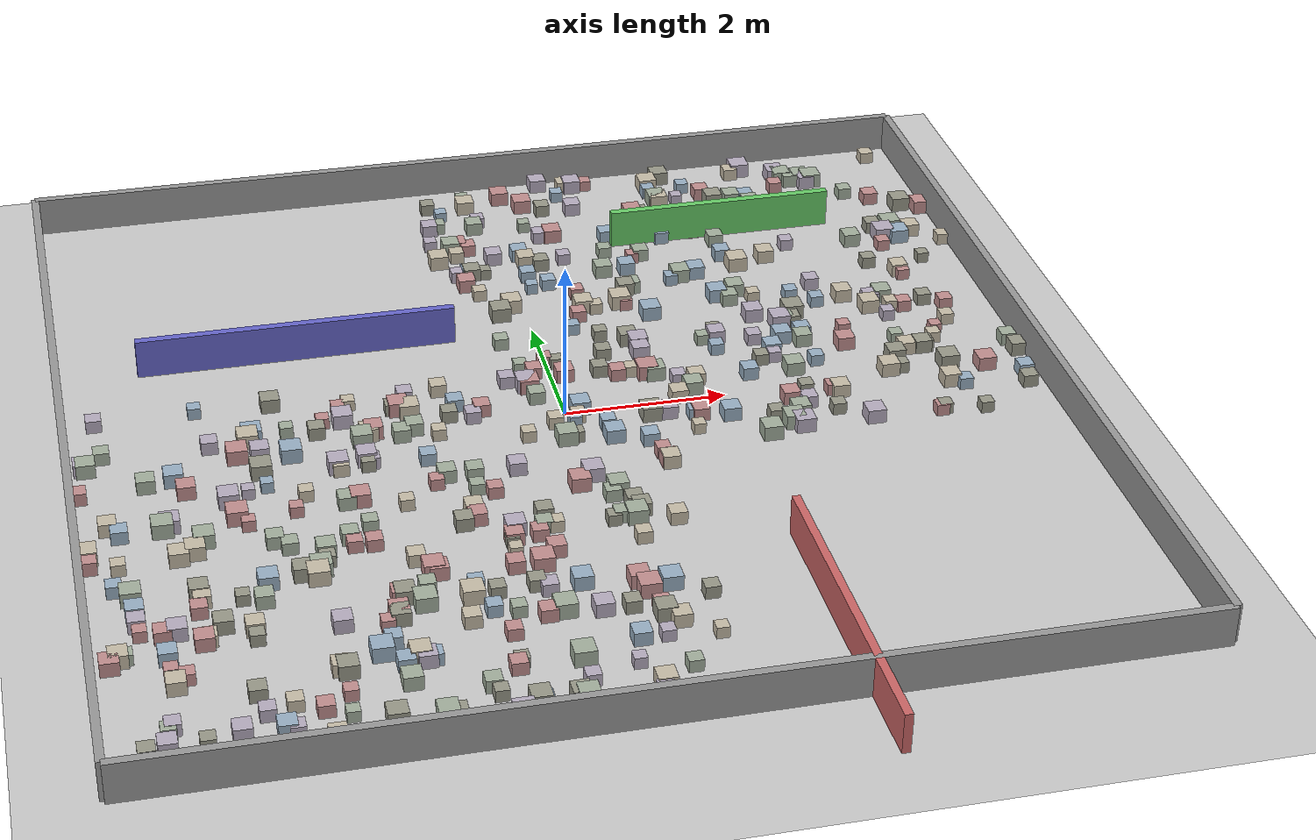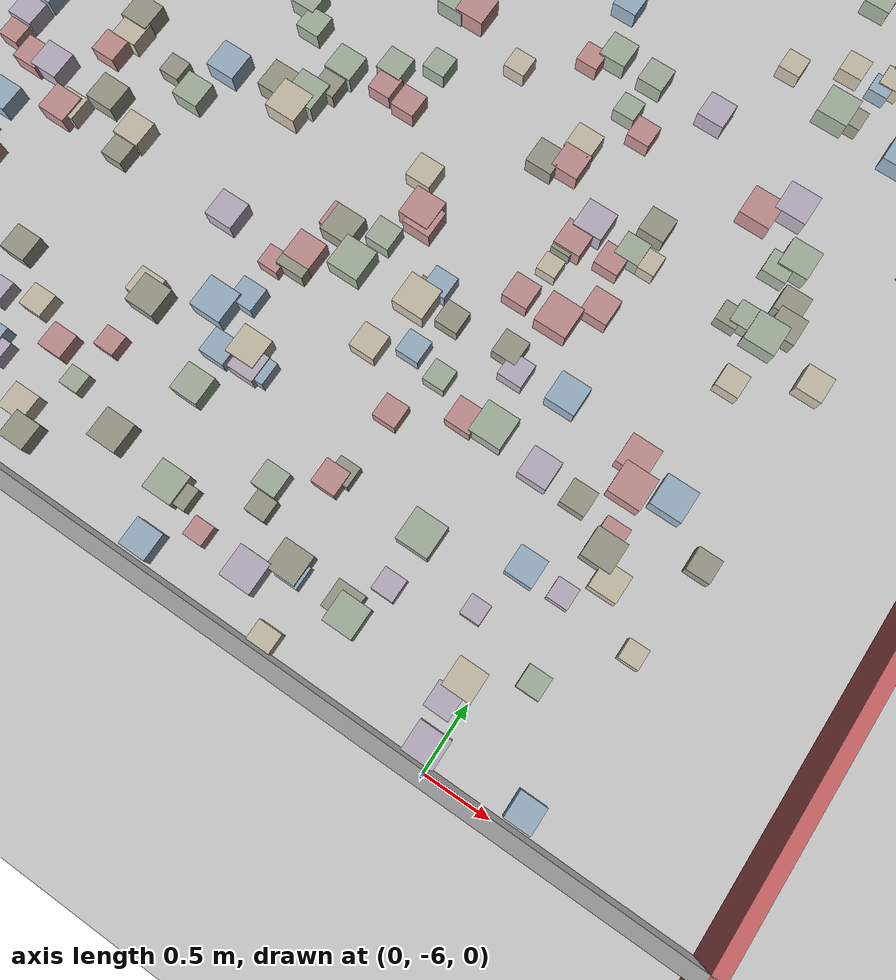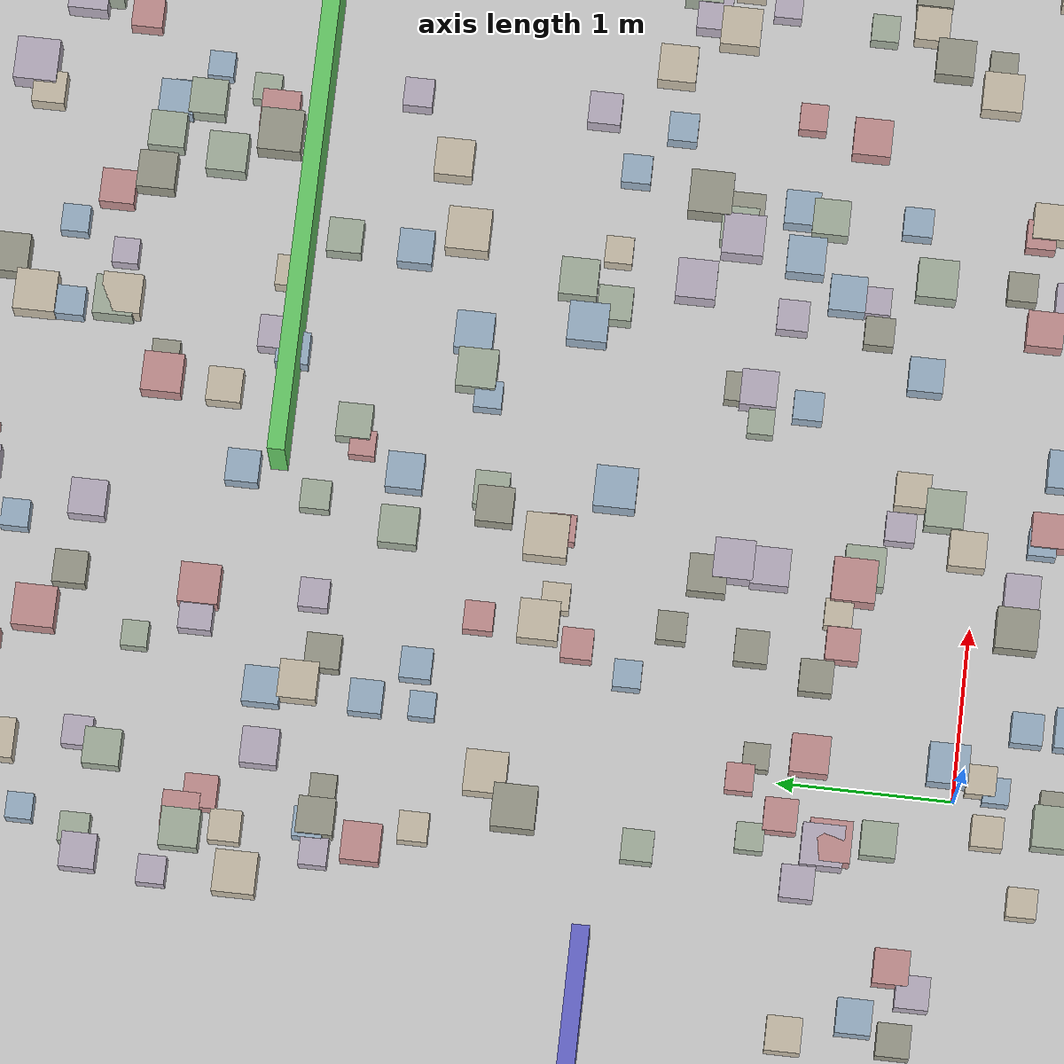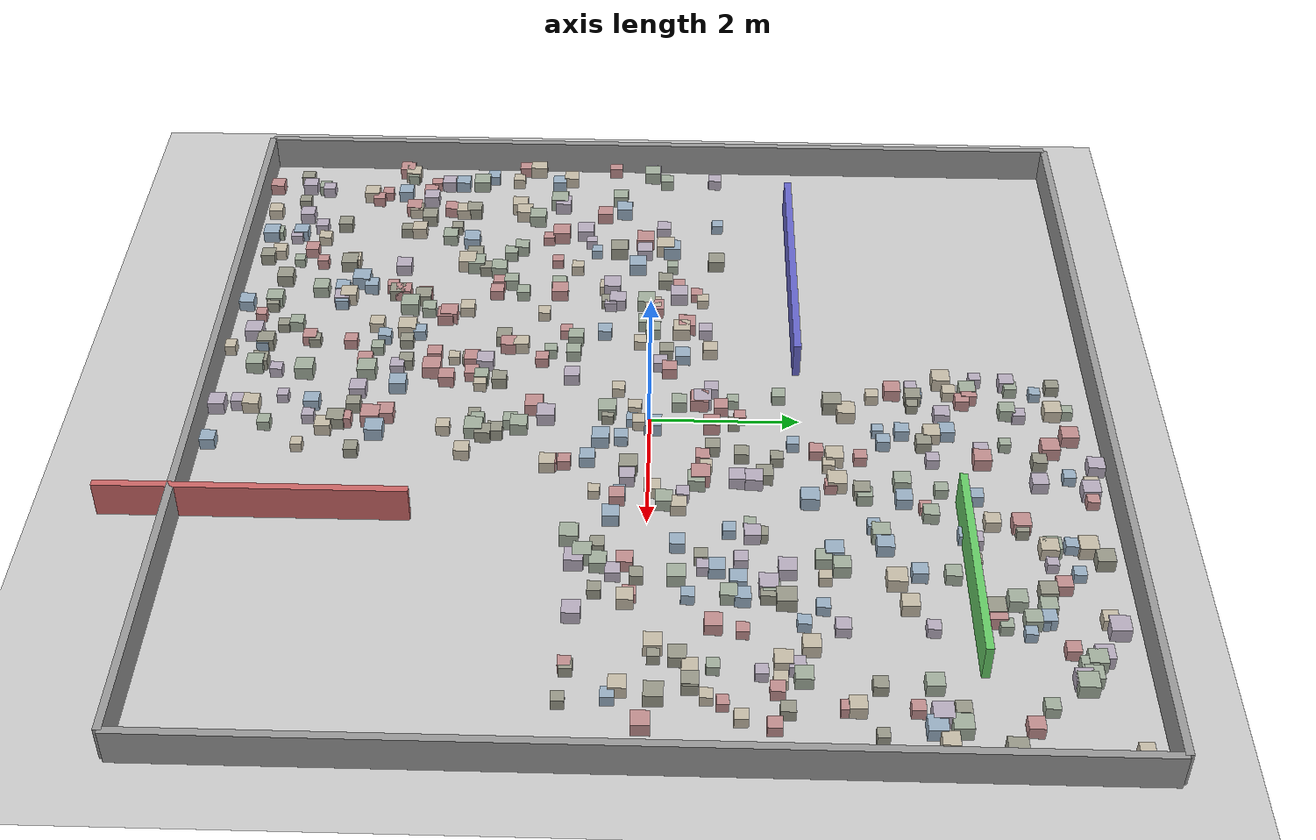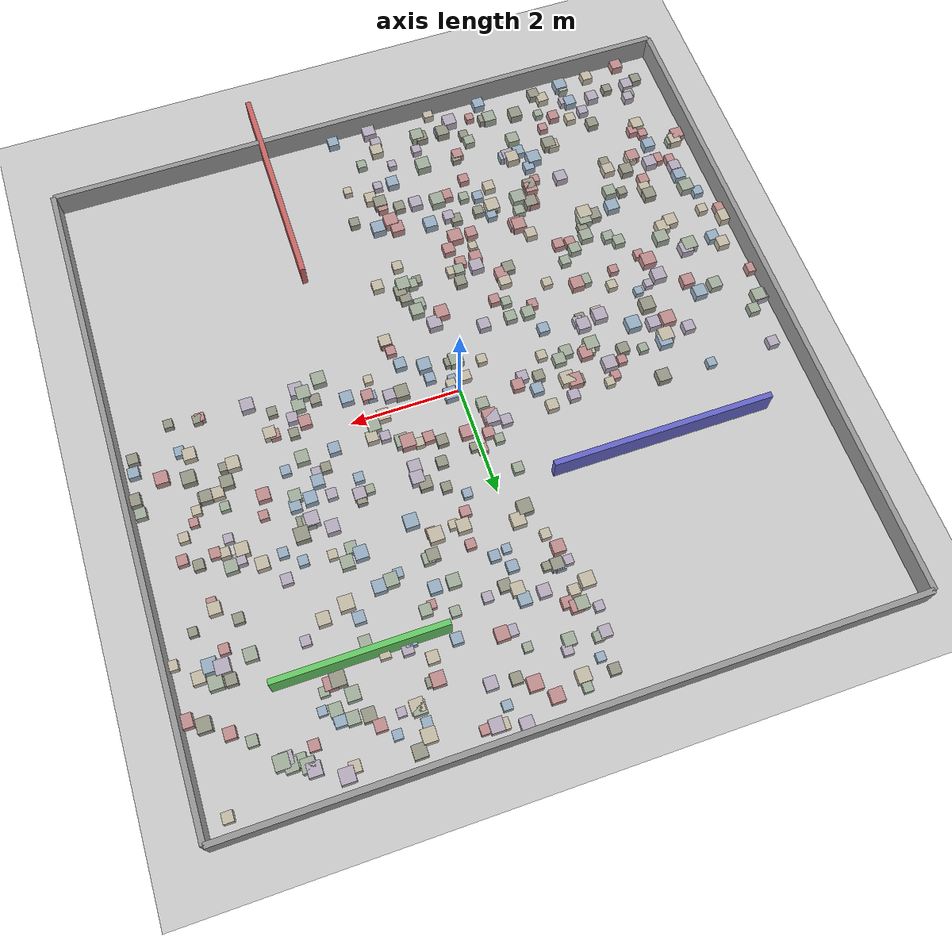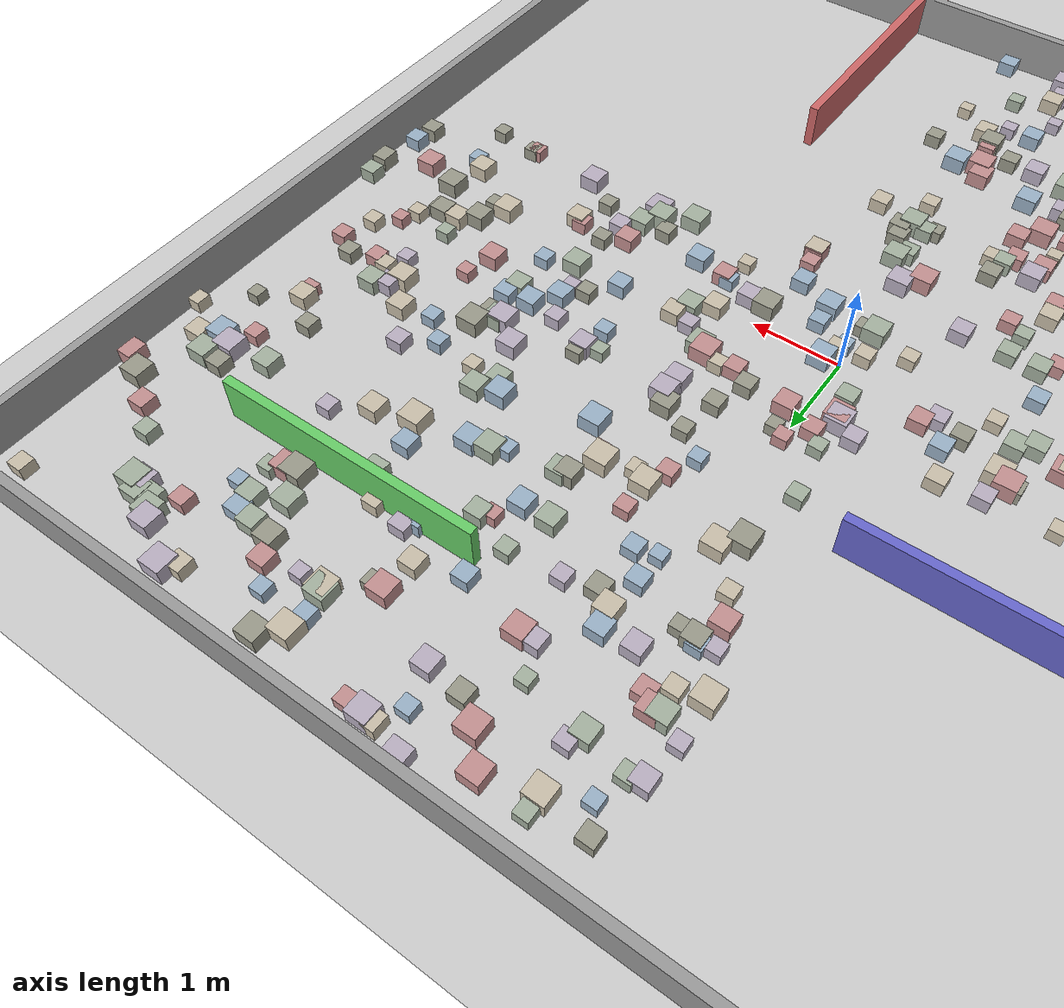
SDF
<?xml version="1.0" ?>
<sdf version="1.6">
  <world name="small_maze_world">
    <gravity>0 0 -9.8</gravity>
    <include><uri>model://ground_plane</uri></include>
    <include><uri>model://sun</uri></include>
    <physics type="ode">
      <real_time_update_rate>1000</real_time_update_rate>
      <max_step_size>0.001</max_step_size>
    </physics>

    <!-- Outer walls -->
    <model name="wall_north">
      <static>true</static><pose>0 6 0.25 0 0 0</pose>
      <link name="link">
        <collision name="collision"><geometry><box><size>12 0.1 0.5</size></box></geometry></collision>
        <visual name="visual"><geometry><box><size>12 0.1 0.5</size></box></geometry><material><ambient>0.6 0.6 0.6 1</ambient></material></visual>
      </link>
    </model>
    <model name="wall_south">
      <static>true</static><pose>0 -6 0.25 0 0 0</pose>
      <link name="link">
        <collision name="collision"><geometry><box><size>12 0.1 0.5</size></box></geometry></collision>
        <visual name="visual"><geometry><box><size>12 0.1 0.5</size></box></geometry><material><ambient>0.6 0.6 0.6 1</ambient></material></visual>
      </link>
    </model>
    <model name="wall_east">
      <static>true</static><pose>6 0 0.25 0 0 0</pose>
      <link name="link">
        <collision name="collision"><geometry><box><size>0.1 12 0.5</size></box></geometry></collision>
        <visual name="visual"><geometry><box><size>0.1 12 0.5</size></box></geometry><material><ambient>0.6 0.6 0.6 1</ambient></material></visual>
      </link>
    </model>
    <model name="wall_west">
      <static>true</static><pose>-6 0 0.25 0 0 0</pose>
      <link name="link">
        <collision name="collision"><geometry><box><size>0.1 12 0.5</size></box></geometry></collision>
        <visual name="visual"><geometry><box><size>0.1 12 0.5</size></box></geometry><material><ambient>0.6 0.6 0.6 1</ambient></material></visual>
      </link>
    </model>

    <!-- Interior walls -->
    <model name="maze_wall_1">
      <static>true</static><pose>-3 2 0.25 0 0 0</pose>
      <link name="link">
        <collision name="collision"><geometry><box><size>4 0.1 0.5</size></box></geometry></collision>
        <visual name="visual"><geometry><box><size>4 0.1 0.5</size></box></geometry><material><ambient>0.4 0.4 0.8 1</ambient></material></visual>
      </link>
    </model>

    <model name="maze_wall_2">
      <static>true</static><pose>2 -5 0.25 0 0 1.5708</pose>
      <link name="link">
        <collision name="collision"><geometry><box><size>4 0.1 0.5</size></box></geometry></collision>
        <visual name="visual"><geometry><box><size>4 0.1 0.5</size></box></geometry><material><ambient>0.8 0.4 0.4 1</ambient></material></visual>
      </link>
    </model>

    <model name="maze_wall_3">
      <static>true</static><pose>3 4 0.25 0 0 0</pose>
      <link name="link">
        <collision name="collision"><geometry><box><size>3 0.1 0.5</size></box></geometry></collision>
        <visual name="visual"><geometry><box><size>3 0.1 0.5</size></box></geometry><material><ambient>0.4 0.8 0.4 1</ambient></material></visual>
      </link>
    </model>

    <!-- Random boxes -->

  <model name="box_1">
    <static>false</static>
    <pose>2.75 -0.89 0.05 0 0 0</pose>
    <link name="link">
      <inertial>
        <mass>0.2</mass>
        <inertia><ixx>0.001</ixx><iyy>0.001</iyy><izz>0.001</izz><ixy>0</ixy><ixz>0</ixz><iyz>0</iyz></inertia>
      </inertial>
      <collision name="collision">
        <geometry><box><size>0.24 0.24 0.24</size></box></geometry>
      </collision>
      <visual name="visual">
        <geometry><box><size>0.24 0.24 0.24</size></box></geometry>
        <material><ambient>0.72 0.68 0.75 1</ambient><diffuse>0.72 0.68 0.75 1</diffuse></material>
      </visual>
    </link>
  </model>

  <model name="box_2">
    <static>false</static>
    <pose>4.61 1.88 0.05 0 0 0</pose>
    <link name="link">
      <inertial>
        <mass>0.2</mass>
        <inertia><ixx>0.001</ixx><iyy>0.001</iyy><izz>0.001</izz><ixy>0</ixy><ixz>0</ixz><iyz>0</iyz></inertia>
      </inertial>
      <collision name="collision">
        <geometry><box><size>0.22 0.22 0.22</size></box></geometry>
      </collision>
      <visual name="visual">
        <geometry><box><size>0.22 0.22 0.22</size></box></geometry>
        <material><ambient>0.64 0.69 0.62 1</ambient><diffuse>0.64 0.69 0.62 1</diffuse></material>
      </visual>
    </link>
  </model>

  <model name="box_3">
    <static>false</static>
    <pose>-2.35 0.05 0.05 0 0 0</pose>
    <link name="link">
      <inertial>
        <mass>0.2</mass>
        <inertia><ixx>0.001</ixx><iyy>0.001</iyy><izz>0.001</izz><ixy>0</ixy><ixz>0</ixz><iyz>0</iyz></inertia>
      </inertial>
      <collision name="collision">
        <geometry><box><size>0.22 0.22 0.22</size></box></geometry>
      </collision>
      <visual name="visual">
        <geometry><box><size>0.22 0.22 0.22</size></box></geometry>
        <material><ambient>0.76 0.56 0.56 1</ambient><diffuse>0.76 0.56 0.56 1</diffuse></material>
      </visual>
    </link>
  </model>

  <model name="box_4">
    <static>false</static>
    <pose>3.29 1.02 0.05 0 0 0</pose>
    <link name="link">
      <inertial>
        <mass>0.2</mass>
        <inertia><ixx>0.001</ixx><iyy>0.001</iyy><izz>0.001</izz><ixy>0</ixy><ixz>0</ixz><iyz>0</iyz></inertia>
      </inertial>
      <collision name="collision">
        <geometry><box><size>0.21 0.21 0.21</size></box></geometry>
      </collision>
      <visual name="visual">
        <geometry><box><size>0.21 0.21 0.21</size></box></geometry>
        <material><ambient>0.64 0.69 0.62 1</ambient><diffuse>0.64 0.69 0.62 1</diffuse></material>
      </visual>
    </link>
  </model>

  <model name="box_5">
    <static>false</static>
    <pose>-0.54 4.31 0.05 0 0 0</pose>
    <link name="link">
      <inertial>
        <mass>0.2</mass>
        <inertia><ixx>0.001</ixx><iyy>0.001</iyy><izz>0.001</izz><ixy>0</ixy><ixz>0</ixz><iyz>0</iyz></inertia>
      </inertial>
      <collision name="collision">
        <geometry><box><size>0.21 0.21 0.21</size></box></geometry>
      </collision>
      <visual name="visual">
        <geometry><box><size>0.21 0.21 0.21</size></box></geometry>
        <material><ambient>0.76 0.56 0.56 1</ambient><diffuse>0.76 0.56 0.56 1</diffuse></material>
      </visual>
    </link>
  </model>

  <model name="box_6">
    <static>false</static>
    <pose>-3.02 0.18 0.05 0 0 0</pose>
    <link name="link">
      <inertial>
        <mass>0.2</mass>
        <inertia><ixx>0.001</ixx><iyy>0.001</iyy><izz>0.001</izz><ixy>0</ixy><ixz>0</ixz><iyz>0</iyz></inertia>
      </inertial>
      <collision name="collision">
        <geometry><box><size>0.2 0.2 0.2</size></box></geometry>
      </collision>
      <visual name="visual">
        <geometry><box><size>0.2 0.2 0.2</size></box></geometry>
        <material><ambient>0.6 0.6 0.54 1</ambient><diffuse>0.6 0.6 0.54 1</diffuse></material>
      </visual>
    </link>
  </model>

  <model name="box_7">
    <static>false</static>
    <pose>-5.69 -3.78 0.05 0 0 0</pose>
    <link name="link">
      <inertial>
        <mass>0.2</mass>
        <inertia><ixx>0.001</ixx><iyy>0.001</iyy><izz>0.001</izz><ixy>0</ixy><ixz>0</ixz><iyz>0</iyz></inertia>
      </inertial>
      <collision name="collision">
        <geometry><box><size>0.22 0.22 0.22</size></box></geometry>
      </collision>
      <visual name="visual">
        <geometry><box><size>0.22 0.22 0.22</size></box></geometry>
        <material><ambient>0.78 0.74 0.66 1</ambient><diffuse>0.78 0.74 0.66 1</diffuse></material>
      </visual>
    </link>
  </model>

  <model name="box_8">
    <static>false</static>
    <pose>4.44 1.81 0.05 0 0 0</pose>
    <link name="link">
      <inertial>
        <mass>0.2</mass>
        <inertia><ixx>0.001</ixx><iyy>0.001</iyy><izz>0.001</izz><ixy>0</ixy><ixz>0</ixz><iyz>0</iyz></inertia>
      </inertial>
      <collision name="collision">
        <geometry><box><size>0.2 0.2 0.2</size></box></geometry>
      </collision>
      <visual name="visual">
        <geometry><box><size>0.2 0.2 0.2</size></box></geometry>
        <material><ambient>0.72 0.68 0.75 1</ambient><diffuse>0.72 0.68 0.75 1</diffuse></material>
      </visual>
    </link>
  </model>

  <model name="box_9">
    <static>false</static>
    <pose>0.94 -1.1 0.05 0 0 0</pose>
    <link name="link">
      <inertial>
        <mass>0.2</mass>
        <inertia><ixx>0.001</ixx><iyy>0.001</iyy><izz>0.001</izz><ixy>0</ixy><ixz>0</ixz><iyz>0</iyz></inertia>
      </inertial>
      <collision name="collision">
        <geometry><box><size>0.17 0.17 0.17</size></box></geometry>
      </collision>
      <visual name="visual">
        <geometry><box><size>0.17 0.17 0.17</size></box></geometry>
        <material><ambient>0.76 0.56 0.56 1</ambient><diffuse>0.76 0.56 0.56 1</diffuse></material>
      </visual>
    </link>
  </model>

  <model name="box_10">
    <static>false</static>
    <pose>5.89 3.17 0.05 0 0 0</pose>
    <link name="link">
      <inertial>
        <mass>0.2</mass>
        <inertia><ixx>0.001</ixx><iyy>0.001</iyy><izz>0.001</izz><ixy>0</ixy><ixz>0</ixz><iyz>0</iyz></inertia>
      </inertial>
      <collision name="collision">
        <geometry><box><size>0.17 0.17 0.17</size></box></geometry>
      </collision>
      <visual name="visual">
        <geometry><box><size>0.17 0.17 0.17</size></box></geometry>
        <material><ambient>0.78 0.74 0.66 1</ambient><diffuse>0.78 0.74 0.66 1</diffuse></material>
      </visual>
    </link>
  </model>

  <model name="box_11">
    <static>false</static>
    <pose>-2.52 -0.5 0.05 0 0 0</pose>
    <link name="link">
      <inertial>
        <mass>0.2</mass>
        <inertia><ixx>0.001</ixx><iyy>0.001</iyy><izz>0.001</izz><ixy>0</ixy><ixz>0</ixz><iyz>0</iyz></inertia>
      </inertial>
      <collision name="collision">
        <geometry><box><size>0.23 0.23 0.23</size></box></geometry>
      </collision>
      <visual name="visual">
        <geometry><box><size>0.23 0.23 0.23</size></box></geometry>
        <material><ambient>0.72 0.68 0.75 1</ambient><diffuse>0.72 0.68 0.75 1</diffuse></material>
      </visual>
    </link>
  </model>

  <model name="box_12">
    <static>false</static>
    <pose>-3.56 -2.64 0.05 0 0 0</pose>
    <link name="link">
      <inertial>
        <mass>0.2</mass>
        <inertia><ixx>0.001</ixx><iyy>0.001</iyy><izz>0.001</izz><ixy>0</ixy><ixz>0</ixz><iyz>0</iyz></inertia>
      </inertial>
      <collision name="collision">
        <geometry><box><size>0.23 0.23 0.23</size></box></geometry>
      </collision>
      <visual name="visual">
        <geometry><box><size>0.23 0.23 0.23</size></box></geometry>
        <material><ambient>0.6 0.6 0.54 1</ambient><diffuse>0.6 0.6 0.54 1</diffuse></material>
      </visual>
    </link>
  </model>

  <model name="box_13">
    <static>false</static>
    <pose>-0.29 -4.98 0.05 0 0 0</pose>
    <link name="link">
      <inertial>
        <mass>0.2</mass>
        <inertia><ixx>0.001</ixx><iyy>0.001</iyy><izz>0.001</izz><ixy>0</ixy><ixz>0</ixz><iyz>0</iyz></inertia>
      </inertial>
      <collision name="collision">
        <geometry><box><size>0.15 0.15 0.15</size></box></geometry>
      </collision>
      <visual name="visual">
        <geometry><box><size>0.15 0.15 0.15</size></box></geometry>
        <material><ambient>0.72 0.68 0.75 1</ambient><diffuse>0.72 0.68 0.75 1</diffuse></material>
      </visual>
    </link>
  </model>

  <model name="box_14">
    <static>false</static>
    <pose>-2.72 -1.34 0.05 0 0 0</pose>
    <link name="link">
      <inertial>
        <mass>0.2</mass>
        <inertia><ixx>0.001</ixx><iyy>0.001</iyy><izz>0.001</izz><ixy>0</ixy><ixz>0</ixz><iyz>0</iyz></inertia>
      </inertial>
      <collision name="collision">
        <geometry><box><size>0.23 0.23 0.23</size></box></geometry>
      </collision>
      <visual name="visual">
        <geometry><box><size>0.23 0.23 0.23</size></box></geometry>
        <material><ambient>0.76 0.56 0.56 1</ambient><diffuse>0.76 0.56 0.56 1</diffuse></material>
      </visual>
    </link>
  </model>

  <model name="box_15">
    <static>false</static>
    <pose>-2.52 -0.65 0.05 0 0 0</pose>
    <link name="link">
      <inertial>
        <mass>0.2</mass>
        <inertia><ixx>0.001</ixx><iyy>0.001</iyy><izz>0.001</izz><ixy>0</ixy><ixz>0</ixz><iyz>0</iyz></inertia>
      </inertial>
      <collision name="collision">
        <geometry><box><size>0.17 0.17 0.17</size></box></geometry>
      </collision>
      <visual name="visual">
        <geometry><box><size>0.17 0.17 0.17</size></box></geometry>
        <material><ambient>0.6 0.6 0.54 1</ambient><diffuse>0.6 0.6 0.54 1</diffuse></material>
      </visual>
    </link>
  </model>

  <model name="box_16">
    <static>false</static>
    <pose>-4.92 -1.4 0.05 0 0 0</pose>
    <link name="link">
      <inertial>
        <mass>0.2</mass>
        <inertia><ixx>0.001</ixx><iyy>0.001</iyy><izz>0.001</izz><ixy>0</ixy><ixz>0</ixz><iyz>0</iyz></inertia>
      </inertial>
      <collision name="collision">
        <geometry><box><size>0.23 0.23 0.23</size></box></geometry>
      </collision>
      <visual name="visual">
        <geometry><box><size>0.23 0.23 0.23</size></box></geometry>
        <material><ambient>0.72 0.68 0.75 1</ambient><diffuse>0.72 0.68 0.75 1</diffuse></material>
      </visual>
    </link>
  </model>

  <model name="box_17">
    <static>false</static>
    <pose>-1.17 -2.54 0.05 0 0 0</pose>
    <link name="link">
      <inertial>
        <mass>0.2</mass>
        <inertia><ixx>0.001</ixx><iyy>0.001</iyy><izz>0.001</izz><ixy>0</ixy><ixz>0</ixz><iyz>0</iyz></inertia>
      </inertial>
      <collision name="collision">
        <geometry><box><size>0.15 0.15 0.15</size></box></geometry>
      </collision>
      <visual name="visual">
        <geometry><box><size>0.15 0.15 0.15</size></box></geometry>
        <material><ambient>0.6 0.6 0.54 1</ambient><diffuse>0.6 0.6 0.54 1</diffuse></material>
      </visual>
    </link>
  </model>

  <model name="box_18">
    <static>false</static>
    <pose>1.25 2.44 0.05 0 0 0</pose>
    <link name="link">
      <inertial>
        <mass>0.2</mass>
        <inertia><ixx>0.001</ixx><iyy>0.001</iyy><izz>0.001</izz><ixy>0</ixy><ixz>0</ixz><iyz>0</iyz></inertia>
      </inertial>
      <collision name="collision">
        <geometry><box><size>0.25 0.25 0.25</size></box></geometry>
      </collision>
      <visual name="visual">
        <geometry><box><size>0.25 0.25 0.25</size></box></geometry>
        <material><ambient>0.78 0.74 0.66 1</ambient><diffuse>0.78 0.74 0.66 1</diffuse></material>
      </visual>
    </link>
  </model>

  <model name="box_19">
    <static>false</static>
    <pose>-2.85 -0.67 0.05 0 0 0</pose>
    <link name="link">
      <inertial>
        <mass>0.2</mass>
        <inertia><ixx>0.001</ixx><iyy>0.001</iyy><izz>0.001</izz><ixy>0</ixy><ixz>0</ixz><iyz>0</iyz></inertia>
      </inertial>
      <collision name="collision">
        <geometry><box><size>0.19 0.19 0.19</size></box></geometry>
      </collision>
      <visual name="visual">
        <geometry><box><size>0.19 0.19 0.19</size></box></geometry>
        <material><ambient>0.78 0.74 0.66 1</ambient><diffuse>0.78 0.74 0.66 1</diffuse></material>
      </visual>
    </link>
  </model>

  <model name="box_20">
    <static>false</static>
    <pose>-4.71 -3.63 0.05 0 0 0</pose>
    <link name="link">
      <inertial>
        <mass>0.2</mass>
        <inertia><ixx>0.001</ixx><iyy>0.001</iyy><izz>0.001</izz><ixy>0</ixy><ixz>0</ixz><iyz>0</iyz></inertia>
      </inertial>
      <collision name="collision">
        <geometry><box><size>0.19 0.19 0.19</size></box></geometry>
      </collision>
      <visual name="visual">
        <geometry><box><size>0.19 0.19 0.19</size></box></geometry>
        <material><ambient>0.78 0.74 0.66 1</ambient><diffuse>0.78 0.74 0.66 1</diffuse></material>
      </visual>
    </link>
  </model>

  <model name="box_21">
    <static>false</static>
    <pose>5.11 1.68 0.05 0 0 0</pose>
    <link name="link">
      <inertial>
        <mass>0.2</mass>
        <inertia><ixx>0.001</ixx><iyy>0.001</iyy><izz>0.001</izz><ixy>0</ixy><ixz>0</ixz><iyz>0</iyz></inertia>
      </inertial>
      <collision name="collision">
        <geometry><box><size>0.18 0.18 0.18</size></box></geometry>
      </collision>
      <visual name="visual">
        <geometry><box><size>0.18 0.18 0.18</size></box></geometry>
        <material><ambient>0.6 0.6 0.54 1</ambient><diffuse>0.6 0.6 0.54 1</diffuse></material>
      </visual>
    </link>
  </model>

  <model name="box_22">
    <static>false</static>
    <pose>3.6 4.84 0.05 0 0 0</pose>
    <link name="link">
      <inertial>
        <mass>0.2</mass>
        <inertia><ixx>0.001</ixx><iyy>0.001</iyy><izz>0.001</izz><ixy>0</ixy><ixz>0</ixz><iyz>0</iyz></inertia>
      </inertial>
      <collision name="collision">
        <geometry><box><size>0.2 0.2 0.2</size></box></geometry>
      </collision>
      <visual name="visual">
        <geometry><box><size>0.2 0.2 0.2</size></box></geometry>
        <material><ambient>0.6 0.69 0.77 1</ambient><diffuse>0.6 0.69 0.77 1</diffuse></material>
      </visual>
    </link>
  </model>

  <model name="box_23">
    <static>false</static>
    <pose>-5.53 -5.41 0.05 0 0 0</pose>
    <link name="link">
      <inertial>
        <mass>0.2</mass>
        <inertia><ixx>0.001</ixx><iyy>0.001</iyy><izz>0.001</izz><ixy>0</ixy><ixz>0</ixz><iyz>0</iyz></inertia>
      </inertial>
      <collision name="collision">
        <geometry><box><size>0.19 0.19 0.19</size></box></geometry>
      </collision>
      <visual name="visual">
        <geometry><box><size>0.19 0.19 0.19</size></box></geometry>
        <material><ambient>0.6 0.6 0.54 1</ambient><diffuse>0.6 0.6 0.54 1</diffuse></material>
      </visual>
    </link>
  </model>

  <model name="box_24">
    <static>false</static>
    <pose>2.65 2.2 0.05 0 0 0</pose>
    <link name="link">
      <inertial>
        <mass>0.2</mass>
        <inertia><ixx>0.001</ixx><iyy>0.001</iyy><izz>0.001</izz><ixy>0</ixy><ixz>0</ixz><iyz>0</iyz></inertia>
      </inertial>
      <collision name="collision">
        <geometry><box><size>0.2 0.2 0.2</size></box></geometry>
      </collision>
      <visual name="visual">
        <geometry><box><size>0.2 0.2 0.2</size></box></geometry>
        <material><ambient>0.64 0.69 0.62 1</ambient><diffuse>0.64 0.69 0.62 1</diffuse></material>
      </visual>
    </link>
  </model>

  <model name="box_25">
    <static>false</static>
    <pose>2.66 5.02 0.05 0 0 0</pose>
    <link name="link">
      <inertial>
        <mass>0.2</mass>
        <inertia><ixx>0.001</ixx><iyy>0.001</iyy><izz>0.001</izz><ixy>0</ixy><ixz>0</ixz><iyz>0</iyz></inertia>
      </inertial>
      <collision name="collision">
        <geometry><box><size>0.15 0.15 0.15</size></box></geometry>
      </collision>
      <visual name="visual">
        <geometry><box><size>0.15 0.15 0.15</size></box></geometry>
        <material><ambient>0.72 0.68 0.75 1</ambient><diffuse>0.72 0.68 0.75 1</diffuse></material>
      </visual>
    </link>
  </model>

  <model name="box_26">
    <static>false</static>
    <pose>0.33 -4.35 0.05 0 0 0</pose>
    <link name="link">
      <inertial>
        <mass>0.2</mass>
        <inertia><ixx>0.001</ixx><iyy>0.001</iyy><izz>0.001</izz><ixy>0</ixy><ixz>0</ixz><iyz>0</iyz></inertia>
      </inertial>
      <collision name="collision">
        <geometry><box><size>0.21 0.21 0.21</size></box></geometry>
      </collision>
      <visual name="visual">
        <geometry><box><size>0.21 0.21 0.21</size></box></geometry>
        <material><ambient>0.78 0.74 0.66 1</ambient><diffuse>0.78 0.74 0.66 1</diffuse></material>
      </visual>
    </link>
  </model>

  <model name="box_27">
    <static>false</static>
    <pose>1.65 0.21 0.05 0 0 0</pose>
    <link name="link">
      <inertial>
        <mass>0.2</mass>
        <inertia><ixx>0.001</ixx><iyy>0.001</iyy><izz>0.001</izz><ixy>0</ixy><ixz>0</ixz><iyz>0</iyz></inertia>
      </inertial>
      <collision name="collision">
        <geometry><box><size>0.22 0.22 0.22</size></box></geometry>
      </collision>
      <visual name="visual">
        <geometry><box><size>0.22 0.22 0.22</size></box></geometry>
        <material><ambient>0.64 0.69 0.62 1</ambient><diffuse>0.64 0.69 0.62 1</diffuse></material>
      </visual>
    </link>
  </model>

  <model name="box_28">
    <static>false</static>
    <pose>2.64 4.06 0.05 0 0 0</pose>
    <link name="link">
      <inertial>
        <mass>0.2</mass>
        <inertia><ixx>0.001</ixx><iyy>0.001</iyy><izz>0.001</izz><ixy>0</ixy><ixz>0</ixz><iyz>0</iyz></inertia>
      </inertial>
      <collision name="collision">
        <geometry><box><size>0.18 0.18 0.18</size></box></geometry>
      </collision>
      <visual name="visual">
        <geometry><box><size>0.18 0.18 0.18</size></box></geometry>
        <material><ambient>0.78 0.74 0.66 1</ambient><diffuse>0.78 0.74 0.66 1</diffuse></material>
      </visual>
    </link>
  </model>

  <model name="box_29">
    <static>false</static>
    <pose>3.26 -0.62 0.05 0 0 0</pose>
    <link name="link">
      <inertial>
        <mass>0.2</mass>
        <inertia><ixx>0.001</ixx><iyy>0.001</iyy><izz>0.001</izz><ixy>0</ixy><ixz>0</ixz><iyz>0</iyz></inertia>
      </inertial>
      <collision name="collision">
        <geometry><box><size>0.17 0.17 0.17</size></box></geometry>
      </collision>
      <visual name="visual">
        <geometry><box><size>0.17 0.17 0.17</size></box></geometry>
        <material><ambient>0.6 0.6 0.54 1</ambient><diffuse>0.6 0.6 0.54 1</diffuse></material>
      </visual>
    </link>
  </model>

  <model name="box_30">
    <static>false</static>
    <pose>2.27 4.11 0.05 0 0 0</pose>
    <link name="link">
      <inertial>
        <mass>0.2</mass>
        <inertia><ixx>0.001</ixx><iyy>0.001</iyy><izz>0.001</izz><ixy>0</ixy><ixz>0</ixz><iyz>0</iyz></inertia>
      </inertial>
      <collision name="collision">
        <geometry><box><size>0.19 0.19 0.19</size></box></geometry>
      </collision>
      <visual name="visual">
        <geometry><box><size>0.19 0.19 0.19</size></box></geometry>
        <material><ambient>0.72 0.68 0.75 1</ambient><diffuse>0.72 0.68 0.75 1</diffuse></material>
      </visual>
    </link>
  </model>

  <model name="box_31">
    <static>false</static>
    <pose>0.78 5.1 0.05 0 0 0</pose>
    <link name="link">
      <inertial>
        <mass>0.2</mass>
        <inertia><ixx>0.001</ixx><iyy>0.001</iyy><izz>0.001</izz><ixy>0</ixy><ixz>0</ixz><iyz>0</iyz></inertia>
      </inertial>
      <collision name="collision">
        <geometry><box><size>0.19 0.19 0.19</size></box></geometry>
      </collision>
      <visual name="visual">
        <geometry><box><size>0.19 0.19 0.19</size></box></geometry>
        <material><ambient>0.6 0.6 0.54 1</ambient><diffuse>0.6 0.6 0.54 1</diffuse></material>
      </visual>
    </link>
  </model>

  <model name="box_32">
    <static>false</static>
    <pose>-1.09 -2.29 0.05 0 0 0</pose>
    <link name="link">
      <inertial>
        <mass>0.2</mass>
        <inertia><ixx>0.001</ixx><iyy>0.001</iyy><izz>0.001</izz><ixy>0</ixy><ixz>0</ixz><iyz>0</iyz></inertia>
      </inertial>
      <collision name="collision">
        <geometry><box><size>0.23 0.23 0.23</size></box></geometry>
      </collision>
      <visual name="visual">
        <geometry><box><size>0.23 0.23 0.23</size></box></geometry>
        <material><ambient>0.72 0.68 0.75 1</ambient><diffuse>0.72 0.68 0.75 1</diffuse></material>
      </visual>
    </link>
  </model>

  <model name="box_33">
    <static>false</static>
    <pose>-4.2 -3.53 0.05 0 0 0</pose>
    <link name="link">
      <inertial>
        <mass>0.2</mass>
        <inertia><ixx>0.001</ixx><iyy>0.001</iyy><izz>0.001</izz><ixy>0</ixy><ixz>0</ixz><iyz>0</iyz></inertia>
      </inertial>
      <collision name="collision">
        <geometry><box><size>0.21 0.21 0.21</size></box></geometry>
      </collision>
      <visual name="visual">
        <geometry><box><size>0.21 0.21 0.21</size></box></geometry>
        <material><ambient>0.78 0.74 0.66 1</ambient><diffuse>0.78 0.74 0.66 1</diffuse></material>
      </visual>
    </link>
  </model>

  <model name="box_34">
    <static>false</static>
    <pose>3.03 5.11 0.05 0 0 0</pose>
    <link name="link">
      <inertial>
        <mass>0.2</mass>
        <inertia><ixx>0.001</ixx><iyy>0.001</iyy><izz>0.001</izz><ixy>0</ixy><ixz>0</ixz><iyz>0</iyz></inertia>
      </inertial>
      <collision name="collision">
        <geometry><box><size>0.2 0.2 0.2</size></box></geometry>
      </collision>
      <visual name="visual">
        <geometry><box><size>0.2 0.2 0.2</size></box></geometry>
        <material><ambient>0.76 0.56 0.56 1</ambient><diffuse>0.76 0.56 0.56 1</diffuse></material>
      </visual>
    </link>
  </model>

  <model name="box_35">
    <static>false</static>
    <pose>-1.47 -2.0 0.05 0 0 0</pose>
    <link name="link">
      <inertial>
        <mass>0.2</mass>
        <inertia><ixx>0.001</ixx><iyy>0.001</iyy><izz>0.001</izz><ixy>0</ixy><ixz>0</ixz><iyz>0</iyz></inertia>
      </inertial>
      <collision name="collision">
        <geometry><box><size>0.21 0.21 0.21</size></box></geometry>
      </collision>
      <visual name="visual">
        <geometry><box><size>0.21 0.21 0.21</size></box></geometry>
        <material><ambient>0.76 0.56 0.56 1</ambient><diffuse>0.76 0.56 0.56 1</diffuse></material>
      </visual>
    </link>
  </model>

  <model name="box_36">
    <static>false</static>
    <pose>-0.86 -3.91 0.05 0 0 0</pose>
    <link name="link">
      <inertial>
        <mass>0.2</mass>
        <inertia><ixx>0.001</ixx><iyy>0.001</iyy><izz>0.001</izz><ixy>0</ixy><ixz>0</ixz><iyz>0</iyz></inertia>
      </inertial>
      <collision name="collision">
        <geometry><box><size>0.25 0.25 0.25</size></box></geometry>
      </collision>
      <visual name="visual">
        <geometry><box><size>0.25 0.25 0.25</size></box></geometry>
        <material><ambient>0.64 0.69 0.62 1</ambient><diffuse>0.64 0.69 0.62 1</diffuse></material>
      </visual>
    </link>
  </model>

  <model name="box_37">
    <static>false</static>
    <pose>-0.92 -3.02 0.05 0 0 0</pose>
    <link name="link">
      <inertial>
        <mass>0.2</mass>
        <inertia><ixx>0.001</ixx><iyy>0.001</iyy><izz>0.001</izz><ixy>0</ixy><ixz>0</ixz><iyz>0</iyz></inertia>
      </inertial>
      <collision name="collision">
        <geometry><box><size>0.25 0.25 0.25</size></box></geometry>
      </collision>
      <visual name="visual">
        <geometry><box><size>0.25 0.25 0.25</size></box></geometry>
        <material><ambient>0.76 0.56 0.56 1</ambient><diffuse>0.76 0.56 0.56 1</diffuse></material>
      </visual>
    </link>
  </model>

  <model name="box_38">
    <static>false</static>
    <pose>-4.62 -5.77 0.05 0 0 0</pose>
    <link name="link">
      <inertial>
        <mass>0.2</mass>
        <inertia><ixx>0.001</ixx><iyy>0.001</iyy><izz>0.001</izz><ixy>0</ixy><ixz>0</ixz><iyz>0</iyz></inertia>
      </inertial>
      <collision name="collision">
        <geometry><box><size>0.2 0.2 0.2</size></box></geometry>
      </collision>
      <visual name="visual">
        <geometry><box><size>0.2 0.2 0.2</size></box></geometry>
        <material><ambient>0.78 0.74 0.66 1</ambient><diffuse>0.78 0.74 0.66 1</diffuse></material>
      </visual>
    </link>
  </model>

  <model name="box_39">
    <static>false</static>
    <pose>-0.14 -5.56 0.05 0 0 0</pose>
    <link name="link">
      <inertial>
        <mass>0.2</mass>
        <inertia><ixx>0.001</ixx><iyy>0.001</iyy><izz>0.001</izz><ixy>0</ixy><ixz>0</ixz><iyz>0</iyz></inertia>
      </inertial>
      <collision name="collision">
        <geometry><box><size>0.19 0.19 0.19</size></box></geometry>
      </collision>
      <visual name="visual">
        <geometry><box><size>0.19 0.19 0.19</size></box></geometry>
        <material><ambient>0.72 0.68 0.75 1</ambient><diffuse>0.72 0.68 0.75 1</diffuse></material>
      </visual>
    </link>
  </model>

  <model name="box_40">
    <static>false</static>
    <pose>1.8 3.6 0.05 0 0 0</pose>
    <link name="link">
      <inertial>
        <mass>0.2</mass>
        <inertia><ixx>0.001</ixx><iyy>0.001</iyy><izz>0.001</izz><ixy>0</ixy><ixz>0</ixz><iyz>0</iyz></inertia>
      </inertial>
      <collision name="collision">
        <geometry><box><size>0.2 0.2 0.2</size></box></geometry>
      </collision>
      <visual name="visual">
        <geometry><box><size>0.2 0.2 0.2</size></box></geometry>
        <material><ambient>0.64 0.69 0.62 1</ambient><diffuse>0.64 0.69 0.62 1</diffuse></material>
      </visual>
    </link>
  </model>

  <model name="box_41">
    <static>false</static>
    <pose>-3.65 -5.07 0.05 0 0 0</pose>
    <link name="link">
      <inertial>
        <mass>0.2</mass>
        <inertia><ixx>0.001</ixx><iyy>0.001</iyy><izz>0.001</izz><ixy>0</ixy><ixz>0</ixz><iyz>0</iyz></inertia>
      </inertial>
      <collision name="collision">
        <geometry><box><size>0.19 0.19 0.19</size></box></geometry>
      </collision>
      <visual name="visual">
        <geometry><box><size>0.19 0.19 0.19</size></box></geometry>
        <material><ambient>0.76 0.56 0.56 1</ambient><diffuse>0.76 0.56 0.56 1</diffuse></material>
      </visual>
    </link>
  </model>

  <model name="box_42">
    <static>false</static>
    <pose>-0.14 2.63 0.05 0 0 0</pose>
    <link name="link">
      <inertial>
        <mass>0.2</mass>
        <inertia><ixx>0.001</ixx><iyy>0.001</iyy><izz>0.001</izz><ixy>0</ixy><ixz>0</ixz><iyz>0</iyz></inertia>
      </inertial>
      <collision name="collision">
        <geometry><box><size>0.24 0.24 0.24</size></box></geometry>
      </collision>
      <visual name="visual">
        <geometry><box><size>0.24 0.24 0.24</size></box></geometry>
        <material><ambient>0.78 0.74 0.66 1</ambient><diffuse>0.78 0.74 0.66 1</diffuse></material>
      </visual>
    </link>
  </model>

  <model name="box_43">
    <static>false</static>
    <pose>0.27 5.56 0.05 0 0 0</pose>
    <link name="link">
      <inertial>
        <mass>0.2</mass>
        <inertia><ixx>0.001</ixx><iyy>0.001</iyy><izz>0.001</izz><ixy>0</ixy><ixz>0</ixz><iyz>0</iyz></inertia>
      </inertial>
      <collision name="collision">
        <geometry><box><size>0.23 0.23 0.23</size></box></geometry>
      </collision>
      <visual name="visual">
        <geometry><box><size>0.23 0.23 0.23</size></box></geometry>
        <material><ambient>0.76 0.56 0.56 1</ambient><diffuse>0.76 0.56 0.56 1</diffuse></material>
      </visual>
    </link>
  </model>

  <model name="box_44">
    <static>false</static>
    <pose>0.81 0.71 0.05 0 0 0</pose>
    <link name="link">
      <inertial>
        <mass>0.2</mass>
        <inertia><ixx>0.001</ixx><iyy>0.001</iyy><izz>0.001</izz><ixy>0</ixy><ixz>0</ixz><iyz>0</iyz></inertia>
      </inertial>
      <collision name="collision">
        <geometry><box><size>0.19 0.19 0.19</size></box></geometry>
      </collision>
      <visual name="visual">
        <geometry><box><size>0.19 0.19 0.19</size></box></geometry>
        <material><ambient>0.76 0.56 0.56 1</ambient><diffuse>0.76 0.56 0.56 1</diffuse></material>
      </visual>
    </link>
  </model>

  <model name="box_45">
    <static>false</static>
    <pose>-1.45 -5.4 0.05 0 0 0</pose>
    <link name="link">
      <inertial>
        <mass>0.2</mass>
        <inertia><ixx>0.001</ixx><iyy>0.001</iyy><izz>0.001</izz><ixy>0</ixy><ixz>0</ixz><iyz>0</iyz></inertia>
      </inertial>
      <collision name="collision">
        <geometry><box><size>0.23 0.23 0.23</size></box></geometry>
      </collision>
      <visual name="visual">
        <geometry><box><size>0.23 0.23 0.23</size></box></geometry>
        <material><ambient>0.6 0.6 0.54 1</ambient><diffuse>0.6 0.6 0.54 1</diffuse></material>
      </visual>
    </link>
  </model>

  <model name="box_46">
    <static>false</static>
    <pose>5.24 1.14 0.05 0 0 0</pose>
    <link name="link">
      <inertial>
        <mass>0.2</mass>
        <inertia><ixx>0.001</ixx><iyy>0.001</iyy><izz>0.001</izz><ixy>0</ixy><ixz>0</ixz><iyz>0</iyz></inertia>
      </inertial>
      <collision name="collision">
        <geometry><box><size>0.17 0.17 0.17</size></box></geometry>
      </collision>
      <visual name="visual">
        <geometry><box><size>0.17 0.17 0.17</size></box></geometry>
        <material><ambient>0.78 0.74 0.66 1</ambient><diffuse>0.78 0.74 0.66 1</diffuse></material>
      </visual>
    </link>
  </model>

  <model name="box_47">
    <static>false</static>
    <pose>-3.4 -4.42 0.05 0 0 0</pose>
    <link name="link">
      <inertial>
        <mass>0.2</mass>
        <inertia><ixx>0.001</ixx><iyy>0.001</iyy><izz>0.001</izz><ixy>0</ixy><ixz>0</ixz><iyz>0</iyz></inertia>
      </inertial>
      <collision name="collision">
        <geometry><box><size>0.2 0.2 0.2</size></box></geometry>
      </collision>
      <visual name="visual">
        <geometry><box><size>0.2 0.2 0.2</size></box></geometry>
        <material><ambient>0.78 0.74 0.66 1</ambient><diffuse>0.78 0.74 0.66 1</diffuse></material>
      </visual>
    </link>
  </model>

  <model name="box_48">
    <static>false</static>
    <pose>-2.41 0.01 0.05 0 0 0</pose>
    <link name="link">
      <inertial>
        <mass>0.2</mass>
        <inertia><ixx>0.001</ixx><iyy>0.001</iyy><izz>0.001</izz><ixy>0</ixy><ixz>0</ixz><iyz>0</iyz></inertia>
      </inertial>
      <collision name="collision">
        <geometry><box><size>0.22 0.22 0.22</size></box></geometry>
      </collision>
      <visual name="visual">
        <geometry><box><size>0.22 0.22 0.22</size></box></geometry>
        <material><ambient>0.78 0.74 0.66 1</ambient><diffuse>0.78 0.74 0.66 1</diffuse></material>
      </visual>
    </link>
  </model>

  <model name="box_49">
    <static>false</static>
    <pose>3.8 2.38 0.05 0 0 0</pose>
    <link name="link">
      <inertial>
        <mass>0.2</mass>
        <inertia><ixx>0.001</ixx><iyy>0.001</iyy><izz>0.001</izz><ixy>0</ixy><ixz>0</ixz><iyz>0</iyz></inertia>
      </inertial>
      <collision name="collision">
        <geometry><box><size>0.19 0.19 0.19</size></box></geometry>
      </collision>
      <visual name="visual">
        <geometry><box><size>0.19 0.19 0.19</size></box></geometry>
        <material><ambient>0.72 0.68 0.75 1</ambient><diffuse>0.72 0.68 0.75 1</diffuse></material>
      </visual>
    </link>
  </model>

  <model name="box_50">
    <static>false</static>
    <pose>-1.17 -2.73 0.05 0 0 0</pose>
    <link name="link">
      <inertial>
        <mass>0.2</mass>
        <inertia><ixx>0.001</ixx><iyy>0.001</iyy><izz>0.001</izz><ixy>0</ixy><ixz>0</ixz><iyz>0</iyz></inertia>
      </inertial>
      <collision name="collision">
        <geometry><box><size>0.15 0.15 0.15</size></box></geometry>
      </collision>
      <visual name="visual">
        <geometry><box><size>0.15 0.15 0.15</size></box></geometry>
        <material><ambient>0.78 0.74 0.66 1</ambient><diffuse>0.78 0.74 0.66 1</diffuse></material>
      </visual>
    </link>
  </model>

  <model name="box_51">
    <static>false</static>
    <pose>5.35 1.52 0.05 0 0 0</pose>
    <link name="link">
      <inertial>
        <mass>0.2</mass>
        <inertia><ixx>0.001</ixx><iyy>0.001</iyy><izz>0.001</izz><ixy>0</ixy><ixz>0</ixz><iyz>0</iyz></inertia>
      </inertial>
      <collision name="collision">
        <geometry><box><size>0.18 0.18 0.18</size></box></geometry>
      </collision>
      <visual name="visual">
        <geometry><box><size>0.18 0.18 0.18</size></box></geometry>
        <material><ambient>0.76 0.56 0.56 1</ambient><diffuse>0.76 0.56 0.56 1</diffuse></material>
      </visual>
    </link>
  </model>

  <model name="box_52">
    <static>false</static>
    <pose>0.53 5.27 0.05 0 0 0</pose>
    <link name="link">
      <inertial>
        <mass>0.2</mass>
        <inertia><ixx>0.001</ixx><iyy>0.001</iyy><izz>0.001</izz><ixy>0</ixy><ixz>0</ixz><iyz>0</iyz></inertia>
      </inertial>
      <collision name="collision">
        <geometry><box><size>0.24 0.24 0.24</size></box></geometry>
      </collision>
      <visual name="visual">
        <geometry><box><size>0.24 0.24 0.24</size></box></geometry>
        <material><ambient>0.76 0.56 0.56 1</ambient><diffuse>0.76 0.56 0.56 1</diffuse></material>
      </visual>
    </link>
  </model>

  <model name="box_53">
    <static>false</static>
    <pose>-1.88 -5.03 0.05 0 0 0</pose>
    <link name="link">
      <inertial>
        <mass>0.2</mass>
        <inertia><ixx>0.001</ixx><iyy>0.001</iyy><izz>0.001</izz><ixy>0</ixy><ixz>0</ixz><iyz>0</iyz></inertia>
      </inertial>
      <collision name="collision">
        <geometry><box><size>0.19 0.19 0.19</size></box></geometry>
      </collision>
      <visual name="visual">
        <geometry><box><size>0.19 0.19 0.19</size></box></geometry>
        <material><ambient>0.64 0.69 0.62 1</ambient><diffuse>0.64 0.69 0.62 1</diffuse></material>
      </visual>
    </link>
  </model>

  <model name="box_54">
    <static>false</static>
    <pose>5.89 4.09 0.05 0 0 0</pose>
    <link name="link">
      <inertial>
        <mass>0.2</mass>
        <inertia><ixx>0.001</ixx><iyy>0.001</iyy><izz>0.001</izz><ixy>0</ixy><ixz>0</ixz><iyz>0</iyz></inertia>
      </inertial>
      <collision name="collision">
        <geometry><box><size>0.23 0.23 0.23</size></box></geometry>
      </collision>
      <visual name="visual">
        <geometry><box><size>0.23 0.23 0.23</size></box></geometry>
        <material><ambient>0.76 0.56 0.56 1</ambient><diffuse>0.76 0.56 0.56 1</diffuse></material>
      </visual>
    </link>
  </model>

  <model name="box_55">
    <static>false</static>
    <pose>-2.53 -3.3 0.05 0 0 0</pose>
    <link name="link">
      <inertial>
        <mass>0.2</mass>
        <inertia><ixx>0.001</ixx><iyy>0.001</iyy><izz>0.001</izz><ixy>0</ixy><ixz>0</ixz><iyz>0</iyz></inertia>
      </inertial>
      <collision name="collision">
        <geometry><box><size>0.23 0.23 0.23</size></box></geometry>
      </collision>
      <visual name="visual">
        <geometry><box><size>0.23 0.23 0.23</size></box></geometry>
        <material><ambient>0.6 0.6 0.54 1</ambient><diffuse>0.6 0.6 0.54 1</diffuse></material>
      </visual>
    </link>
  </model>

  <model name="box_56">
    <static>false</static>
    <pose>-0.24 5.4 0.05 0 0 0</pose>
    <link name="link">
      <inertial>
        <mass>0.2</mass>
        <inertia><ixx>0.001</ixx><iyy>0.001</iyy><izz>0.001</izz><ixy>0</ixy><ixz>0</ixz><iyz>0</iyz></inertia>
      </inertial>
      <collision name="collision">
        <geometry><box><size>0.23 0.23 0.23</size></box></geometry>
      </collision>
      <visual name="visual">
        <geometry><box><size>0.23 0.23 0.23</size></box></geometry>
        <material><ambient>0.78 0.74 0.66 1</ambient><diffuse>0.78 0.74 0.66 1</diffuse></material>
      </visual>
    </link>
  </model>

  <model name="box_57">
    <static>false</static>
    <pose>-3.35 -2.6 0.05 0 0 0</pose>
    <link name="link">
      <inertial>
        <mass>0.2</mass>
        <inertia><ixx>0.001</ixx><iyy>0.001</iyy><izz>0.001</izz><ixy>0</ixy><ixz>0</ixz><iyz>0</iyz></inertia>
      </inertial>
      <collision name="collision">
        <geometry><box><size>0.24 0.24 0.24</size></box></geometry>
      </collision>
      <visual name="visual">
        <geometry><box><size>0.24 0.24 0.24</size></box></geometry>
        <material><ambient>0.64 0.69 0.62 1</ambient><diffuse>0.64 0.69 0.62 1</diffuse></material>
      </visual>
    </link>
  </model>

  <model name="box_58">
    <static>false</static>
    <pose>-0.17 -1.56 0.05 0 0 0</pose>
    <link name="link">
      <inertial>
        <mass>0.2</mass>
        <inertia><ixx>0.001</ixx><iyy>0.001</iyy><izz>0.001</izz><ixy>0</ixy><ixz>0</ixz><iyz>0</iyz></inertia>
      </inertial>
      <collision name="collision">
        <geometry><box><size>0.24 0.24 0.24</size></box></geometry>
      </collision>
      <visual name="visual">
        <geometry><box><size>0.24 0.24 0.24</size></box></geometry>
        <material><ambient>0.76 0.56 0.56 1</ambient><diffuse>0.76 0.56 0.56 1</diffuse></material>
      </visual>
    </link>
  </model>

  <model name="box_59">
    <static>false</static>
    <pose>4.53 -0.9 0.05 0 0 0</pose>
    <link name="link">
      <inertial>
        <mass>0.2</mass>
        <inertia><ixx>0.001</ixx><iyy>0.001</iyy><izz>0.001</izz><ixy>0</ixy><ixz>0</ixz><iyz>0</iyz></inertia>
      </inertial>
      <collision name="collision">
        <geometry><box><size>0.16 0.16 0.16</size></box></geometry>
      </collision>
      <visual name="visual">
        <geometry><box><size>0.16 0.16 0.16</size></box></geometry>
        <material><ambient>0.6 0.6 0.54 1</ambient><diffuse>0.6 0.6 0.54 1</diffuse></material>
      </visual>
    </link>
  </model>

  <model name="box_60">
    <static>false</static>
    <pose>5.54 3.49 0.05 0 0 0</pose>
    <link name="link">
      <inertial>
        <mass>0.2</mass>
        <inertia><ixx>0.001</ixx><iyy>0.001</iyy><izz>0.001</izz><ixy>0</ixy><ixz>0</ixz><iyz>0</iyz></inertia>
      </inertial>
      <collision name="collision">
        <geometry><box><size>0.21 0.21 0.21</size></box></geometry>
      </collision>
      <visual name="visual">
        <geometry><box><size>0.21 0.21 0.21</size></box></geometry>
        <material><ambient>0.78 0.74 0.66 1</ambient><diffuse>0.78 0.74 0.66 1</diffuse></material>
      </visual>
    </link>
  </model>

  <model name="box_61">
    <static>false</static>
    <pose>1.31 2.36 0.05 0 0 0</pose>
    <link name="link">
      <inertial>
        <mass>0.2</mass>
        <inertia><ixx>0.001</ixx><iyy>0.001</iyy><izz>0.001</izz><ixy>0</ixy><ixz>0</ixz><iyz>0</iyz></inertia>
      </inertial>
      <collision name="collision">
        <geometry><box><size>0.16 0.16 0.16</size></box></geometry>
      </collision>
      <visual name="visual">
        <geometry><box><size>0.16 0.16 0.16</size></box></geometry>
        <material><ambient>0.76 0.56 0.56 1</ambient><diffuse>0.76 0.56 0.56 1</diffuse></material>
      </visual>
    </link>
  </model>

  <model name="box_62">
    <static>false</static>
    <pose>1.51 5.69 0.05 0 0 0</pose>
    <link name="link">
      <inertial>
        <mass>0.2</mass>
        <inertia><ixx>0.001</ixx><iyy>0.001</iyy><izz>0.001</izz><ixy>0</ixy><ixz>0</ixz><iyz>0</iyz></inertia>
      </inertial>
      <collision name="collision">
        <geometry><box><size>0.16 0.16 0.16</size></box></geometry>
      </collision>
      <visual name="visual">
        <geometry><box><size>0.16 0.16 0.16</size></box></geometry>
        <material><ambient>0.76 0.56 0.56 1</ambient><diffuse>0.76 0.56 0.56 1</diffuse></material>
      </visual>
    </link>
  </model>

  <model name="box_63">
    <static>false</static>
    <pose>2.99 0.38 0.05 0 0 0</pose>
    <link name="link">
      <inertial>
        <mass>0.2</mass>
        <inertia><ixx>0.001</ixx><iyy>0.001</iyy><izz>0.001</izz><ixy>0</ixy><ixz>0</ixz><iyz>0</iyz></inertia>
      </inertial>
      <collision name="collision">
        <geometry><box><size>0.23 0.23 0.23</size></box></geometry>
      </collision>
      <visual name="visual">
        <geometry><box><size>0.23 0.23 0.23</size></box></geometry>
        <material><ambient>0.64 0.69 0.62 1</ambient><diffuse>0.64 0.69 0.62 1</diffuse></material>
      </visual>
    </link>
  </model>

  <model name="box_64">
    <static>false</static>
    <pose>3.05 1.14 0.05 0 0 0</pose>
    <link name="link">
      <inertial>
        <mass>0.2</mass>
        <inertia><ixx>0.001</ixx><iyy>0.001</iyy><izz>0.001</izz><ixy>0</ixy><ixz>0</ixz><iyz>0</iyz></inertia>
      </inertial>
      <collision name="collision">
        <geometry><box><size>0.22 0.22 0.22</size></box></geometry>
      </collision>
      <visual name="visual">
        <geometry><box><size>0.22 0.22 0.22</size></box></geometry>
        <material><ambient>0.6 0.69 0.77 1</ambient><diffuse>0.6 0.69 0.77 1</diffuse></material>
      </visual>
    </link>
  </model>

  <model name="box_65">
    <static>false</static>
    <pose>-0.13 3.91 0.05 0 0 0</pose>
    <link name="link">
      <inertial>
        <mass>0.2</mass>
        <inertia><ixx>0.001</ixx><iyy>0.001</iyy><izz>0.001</izz><ixy>0</ixy><ixz>0</ixz><iyz>0</iyz></inertia>
      </inertial>
      <collision name="collision">
        <geometry><box><size>0.21 0.21 0.21</size></box></geometry>
      </collision>
      <visual name="visual">
        <geometry><box><size>0.21 0.21 0.21</size></box></geometry>
        <material><ambient>0.72 0.68 0.75 1</ambient><diffuse>0.72 0.68 0.75 1</diffuse></material>
      </visual>
    </link>
  </model>

  <model name="box_66">
    <static>false</static>
    <pose>4.93 0.74 0.05 0 0 0</pose>
    <link name="link">
      <inertial>
        <mass>0.2</mass>
        <inertia><ixx>0.001</ixx><iyy>0.001</iyy><izz>0.001</izz><ixy>0</ixy><ixz>0</ixz><iyz>0</iyz></inertia>
      </inertial>
      <collision name="collision">
        <geometry><box><size>0.16 0.16 0.16</size></box></geometry>
      </collision>
      <visual name="visual">
        <geometry><box><size>0.16 0.16 0.16</size></box></geometry>
        <material><ambient>0.78 0.74 0.66 1</ambient><diffuse>0.78 0.74 0.66 1</diffuse></material>
      </visual>
    </link>
  </model>

  <model name="box_67">
    <static>false</static>
    <pose>-5.43 -3.39 0.05 0 0 0</pose>
    <link name="link">
      <inertial>
        <mass>0.2</mass>
        <inertia><ixx>0.001</ixx><iyy>0.001</iyy><izz>0.001</izz><ixy>0</ixy><ixz>0</ixz><iyz>0</iyz></inertia>
      </inertial>
      <collision name="collision">
        <geometry><box><size>0.16 0.16 0.16</size></box></geometry>
      </collision>
      <visual name="visual">
        <geometry><box><size>0.16 0.16 0.16</size></box></geometry>
        <material><ambient>0.76 0.56 0.56 1</ambient><diffuse>0.76 0.56 0.56 1</diffuse></material>
      </visual>
    </link>
  </model>

  <model name="box_68">
    <static>false</static>
    <pose>-3.74 -0.13 0.05 0 0 0</pose>
    <link name="link">
      <inertial>
        <mass>0.2</mass>
        <inertia><ixx>0.001</ixx><iyy>0.001</iyy><izz>0.001</izz><ixy>0</ixy><ixz>0</ixz><iyz>0</iyz></inertia>
      </inertial>
      <collision name="collision">
        <geometry><box><size>0.22 0.22 0.22</size></box></geometry>
      </collision>
      <visual name="visual">
        <geometry><box><size>0.22 0.22 0.22</size></box></geometry>
        <material><ambient>0.72 0.68 0.75 1</ambient><diffuse>0.72 0.68 0.75 1</diffuse></material>
      </visual>
    </link>
  </model>

  <model name="box_69">
    <static>false</static>
    <pose>-2.92 0.38 0.05 0 0 0</pose>
    <link name="link">
      <inertial>
        <mass>0.2</mass>
        <inertia><ixx>0.001</ixx><iyy>0.001</iyy><izz>0.001</izz><ixy>0</ixy><ixz>0</ixz><iyz>0</iyz></inertia>
      </inertial>
      <collision name="collision">
        <geometry><box><size>0.16 0.16 0.16</size></box></geometry>
      </collision>
      <visual name="visual">
        <geometry><box><size>0.16 0.16 0.16</size></box></geometry>
        <material><ambient>0.76 0.56 0.56 1</ambient><diffuse>0.76 0.56 0.56 1</diffuse></material>
      </visual>
    </link>
  </model>

  <model name="box_70">
    <static>false</static>
    <pose>-0.72 -2.8 0.05 0 0 0</pose>
    <link name="link">
      <inertial>
        <mass>0.2</mass>
        <inertia><ixx>0.001</ixx><iyy>0.001</iyy><izz>0.001</izz><ixy>0</ixy><ixz>0</ixz><iyz>0</iyz></inertia>
      </inertial>
      <collision name="collision">
        <geometry><box><size>0.21 0.21 0.21</size></box></geometry>
      </collision>
      <visual name="visual">
        <geometry><box><size>0.21 0.21 0.21</size></box></geometry>
        <material><ambient>0.76 0.56 0.56 1</ambient><diffuse>0.76 0.56 0.56 1</diffuse></material>
      </visual>
    </link>
  </model>

  <model name="box_71">
    <static>false</static>
    <pose>-2.03 -0.09 0.05 0 0 0</pose>
    <link name="link">
      <inertial>
        <mass>0.2</mass>
        <inertia><ixx>0.001</ixx><iyy>0.001</iyy><izz>0.001</izz><ixy>0</ixy><ixz>0</ixz><iyz>0</iyz></inertia>
      </inertial>
      <collision name="collision">
        <geometry><box><size>0.21 0.21 0.21</size></box></geometry>
      </collision>
      <visual name="visual">
        <geometry><box><size>0.21 0.21 0.21</size></box></geometry>
        <material><ambient>0.64 0.69 0.62 1</ambient><diffuse>0.64 0.69 0.62 1</diffuse></material>
      </visual>
    </link>
  </model>

  <model name="box_72">
    <static>false</static>
    <pose>2.65 -0.79 0.05 0 0 0</pose>
    <link name="link">
      <inertial>
        <mass>0.2</mass>
        <inertia><ixx>0.001</ixx><iyy>0.001</iyy><izz>0.001</izz><ixy>0</ixy><ixz>0</ixz><iyz>0</iyz></inertia>
      </inertial>
      <collision name="collision">
        <geometry><box><size>0.24 0.24 0.24</size></box></geometry>
      </collision>
      <visual name="visual">
        <geometry><box><size>0.24 0.24 0.24</size></box></geometry>
        <material><ambient>0.64 0.69 0.62 1</ambient><diffuse>0.64 0.69 0.62 1</diffuse></material>
      </visual>
    </link>
  </model>

  <model name="box_73">
    <static>false</static>
    <pose>0.65 -5.83 0.05 0 0 0</pose>
    <link name="link">
      <inertial>
        <mass>0.2</mass>
        <inertia><ixx>0.001</ixx><iyy>0.001</iyy><izz>0.001</izz><ixy>0</ixy><ixz>0</ixz><iyz>0</iyz></inertia>
      </inertial>
      <collision name="collision">
        <geometry><box><size>0.2 0.2 0.2</size></box></geometry>
      </collision>
      <visual name="visual">
        <geometry><box><size>0.2 0.2 0.2</size></box></geometry>
        <material><ambient>0.6 0.69 0.77 1</ambient><diffuse>0.6 0.69 0.77 1</diffuse></material>
      </visual>
    </link>
  </model>

  <model name="box_74">
    <static>false</static>
    <pose>-2.26 -3.19 0.05 0 0 0</pose>
    <link name="link">
      <inertial>
        <mass>0.2</mass>
        <inertia><ixx>0.001</ixx><iyy>0.001</iyy><izz>0.001</izz><ixy>0</ixy><ixz>0</ixz><iyz>0</iyz></inertia>
      </inertial>
      <collision name="collision">
        <geometry><box><size>0.19 0.19 0.19</size></box></geometry>
      </collision>
      <visual name="visual">
        <geometry><box><size>0.19 0.19 0.19</size></box></geometry>
        <material><ambient>0.64 0.69 0.62 1</ambient><diffuse>0.64 0.69 0.62 1</diffuse></material>
      </visual>
    </link>
  </model>

  <model name="box_75">
    <static>false</static>
    <pose>-3.64 -2.11 0.05 0 0 0</pose>
    <link name="link">
      <inertial>
        <mass>0.2</mass>
        <inertia><ixx>0.001</ixx><iyy>0.001</iyy><izz>0.001</izz><ixy>0</ixy><ixz>0</ixz><iyz>0</iyz></inertia>
      </inertial>
      <collision name="collision">
        <geometry><box><size>0.19 0.19 0.19</size></box></geometry>
      </collision>
      <visual name="visual">
        <geometry><box><size>0.19 0.19 0.19</size></box></geometry>
        <material><ambient>0.64 0.69 0.62 1</ambient><diffuse>0.64 0.69 0.62 1</diffuse></material>
      </visual>
    </link>
  </model>

  <model name="box_76">
    <static>false</static>
    <pose>-0.76 -2.32 0.05 0 0 0</pose>
    <link name="link">
      <inertial>
        <mass>0.2</mass>
        <inertia><ixx>0.001</ixx><iyy>0.001</iyy><izz>0.001</izz><ixy>0</ixy><ixz>0</ixz><iyz>0</iyz></inertia>
      </inertial>
      <collision name="collision">
        <geometry><box><size>0.19 0.19 0.19</size></box></geometry>
      </collision>
      <visual name="visual">
        <geometry><box><size>0.19 0.19 0.19</size></box></geometry>
        <material><ambient>0.64 0.69 0.62 1</ambient><diffuse>0.64 0.69 0.62 1</diffuse></material>
      </visual>
    </link>
  </model>

  <model name="box_77">
    <static>false</static>
    <pose>-5.64 -2.52 0.05 0 0 0</pose>
    <link name="link">
      <inertial>
        <mass>0.2</mass>
        <inertia><ixx>0.001</ixx><iyy>0.001</iyy><izz>0.001</izz><ixy>0</ixy><ixz>0</ixz><iyz>0</iyz></inertia>
      </inertial>
      <collision name="collision">
        <geometry><box><size>0.18 0.18 0.18</size></box></geometry>
      </collision>
      <visual name="visual">
        <geometry><box><size>0.18 0.18 0.18</size></box></geometry>
        <material><ambient>0.6 0.69 0.77 1</ambient><diffuse>0.6 0.69 0.77 1</diffuse></material>
      </visual>
    </link>
  </model>

  <model name="box_78">
    <static>false</static>
    <pose>4.55 5.13 0.05 0 0 0</pose>
    <link name="link">
      <inertial>
        <mass>0.2</mass>
        <inertia><ixx>0.001</ixx><iyy>0.001</iyy><izz>0.001</izz><ixy>0</ixy><ixz>0</ixz><iyz>0</iyz></inertia>
      </inertial>
      <collision name="collision">
        <geometry><box><size>0.22 0.22 0.22</size></box></geometry>
      </collision>
      <visual name="visual">
        <geometry><box><size>0.22 0.22 0.22</size></box></geometry>
        <material><ambient>0.72 0.68 0.75 1</ambient><diffuse>0.72 0.68 0.75 1</diffuse></material>
      </visual>
    </link>
  </model>

  <model name="box_79">
    <static>false</static>
    <pose>5.14 3.44 0.05 0 0 0</pose>
    <link name="link">
      <inertial>
        <mass>0.2</mass>
        <inertia><ixx>0.001</ixx><iyy>0.001</iyy><izz>0.001</izz><ixy>0</ixy><ixz>0</ixz><iyz>0</iyz></inertia>
      </inertial>
      <collision name="collision">
        <geometry><box><size>0.25 0.25 0.25</size></box></geometry>
      </collision>
      <visual name="visual">
        <geometry><box><size>0.25 0.25 0.25</size></box></geometry>
        <material><ambient>0.72 0.68 0.75 1</ambient><diffuse>0.72 0.68 0.75 1</diffuse></material>
      </visual>
    </link>
  </model>

  <model name="box_80">
    <static>false</static>
    <pose>-0.45 -3.98 0.05 0 0 0</pose>
    <link name="link">
      <inertial>
        <mass>0.2</mass>
        <inertia><ixx>0.001</ixx><iyy>0.001</iyy><izz>0.001</izz><ixy>0</ixy><ixz>0</ixz><iyz>0</iyz></inertia>
      </inertial>
      <collision name="collision">
        <geometry><box><size>0.22 0.22 0.22</size></box></geometry>
      </collision>
      <visual name="visual">
        <geometry><box><size>0.22 0.22 0.22</size></box></geometry>
        <material><ambient>0.72 0.68 0.75 1</ambient><diffuse>0.72 0.68 0.75 1</diffuse></material>
      </visual>
    </link>
  </model>

  <model name="box_81">
    <static>false</static>
    <pose>-3.59 -5.55 0.05 0 0 0</pose>
    <link name="link">
      <inertial>
        <mass>0.2</mass>
        <inertia><ixx>0.001</ixx><iyy>0.001</iyy><izz>0.001</izz><ixy>0</ixy><ixz>0</ixz><iyz>0</iyz></inertia>
      </inertial>
      <collision name="collision">
        <geometry><box><size>0.2 0.2 0.2</size></box></geometry>
      </collision>
      <visual name="visual">
        <geometry><box><size>0.2 0.2 0.2</size></box></geometry>
        <material><ambient>0.78 0.74 0.66 1</ambient><diffuse>0.78 0.74 0.66 1</diffuse></material>
      </visual>
    </link>
  </model>

  <model name="box_82">
    <static>false</static>
    <pose>-0.35 0.71 0.05 0 0 0</pose>
    <link name="link">
      <inertial>
        <mass>0.2</mass>
        <inertia><ixx>0.001</ixx><iyy>0.001</iyy><izz>0.001</izz><ixy>0</ixy><ixz>0</ixz><iyz>0</iyz></inertia>
      </inertial>
      <collision name="collision">
        <geometry><box><size>0.24 0.24 0.24</size></box></geometry>
      </collision>
      <visual name="visual">
        <geometry><box><size>0.24 0.24 0.24</size></box></geometry>
        <material><ambient>0.72 0.68 0.75 1</ambient><diffuse>0.72 0.68 0.75 1</diffuse></material>
      </visual>
    </link>
  </model>

  <model name="box_83">
    <static>false</static>
    <pose>1.27 0.63 0.05 0 0 0</pose>
    <link name="link">
      <inertial>
        <mass>0.2</mass>
        <inertia><ixx>0.001</ixx><iyy>0.001</iyy><izz>0.001</izz><ixy>0</ixy><ixz>0</ixz><iyz>0</iyz></inertia>
      </inertial>
      <collision name="collision">
        <geometry><box><size>0.23 0.23 0.23</size></box></geometry>
      </collision>
      <visual name="visual">
        <geometry><box><size>0.23 0.23 0.23</size></box></geometry>
        <material><ambient>0.64 0.69 0.62 1</ambient><diffuse>0.64 0.69 0.62 1</diffuse></material>
      </visual>
    </link>
  </model>

  <model name="box_84">
    <static>false</static>
    <pose>-3.49 0.92 0.05 0 0 0</pose>
    <link name="link">
      <inertial>
        <mass>0.2</mass>
        <inertia><ixx>0.001</ixx><iyy>0.001</iyy><izz>0.001</izz><ixy>0</ixy><ixz>0</ixz><iyz>0</iyz></inertia>
      </inertial>
      <collision name="collision">
        <geometry><box><size>0.23 0.23 0.23</size></box></geometry>
      </collision>
      <visual name="visual">
        <geometry><box><size>0.23 0.23 0.23</size></box></geometry>
        <material><ambient>0.6 0.6 0.54 1</ambient><diffuse>0.6 0.6 0.54 1</diffuse></material>
      </visual>
    </link>
  </model>

  <model name="box_85">
    <static>false</static>
    <pose>-0.6 4.05 0.05 0 0 0</pose>
    <link name="link">
      <inertial>
        <mass>0.2</mass>
        <inertia><ixx>0.001</ixx><iyy>0.001</iyy><izz>0.001</izz><ixy>0</ixy><ixz>0</ixz><iyz>0</iyz></inertia>
      </inertial>
      <collision name="collision">
        <geometry><box><size>0.18 0.18 0.18</size></box></geometry>
      </collision>
      <visual name="visual">
        <geometry><box><size>0.18 0.18 0.18</size></box></geometry>
        <material><ambient>0.78 0.74 0.66 1</ambient><diffuse>0.78 0.74 0.66 1</diffuse></material>
      </visual>
    </link>
  </model>

  <model name="box_86">
    <static>false</static>
    <pose>1.32 5.69 0.05 0 0 0</pose>
    <link name="link">
      <inertial>
        <mass>0.2</mass>
        <inertia><ixx>0.001</ixx><iyy>0.001</iyy><izz>0.001</izz><ixy>0</ixy><ixz>0</ixz><iyz>0</iyz></inertia>
      </inertial>
      <collision name="collision">
        <geometry><box><size>0.23 0.23 0.23</size></box></geometry>
      </collision>
      <visual name="visual">
        <geometry><box><size>0.23 0.23 0.23</size></box></geometry>
        <material><ambient>0.72 0.68 0.75 1</ambient><diffuse>0.72 0.68 0.75 1</diffuse></material>
      </visual>
    </link>
  </model>

  <model name="box_87">
    <static>false</static>
    <pose>-5.23 -5.04 0.05 0 0 0</pose>
    <link name="link">
      <inertial>
        <mass>0.2</mass>
        <inertia><ixx>0.001</ixx><iyy>0.001</iyy><izz>0.001</izz><ixy>0</ixy><ixz>0</ixz><iyz>0</iyz></inertia>
      </inertial>
      <collision name="collision">
        <geometry><box><size>0.18 0.18 0.18</size></box></geometry>
      </collision>
      <visual name="visual">
        <geometry><box><size>0.18 0.18 0.18</size></box></geometry>
        <material><ambient>0.72 0.68 0.75 1</ambient><diffuse>0.72 0.68 0.75 1</diffuse></material>
      </visual>
    </link>
  </model>

  <model name="box_88">
    <static>false</static>
    <pose>4.54 1.39 0.05 0 0 0</pose>
    <link name="link">
      <inertial>
        <mass>0.2</mass>
        <inertia><ixx>0.001</ixx><iyy>0.001</iyy><izz>0.001</izz><ixy>0</ixy><ixz>0</ixz><iyz>0</iyz></inertia>
      </inertial>
      <collision name="collision">
        <geometry><box><size>0.16 0.16 0.16</size></box></geometry>
      </collision>
      <visual name="visual">
        <geometry><box><size>0.16 0.16 0.16</size></box></geometry>
        <material><ambient>0.72 0.68 0.75 1</ambient><diffuse>0.72 0.68 0.75 1</diffuse></material>
      </visual>
    </link>
  </model>

  <model name="box_89">
    <static>false</static>
    <pose>2.79 -0.59 0.05 0 0 0</pose>
    <link name="link">
      <inertial>
        <mass>0.2</mass>
        <inertia><ixx>0.001</ixx><iyy>0.001</iyy><izz>0.001</izz><ixy>0</ixy><ixz>0</ixz><iyz>0</iyz></inertia>
      </inertial>
      <collision name="collision">
        <geometry><box><size>0.22 0.22 0.22</size></box></geometry>
      </collision>
      <visual name="visual">
        <geometry><box><size>0.22 0.22 0.22</size></box></geometry>
        <material><ambient>0.64 0.69 0.62 1</ambient><diffuse>0.64 0.69 0.62 1</diffuse></material>
      </visual>
    </link>
  </model>

  <model name="box_90">
    <static>false</static>
    <pose>0.07 -0.23 0.05 0 0 0</pose>
    <link name="link">
      <inertial>
        <mass>0.2</mass>
        <inertia><ixx>0.001</ixx><iyy>0.001</iyy><izz>0.001</izz><ixy>0</ixy><ixz>0</ixz><iyz>0</iyz></inertia>
      </inertial>
      <collision name="collision">
        <geometry><box><size>0.15 0.15 0.15</size></box></geometry>
      </collision>
      <visual name="visual">
        <geometry><box><size>0.15 0.15 0.15</size></box></geometry>
        <material><ambient>0.6 0.69 0.77 1</ambient><diffuse>0.6 0.69 0.77 1</diffuse></material>
      </visual>
    </link>
  </model>

  <model name="box_91">
    <static>false</static>
    <pose>4.5 5.25 0.05 0 0 0</pose>
    <link name="link">
      <inertial>
        <mass>0.2</mass>
        <inertia><ixx>0.001</ixx><iyy>0.001</iyy><izz>0.001</izz><ixy>0</ixy><ixz>0</ixz><iyz>0</iyz></inertia>
      </inertial>
      <collision name="collision">
        <geometry><box><size>0.22 0.22 0.22</size></box></geometry>
      </collision>
      <visual name="visual">
        <geometry><box><size>0.22 0.22 0.22</size></box></geometry>
        <material><ambient>0.64 0.69 0.62 1</ambient><diffuse>0.64 0.69 0.62 1</diffuse></material>
      </visual>
    </link>
  </model>

  <model name="box_92">
    <static>false</static>
    <pose>-2.95 -5.36 0.05 0 0 0</pose>
    <link name="link">
      <inertial>
        <mass>0.2</mass>
        <inertia><ixx>0.001</ixx><iyy>0.001</iyy><izz>0.001</izz><ixy>0</ixy><ixz>0</ixz><iyz>0</iyz></inertia>
      </inertial>
      <collision name="collision">
        <geometry><box><size>0.23 0.23 0.23</size></box></geometry>
      </collision>
      <visual name="visual">
        <geometry><box><size>0.23 0.23 0.23</size></box></geometry>
        <material><ambient>0.6 0.6 0.54 1</ambient><diffuse>0.6 0.6 0.54 1</diffuse></material>
      </visual>
    </link>
  </model>

  <model name="box_93">
    <static>false</static>
    <pose>0.7 -4.65 0.05 0 0 0</pose>
    <link name="link">
      <inertial>
        <mass>0.2</mass>
        <inertia><ixx>0.001</ixx><iyy>0.001</iyy><izz>0.001</izz><ixy>0</ixy><ixz>0</ixz><iyz>0</iyz></inertia>
      </inertial>
      <collision name="collision">
        <geometry><box><size>0.15 0.15 0.15</size></box></geometry>
      </collision>
      <visual name="visual">
        <geometry><box><size>0.15 0.15 0.15</size></box></geometry>
        <material><ambient>0.78 0.74 0.66 1</ambient><diffuse>0.78 0.74 0.66 1</diffuse></material>
      </visual>
    </link>
  </model>

  <model name="box_94">
    <static>false</static>
    <pose>2.82 5.33 0.05 0 0 0</pose>
    <link name="link">
      <inertial>
        <mass>0.2</mass>
        <inertia><ixx>0.001</ixx><iyy>0.001</iyy><izz>0.001</izz><ixy>0</ixy><ixz>0</ixz><iyz>0</iyz></inertia>
      </inertial>
      <collision name="collision">
        <geometry><box><size>0.16 0.16 0.16</size></box></geometry>
      </collision>
      <visual name="visual">
        <geometry><box><size>0.16 0.16 0.16</size></box></geometry>
        <material><ambient>0.6 0.69 0.77 1</ambient><diffuse>0.6 0.69 0.77 1</diffuse></material>
      </visual>
    </link>
  </model>

  <model name="box_95">
    <static>false</static>
    <pose>-1.56 -4.8 0.05 0 0 0</pose>
    <link name="link">
      <inertial>
        <mass>0.2</mass>
        <inertia><ixx>0.001</ixx><iyy>0.001</iyy><izz>0.001</izz><ixy>0</ixy><ixz>0</ixz><iyz>0</iyz></inertia>
      </inertial>
      <collision name="collision">
        <geometry><box><size>0.19 0.19 0.19</size></box></geometry>
      </collision>
      <visual name="visual">
        <geometry><box><size>0.19 0.19 0.19</size></box></geometry>
        <material><ambient>0.76 0.56 0.56 1</ambient><diffuse>0.76 0.56 0.56 1</diffuse></material>
      </visual>
    </link>
  </model>

  <model name="box_96">
    <static>false</static>
    <pose>2.17 1.04 0.05 0 0 0</pose>
    <link name="link">
      <inertial>
        <mass>0.2</mass>
        <inertia><ixx>0.001</ixx><iyy>0.001</iyy><izz>0.001</izz><ixy>0</ixy><ixz>0</ixz><iyz>0</iyz></inertia>
      </inertial>
      <collision name="collision">
        <geometry><box><size>0.17 0.17 0.17</size></box></geometry>
      </collision>
      <visual name="visual">
        <geometry><box><size>0.17 0.17 0.17</size></box></geometry>
        <material><ambient>0.6 0.69 0.77 1</ambient><diffuse>0.6 0.69 0.77 1</diffuse></material>
      </visual>
    </link>
  </model>

  <model name="box_97">
    <static>false</static>
    <pose>-1.17 -1.51 0.05 0 0 0</pose>
    <link name="link">
      <inertial>
        <mass>0.2</mass>
        <inertia><ixx>0.001</ixx><iyy>0.001</iyy><izz>0.001</izz><ixy>0</ixy><ixz>0</ixz><iyz>0</iyz></inertia>
      </inertial>
      <collision name="collision">
        <geometry><box><size>0.18 0.18 0.18</size></box></geometry>
      </collision>
      <visual name="visual">
        <geometry><box><size>0.18 0.18 0.18</size></box></geometry>
        <material><ambient>0.76 0.56 0.56 1</ambient><diffuse>0.76 0.56 0.56 1</diffuse></material>
      </visual>
    </link>
  </model>

  <model name="box_98">
    <static>false</static>
    <pose>-3.39 -5.22 0.05 0 0 0</pose>
    <link name="link">
      <inertial>
        <mass>0.2</mass>
        <inertia><ixx>0.001</ixx><iyy>0.001</iyy><izz>0.001</izz><ixy>0</ixy><ixz>0</ixz><iyz>0</iyz></inertia>
      </inertial>
      <collision name="collision">
        <geometry><box><size>0.15 0.15 0.15</size></box></geometry>
      </collision>
      <visual name="visual">
        <geometry><box><size>0.15 0.15 0.15</size></box></geometry>
        <material><ambient>0.64 0.69 0.62 1</ambient><diffuse>0.64 0.69 0.62 1</diffuse></material>
      </visual>
    </link>
  </model>

  <model name="box_99">
    <static>false</static>
    <pose>2.24 1.44 0.05 0 0 0</pose>
    <link name="link">
      <inertial>
        <mass>0.2</mass>
        <inertia><ixx>0.001</ixx><iyy>0.001</iyy><izz>0.001</izz><ixy>0</ixy><ixz>0</ixz><iyz>0</iyz></inertia>
      </inertial>
      <collision name="collision">
        <geometry><box><size>0.17 0.17 0.17</size></box></geometry>
      </collision>
      <visual name="visual">
        <geometry><box><size>0.17 0.17 0.17</size></box></geometry>
        <material><ambient>0.6 0.6 0.54 1</ambient><diffuse>0.6 0.6 0.54 1</diffuse></material>
      </visual>
    </link>
  </model>

  <model name="box_100">
    <static>false</static>
    <pose>-1.43 0.82 0.05 0 0 0</pose>
    <link name="link">
      <inertial>
        <mass>0.2</mass>
        <inertia><ixx>0.001</ixx><iyy>0.001</iyy><izz>0.001</izz><ixy>0</ixy><ixz>0</ixz><iyz>0</iyz></inertia>
      </inertial>
      <collision name="collision">
        <geometry><box><size>0.2 0.2 0.2</size></box></geometry>
      </collision>
      <visual name="visual">
        <geometry><box><size>0.2 0.2 0.2</size></box></geometry>
        <material><ambient>0.78 0.74 0.66 1</ambient><diffuse>0.78 0.74 0.66 1</diffuse></material>
      </visual>
    </link>
  </model>

  <model name="box_101">
    <static>false</static>
    <pose>-5.16 -4.12 0.05 0 0 0</pose>
    <link name="link">
      <inertial>
        <mass>0.2</mass>
        <inertia><ixx>0.001</ixx><iyy>0.001</iyy><izz>0.001</izz><ixy>0</ixy><ixz>0</ixz><iyz>0</iyz></inertia>
      </inertial>
      <collision name="collision">
        <geometry><box><size>0.16 0.16 0.16</size></box></geometry>
      </collision>
      <visual name="visual">
        <geometry><box><size>0.16 0.16 0.16</size></box></geometry>
        <material><ambient>0.76 0.56 0.56 1</ambient><diffuse>0.76 0.56 0.56 1</diffuse></material>
      </visual>
    </link>
  </model>

  <model name="box_102">
    <static>false</static>
    <pose>5.06 2.36 0.05 0 0 0</pose>
    <link name="link">
      <inertial>
        <mass>0.2</mass>
        <inertia><ixx>0.001</ixx><iyy>0.001</iyy><izz>0.001</izz><ixy>0</ixy><ixz>0</ixz><iyz>0</iyz></inertia>
      </inertial>
      <collision name="collision">
        <geometry><box><size>0.16 0.16 0.16</size></box></geometry>
      </collision>
      <visual name="visual">
        <geometry><box><size>0.16 0.16 0.16</size></box></geometry>
        <material><ambient>0.76 0.56 0.56 1</ambient><diffuse>0.76 0.56 0.56 1</diffuse></material>
      </visual>
    </link>
  </model>

  <model name="box_103">
    <static>false</static>
    <pose>1.23 1.37 0.05 0 0 0</pose>
    <link name="link">
      <inertial>
        <mass>0.2</mass>
        <inertia><ixx>0.001</ixx><iyy>0.001</iyy><izz>0.001</izz><ixy>0</ixy><ixz>0</ixz><iyz>0</iyz></inertia>
      </inertial>
      <collision name="collision">
        <geometry><box><size>0.23 0.23 0.23</size></box></geometry>
      </collision>
      <visual name="visual">
        <geometry><box><size>0.23 0.23 0.23</size></box></geometry>
        <material><ambient>0.72 0.68 0.75 1</ambient><diffuse>0.72 0.68 0.75 1</diffuse></material>
      </visual>
    </link>
  </model>

  <model name="box_104">
    <static>false</static>
    <pose>5.75 -0.51 0.05 0 0 0</pose>
    <link name="link">
      <inertial>
        <mass>0.2</mass>
        <inertia><ixx>0.001</ixx><iyy>0.001</iyy><izz>0.001</izz><ixy>0</ixy><ixz>0</ixz><iyz>0</iyz></inertia>
      </inertial>
      <collision name="collision">
        <geometry><box><size>0.19 0.19 0.19</size></box></geometry>
      </collision>
      <visual name="visual">
        <geometry><box><size>0.19 0.19 0.19</size></box></geometry>
        <material><ambient>0.6 0.6 0.54 1</ambient><diffuse>0.6 0.6 0.54 1</diffuse></material>
      </visual>
    </link>
  </model>

  <model name="box_105">
    <static>false</static>
    <pose>0.51 1.9 0.05 0 0 0</pose>
    <link name="link">
      <inertial>
        <mass>0.2</mass>
        <inertia><ixx>0.001</ixx><iyy>0.001</iyy><izz>0.001</izz><ixy>0</ixy><ixz>0</ixz><iyz>0</iyz></inertia>
      </inertial>
      <collision name="collision">
        <geometry><box><size>0.16 0.16 0.16</size></box></geometry>
      </collision>
      <visual name="visual">
        <geometry><box><size>0.16 0.16 0.16</size></box></geometry>
        <material><ambient>0.6 0.69 0.77 1</ambient><diffuse>0.6 0.69 0.77 1</diffuse></material>
      </visual>
    </link>
  </model>

  <model name="box_106">
    <static>false</static>
    <pose>0.15 -1.86 0.05 0 0 0</pose>
    <link name="link">
      <inertial>
        <mass>0.2</mass>
        <inertia><ixx>0.001</ixx><iyy>0.001</iyy><izz>0.001</izz><ixy>0</ixy><ixz>0</ixz><iyz>0</iyz></inertia>
      </inertial>
      <collision name="collision">
        <geometry><box><size>0.19 0.19 0.19</size></box></geometry>
      </collision>
      <visual name="visual">
        <geometry><box><size>0.19 0.19 0.19</size></box></geometry>
        <material><ambient>0.64 0.69 0.62 1</ambient><diffuse>0.64 0.69 0.62 1</diffuse></material>
      </visual>
    </link>
  </model>

  <model name="box_107">
    <static>false</static>
    <pose>5.64 4.24 0.05 0 0 0</pose>
    <link name="link">
      <inertial>
        <mass>0.2</mass>
        <inertia><ixx>0.001</ixx><iyy>0.001</iyy><izz>0.001</izz><ixy>0</ixy><ixz>0</ixz><iyz>0</iyz></inertia>
      </inertial>
      <collision name="collision">
        <geometry><box><size>0.21 0.21 0.21</size></box></geometry>
      </collision>
      <visual name="visual">
        <geometry><box><size>0.21 0.21 0.21</size></box></geometry>
        <material><ambient>0.72 0.68 0.75 1</ambient><diffuse>0.72 0.68 0.75 1</diffuse></material>
      </visual>
    </link>
  </model>

  <model name="box_108">
    <static>false</static>
    <pose>-1.07 -3.39 0.05 0 0 0</pose>
    <link name="link">
      <inertial>
        <mass>0.2</mass>
        <inertia><ixx>0.001</ixx><iyy>0.001</iyy><izz>0.001</izz><ixy>0</ixy><ixz>0</ixz><iyz>0</iyz></inertia>
      </inertial>
      <collision name="collision">
        <geometry><box><size>0.19 0.19 0.19</size></box></geometry>
      </collision>
      <visual name="visual">
        <geometry><box><size>0.19 0.19 0.19</size></box></geometry>
        <material><ambient>0.6 0.6 0.54 1</ambient><diffuse>0.6 0.6 0.54 1</diffuse></material>
      </visual>
    </link>
  </model>

  <model name="box_109">
    <static>false</static>
    <pose>-5.58 0.18 0.05 0 0 0</pose>
    <link name="link">
      <inertial>
        <mass>0.2</mass>
        <inertia><ixx>0.001</ixx><iyy>0.001</iyy><izz>0.001</izz><ixy>0</ixy><ixz>0</ixz><iyz>0</iyz></inertia>
      </inertial>
      <collision name="collision">
        <geometry><box><size>0.19 0.19 0.19</size></box></geometry>
      </collision>
      <visual name="visual">
        <geometry><box><size>0.19 0.19 0.19</size></box></geometry>
        <material><ambient>0.64 0.69 0.62 1</ambient><diffuse>0.64 0.69 0.62 1</diffuse></material>
      </visual>
    </link>
  </model>

  <model name="box_110">
    <static>false</static>
    <pose>-4.2 -3.72 0.05 0 0 0</pose>
    <link name="link">
      <inertial>
        <mass>0.2</mass>
        <inertia><ixx>0.001</ixx><iyy>0.001</iyy><izz>0.001</izz><ixy>0</ixy><ixz>0</ixz><iyz>0</iyz></inertia>
      </inertial>
      <collision name="collision">
        <geometry><box><size>0.17 0.17 0.17</size></box></geometry>
      </collision>
      <visual name="visual">
        <geometry><box><size>0.17 0.17 0.17</size></box></geometry>
        <material><ambient>0.6 0.6 0.54 1</ambient><diffuse>0.6 0.6 0.54 1</diffuse></material>
      </visual>
    </link>
  </model>

  <model name="box_111">
    <static>false</static>
    <pose>1.54 3.28 0.05 0 0 0</pose>
    <link name="link">
      <inertial>
        <mass>0.2</mass>
        <inertia><ixx>0.001</ixx><iyy>0.001</iyy><izz>0.001</izz><ixy>0</ixy><ixz>0</ixz><iyz>0</iyz></inertia>
      </inertial>
      <collision name="collision">
        <geometry><box><size>0.21 0.21 0.21</size></box></geometry>
      </collision>
      <visual name="visual">
        <geometry><box><size>0.21 0.21 0.21</size></box></geometry>
        <material><ambient>0.6 0.69 0.77 1</ambient><diffuse>0.6 0.69 0.77 1</diffuse></material>
      </visual>
    </link>
  </model>

  <model name="box_112">
    <static>false</static>
    <pose>1.49 2.78 0.05 0 0 0</pose>
    <link name="link">
      <inertial>
        <mass>0.2</mass>
        <inertia><ixx>0.001</ixx><iyy>0.001</iyy><izz>0.001</izz><ixy>0</ixy><ixz>0</ixz><iyz>0</iyz></inertia>
      </inertial>
      <collision name="collision">
        <geometry><box><size>0.2 0.2 0.2</size></box></geometry>
      </collision>
      <visual name="visual">
        <geometry><box><size>0.2 0.2 0.2</size></box></geometry>
        <material><ambient>0.64 0.69 0.62 1</ambient><diffuse>0.64 0.69 0.62 1</diffuse></material>
      </visual>
    </link>
  </model>

  <model name="box_113">
    <static>false</static>
    <pose>-4.41 0.94 0.05 0 0 0</pose>
    <link name="link">
      <inertial>
        <mass>0.2</mass>
        <inertia><ixx>0.001</ixx><iyy>0.001</iyy><izz>0.001</izz><ixy>0</ixy><ixz>0</ixz><iyz>0</iyz></inertia>
      </inertial>
      <collision name="collision">
        <geometry><box><size>0.16 0.16 0.16</size></box></geometry>
      </collision>
      <visual name="visual">
        <geometry><box><size>0.16 0.16 0.16</size></box></geometry>
        <material><ambient>0.6 0.69 0.77 1</ambient><diffuse>0.6 0.69 0.77 1</diffuse></material>
      </visual>
    </link>
  </model>

  <model name="box_114">
    <static>false</static>
    <pose>1.22 3.28 0.05 0 0 0</pose>
    <link name="link">
      <inertial>
        <mass>0.2</mass>
        <inertia><ixx>0.001</ixx><iyy>0.001</iyy><izz>0.001</izz><ixy>0</ixy><ixz>0</ixz><iyz>0</iyz></inertia>
      </inertial>
      <collision name="collision">
        <geometry><box><size>0.22 0.22 0.22</size></box></geometry>
      </collision>
      <visual name="visual">
        <geometry><box><size>0.22 0.22 0.22</size></box></geometry>
        <material><ambient>0.64 0.69 0.62 1</ambient><diffuse>0.64 0.69 0.62 1</diffuse></material>
      </visual>
    </link>
  </model>

  <model name="box_115">
    <static>false</static>
    <pose>-0.28 0.4 0.05 0 0 0</pose>
    <link name="link">
      <inertial>
        <mass>0.2</mass>
        <inertia><ixx>0.001</ixx><iyy>0.001</iyy><izz>0.001</izz><ixy>0</ixy><ixz>0</ixz><iyz>0</iyz></inertia>
      </inertial>
      <collision name="collision">
        <geometry><box><size>0.2 0.2 0.2</size></box></geometry>
      </collision>
      <visual name="visual">
        <geometry><box><size>0.2 0.2 0.2</size></box></geometry>
        <material><ambient>0.64 0.69 0.62 1</ambient><diffuse>0.64 0.69 0.62 1</diffuse></material>
      </visual>
    </link>
  </model>

  <model name="box_116">
    <static>false</static>
    <pose>0.27 -5.15 0.05 0 0 0</pose>
    <link name="link">
      <inertial>
        <mass>0.2</mass>
        <inertia><ixx>0.001</ixx><iyy>0.001</iyy><izz>0.001</izz><ixy>0</ixy><ixz>0</ixz><iyz>0</iyz></inertia>
      </inertial>
      <collision name="collision">
        <geometry><box><size>0.17 0.17 0.17</size></box></geometry>
      </collision>
      <visual name="visual">
        <geometry><box><size>0.17 0.17 0.17</size></box></geometry>
        <material><ambient>0.64 0.69 0.62 1</ambient><diffuse>0.64 0.69 0.62 1</diffuse></material>
      </visual>
    </link>
  </model>

  <model name="box_117">
    <static>false</static>
    <pose>2.76 -0.26 0.05 0 0 0</pose>
    <link name="link">
      <inertial>
        <mass>0.2</mass>
        <inertia><ixx>0.001</ixx><iyy>0.001</iyy><izz>0.001</izz><ixy>0</ixy><ixz>0</ixz><iyz>0</iyz></inertia>
      </inertial>
      <collision name="collision">
        <geometry><box><size>0.21 0.21 0.21</size></box></geometry>
      </collision>
      <visual name="visual">
        <geometry><box><size>0.21 0.21 0.21</size></box></geometry>
        <material><ambient>0.76 0.56 0.56 1</ambient><diffuse>0.76 0.56 0.56 1</diffuse></material>
      </visual>
    </link>
  </model>

  <model name="box_118">
    <static>false</static>
    <pose>0.22 3.94 0.05 0 0 0</pose>
    <link name="link">
      <inertial>
        <mass>0.2</mass>
        <inertia><ixx>0.001</ixx><iyy>0.001</iyy><izz>0.001</izz><ixy>0</ixy><ixz>0</ixz><iyz>0</iyz></inertia>
      </inertial>
      <collision name="collision">
        <geometry><box><size>0.21 0.21 0.21</size></box></geometry>
      </collision>
      <visual name="visual">
        <geometry><box><size>0.21 0.21 0.21</size></box></geometry>
        <material><ambient>0.6 0.69 0.77 1</ambient><diffuse>0.6 0.69 0.77 1</diffuse></material>
      </visual>
    </link>
  </model>

  <model name="box_119">
    <static>false</static>
    <pose>4.14 0.11 0.05 0 0 0</pose>
    <link name="link">
      <inertial>
        <mass>0.2</mass>
        <inertia><ixx>0.001</ixx><iyy>0.001</iyy><izz>0.001</izz><ixy>0</ixy><ixz>0</ixz><iyz>0</iyz></inertia>
      </inertial>
      <collision name="collision">
        <geometry><box><size>0.23 0.23 0.23</size></box></geometry>
      </collision>
      <visual name="visual">
        <geometry><box><size>0.23 0.23 0.23</size></box></geometry>
        <material><ambient>0.78 0.74 0.66 1</ambient><diffuse>0.78 0.74 0.66 1</diffuse></material>
      </visual>
    </link>
  </model>

  <model name="box_120">
    <static>false</static>
    <pose>-5.13 -4.36 0.05 0 0 0</pose>
    <link name="link">
      <inertial>
        <mass>0.2</mass>
        <inertia><ixx>0.001</ixx><iyy>0.001</iyy><izz>0.001</izz><ixy>0</ixy><ixz>0</ixz><iyz>0</iyz></inertia>
      </inertial>
      <collision name="collision">
        <geometry><box><size>0.22 0.22 0.22</size></box></geometry>
      </collision>
      <visual name="visual">
        <geometry><box><size>0.22 0.22 0.22</size></box></geometry>
        <material><ambient>0.78 0.74 0.66 1</ambient><diffuse>0.78 0.74 0.66 1</diffuse></material>
      </visual>
    </link>
  </model>

  <model name="box_121">
    <static>false</static>
    <pose>3.32 0.52 0.05 0 0 0</pose>
    <link name="link">
      <inertial>
        <mass>0.2</mass>
        <inertia><ixx>0.001</ixx><iyy>0.001</iyy><izz>0.001</izz><ixy>0</ixy><ixz>0</ixz><iyz>0</iyz></inertia>
      </inertial>
      <collision name="collision">
        <geometry><box><size>0.17 0.17 0.17</size></box></geometry>
      </collision>
      <visual name="visual">
        <geometry><box><size>0.17 0.17 0.17</size></box></geometry>
        <material><ambient>0.6 0.69 0.77 1</ambient><diffuse>0.6 0.69 0.77 1</diffuse></material>
      </visual>
    </link>
  </model>

  <model name="box_122">
    <static>false</static>
    <pose>-2.07 -5.57 0.05 0 0 0</pose>
    <link name="link">
      <inertial>
        <mass>0.2</mass>
        <inertia><ixx>0.001</ixx><iyy>0.001</iyy><izz>0.001</izz><ixy>0</ixy><ixz>0</ixz><iyz>0</iyz></inertia>
      </inertial>
      <collision name="collision">
        <geometry><box><size>0.15 0.15 0.15</size></box></geometry>
      </collision>
      <visual name="visual">
        <geometry><box><size>0.15 0.15 0.15</size></box></geometry>
        <material><ambient>0.76 0.56 0.56 1</ambient><diffuse>0.76 0.56 0.56 1</diffuse></material>
      </visual>
    </link>
  </model>

  <model name="box_123">
    <static>false</static>
    <pose>0.15 -2.3 0.05 0 0 0</pose>
    <link name="link">
      <inertial>
        <mass>0.2</mass>
        <inertia><ixx>0.001</ixx><iyy>0.001</iyy><izz>0.001</izz><ixy>0</ixy><ixz>0</ixz><iyz>0</iyz></inertia>
      </inertial>
      <collision name="collision">
        <geometry><box><size>0.18 0.18 0.18</size></box></geometry>
      </collision>
      <visual name="visual">
        <geometry><box><size>0.18 0.18 0.18</size></box></geometry>
        <material><ambient>0.64 0.69 0.62 1</ambient><diffuse>0.64 0.69 0.62 1</diffuse></material>
      </visual>
    </link>
  </model>

  <model name="box_124">
    <static>false</static>
    <pose>-5.62 -1.31 0.05 0 0 0</pose>
    <link name="link">
      <inertial>
        <mass>0.2</mass>
        <inertia><ixx>0.001</ixx><iyy>0.001</iyy><izz>0.001</izz><ixy>0</ixy><ixz>0</ixz><iyz>0</iyz></inertia>
      </inertial>
      <collision name="collision">
        <geometry><box><size>0.21 0.21 0.21</size></box></geometry>
      </collision>
      <visual name="visual">
        <geometry><box><size>0.21 0.21 0.21</size></box></geometry>
        <material><ambient>0.78 0.74 0.66 1</ambient><diffuse>0.78 0.74 0.66 1</diffuse></material>
      </visual>
    </link>
  </model>

  <model name="box_125">
    <static>false</static>
    <pose>3.32 -0.19 0.05 0 0 0</pose>
    <link name="link">
      <inertial>
        <mass>0.2</mass>
        <inertia><ixx>0.001</ixx><iyy>0.001</iyy><izz>0.001</izz><ixy>0</ixy><ixz>0</ixz><iyz>0</iyz></inertia>
      </inertial>
      <collision name="collision">
        <geometry><box><size>0.17 0.17 0.17</size></box></geometry>
      </collision>
      <visual name="visual">
        <geometry><box><size>0.17 0.17 0.17</size></box></geometry>
        <material><ambient>0.76 0.56 0.56 1</ambient><diffuse>0.76 0.56 0.56 1</diffuse></material>
      </visual>
    </link>
  </model>

  <model name="box_126">
    <static>false</static>
    <pose>-5.28 -5.11 0.05 0 0 0</pose>
    <link name="link">
      <inertial>
        <mass>0.2</mass>
        <inertia><ixx>0.001</ixx><iyy>0.001</iyy><izz>0.001</izz><ixy>0</ixy><ixz>0</ixz><iyz>0</iyz></inertia>
      </inertial>
      <collision name="collision">
        <geometry><box><size>0.17 0.17 0.17</size></box></geometry>
      </collision>
      <visual name="visual">
        <geometry><box><size>0.17 0.17 0.17</size></box></geometry>
        <material><ambient>0.64 0.69 0.62 1</ambient><diffuse>0.64 0.69 0.62 1</diffuse></material>
      </visual>
    </link>
  </model>

  <model name="box_127">
    <static>false</static>
    <pose>5.04 2.48 0.05 0 0 0</pose>
    <link name="link">
      <inertial>
        <mass>0.2</mass>
        <inertia><ixx>0.001</ixx><iyy>0.001</iyy><izz>0.001</izz><ixy>0</ixy><ixz>0</ixz><iyz>0</iyz></inertia>
      </inertial>
      <collision name="collision">
        <geometry><box><size>0.21 0.21 0.21</size></box></geometry>
      </collision>
      <visual name="visual">
        <geometry><box><size>0.21 0.21 0.21</size></box></geometry>
        <material><ambient>0.78 0.74 0.66 1</ambient><diffuse>0.78 0.74 0.66 1</diffuse></material>
      </visual>
    </link>
  </model>

  <model name="box_128">
    <static>false</static>
    <pose>-0.83 4.85 0.05 0 0 0</pose>
    <link name="link">
      <inertial>
        <mass>0.2</mass>
        <inertia><ixx>0.001</ixx><iyy>0.001</iyy><izz>0.001</izz><ixy>0</ixy><ixz>0</ixz><iyz>0</iyz></inertia>
      </inertial>
      <collision name="collision">
        <geometry><box><size>0.2 0.2 0.2</size></box></geometry>
      </collision>
      <visual name="visual">
        <geometry><box><size>0.2 0.2 0.2</size></box></geometry>
        <material><ambient>0.72 0.68 0.75 1</ambient><diffuse>0.72 0.68 0.75 1</diffuse></material>
      </visual>
    </link>
  </model>

  <model name="box_129">
    <static>false</static>
    <pose>-0.1 -5.38 0.05 0 0 0</pose>
    <link name="link">
      <inertial>
        <mass>0.2</mass>
        <inertia><ixx>0.001</ixx><iyy>0.001</iyy><izz>0.001</izz><ixy>0</ixy><ixz>0</ixz><iyz>0</iyz></inertia>
      </inertial>
      <collision name="collision">
        <geometry><box><size>0.22 0.22 0.22</size></box></geometry>
      </collision>
      <visual name="visual">
        <geometry><box><size>0.22 0.22 0.22</size></box></geometry>
        <material><ambient>0.78 0.74 0.66 1</ambient><diffuse>0.78 0.74 0.66 1</diffuse></material>
      </visual>
    </link>
  </model>

  <model name="box_130">
    <static>false</static>
    <pose>-3.25 -2.26 0.05 0 0 0</pose>
    <link name="link">
      <inertial>
        <mass>0.2</mass>
        <inertia><ixx>0.001</ixx><iyy>0.001</iyy><izz>0.001</izz><ixy>0</ixy><ixz>0</ixz><iyz>0</iyz></inertia>
      </inertial>
      <collision name="collision">
        <geometry><box><size>0.22 0.22 0.22</size></box></geometry>
      </collision>
      <visual name="visual">
        <geometry><box><size>0.22 0.22 0.22</size></box></geometry>
        <material><ambient>0.64 0.69 0.62 1</ambient><diffuse>0.64 0.69 0.62 1</diffuse></material>
      </visual>
    </link>
  </model>

  <model name="box_131">
    <static>false</static>
    <pose>2.38 5.05 0.05 0 0 0</pose>
    <link name="link">
      <inertial>
        <mass>0.2</mass>
        <inertia><ixx>0.001</ixx><iyy>0.001</iyy><izz>0.001</izz><ixy>0</ixy><ixz>0</ixz><iyz>0</iyz></inertia>
      </inertial>
      <collision name="collision">
        <geometry><box><size>0.23 0.23 0.23</size></box></geometry>
      </collision>
      <visual name="visual">
        <geometry><box><size>0.23 0.23 0.23</size></box></geometry>
        <material><ambient>0.64 0.69 0.62 1</ambient><diffuse>0.64 0.69 0.62 1</diffuse></material>
      </visual>
    </link>
  </model>

  <model name="box_132">
    <static>false</static>
    <pose>-4.53 -3.41 0.05 0 0 0</pose>
    <link name="link">
      <inertial>
        <mass>0.2</mass>
        <inertia><ixx>0.001</ixx><iyy>0.001</iyy><izz>0.001</izz><ixy>0</ixy><ixz>0</ixz><iyz>0</iyz></inertia>
      </inertial>
      <collision name="collision">
        <geometry><box><size>0.22 0.22 0.22</size></box></geometry>
      </collision>
      <visual name="visual">
        <geometry><box><size>0.22 0.22 0.22</size></box></geometry>
        <material><ambient>0.6 0.6 0.54 1</ambient><diffuse>0.6 0.6 0.54 1</diffuse></material>
      </visual>
    </link>
  </model>

  <model name="box_133">
    <static>false</static>
    <pose>-2.71 -4.49 0.05 0 0 0</pose>
    <link name="link">
      <inertial>
        <mass>0.2</mass>
        <inertia><ixx>0.001</ixx><iyy>0.001</iyy><izz>0.001</izz><ixy>0</ixy><ixz>0</ixz><iyz>0</iyz></inertia>
      </inertial>
      <collision name="collision">
        <geometry><box><size>0.2 0.2 0.2</size></box></geometry>
      </collision>
      <visual name="visual">
        <geometry><box><size>0.2 0.2 0.2</size></box></geometry>
        <material><ambient>0.6 0.69 0.77 1</ambient><diffuse>0.6 0.69 0.77 1</diffuse></material>
      </visual>
    </link>
  </model>

  <model name="box_134">
    <static>false</static>
    <pose>-0.42 4.21 0.05 0 0 0</pose>
    <link name="link">
      <inertial>
        <mass>0.2</mass>
        <inertia><ixx>0.001</ixx><iyy>0.001</iyy><izz>0.001</izz><ixy>0</ixy><ixz>0</ixz><iyz>0</iyz></inertia>
      </inertial>
      <collision name="collision">
        <geometry><box><size>0.19 0.19 0.19</size></box></geometry>
      </collision>
      <visual name="visual">
        <geometry><box><size>0.19 0.19 0.19</size></box></geometry>
        <material><ambient>0.76 0.56 0.56 1</ambient><diffuse>0.76 0.56 0.56 1</diffuse></material>
      </visual>
    </link>
  </model>

  <model name="box_135">
    <static>false</static>
    <pose>-0.61 5.21 0.05 0 0 0</pose>
    <link name="link">
      <inertial>
        <mass>0.2</mass>
        <inertia><ixx>0.001</ixx><iyy>0.001</iyy><izz>0.001</izz><ixy>0</ixy><ixz>0</ixz><iyz>0</iyz></inertia>
      </inertial>
      <collision name="collision">
        <geometry><box><size>0.15 0.15 0.15</size></box></geometry>
      </collision>
      <visual name="visual">
        <geometry><box><size>0.15 0.15 0.15</size></box></geometry>
        <material><ambient>0.6 0.69 0.77 1</ambient><diffuse>0.6 0.69 0.77 1</diffuse></material>
      </visual>
    </link>
  </model>

  <model name="box_136">
    <static>false</static>
    <pose>4.67 3.39 0.05 0 0 0</pose>
    <link name="link">
      <inertial>
        <mass>0.2</mass>
        <inertia><ixx>0.001</ixx><iyy>0.001</iyy><izz>0.001</izz><ixy>0</ixy><ixz>0</ixz><iyz>0</iyz></inertia>
      </inertial>
      <collision name="collision">
        <geometry><box><size>0.22 0.22 0.22</size></box></geometry>
      </collision>
      <visual name="visual">
        <geometry><box><size>0.22 0.22 0.22</size></box></geometry>
        <material><ambient>0.64 0.69 0.62 1</ambient><diffuse>0.64 0.69 0.62 1</diffuse></material>
      </visual>
    </link>
  </model>

  <model name="box_137">
    <static>false</static>
    <pose>-4.76 -3.67 0.05 0 0 0</pose>
    <link name="link">
      <inertial>
        <mass>0.2</mass>
        <inertia><ixx>0.001</ixx><iyy>0.001</iyy><izz>0.001</izz><ixy>0</ixy><ixz>0</ixz><iyz>0</iyz></inertia>
      </inertial>
      <collision name="collision">
        <geometry><box><size>0.22 0.22 0.22</size></box></geometry>
      </collision>
      <visual name="visual">
        <geometry><box><size>0.22 0.22 0.22</size></box></geometry>
        <material><ambient>0.76 0.56 0.56 1</ambient><diffuse>0.76 0.56 0.56 1</diffuse></material>
      </visual>
    </link>
  </model>

  <model name="box_138">
    <static>false</static>
    <pose>-4.54 -5.27 0.05 0 0 0</pose>
    <link name="link">
      <inertial>
        <mass>0.2</mass>
        <inertia><ixx>0.001</ixx><iyy>0.001</iyy><izz>0.001</izz><ixy>0</ixy><ixz>0</ixz><iyz>0</iyz></inertia>
      </inertial>
      <collision name="collision">
        <geometry><box><size>0.21 0.21 0.21</size></box></geometry>
      </collision>
      <visual name="visual">
        <geometry><box><size>0.21 0.21 0.21</size></box></geometry>
        <material><ambient>0.72 0.68 0.75 1</ambient><diffuse>0.72 0.68 0.75 1</diffuse></material>
      </visual>
    </link>
  </model>

  <model name="box_139">
    <static>false</static>
    <pose>1.21 5.71 0.05 0 0 0</pose>
    <link name="link">
      <inertial>
        <mass>0.2</mass>
        <inertia><ixx>0.001</ixx><iyy>0.001</iyy><izz>0.001</izz><ixy>0</ixy><ixz>0</ixz><iyz>0</iyz></inertia>
      </inertial>
      <collision name="collision">
        <geometry><box><size>0.19 0.19 0.19</size></box></geometry>
      </collision>
      <visual name="visual">
        <geometry><box><size>0.19 0.19 0.19</size></box></geometry>
        <material><ambient>0.78 0.74 0.66 1</ambient><diffuse>0.78 0.74 0.66 1</diffuse></material>
      </visual>
    </link>
  </model>

  <model name="box_140">
    <static>false</static>
    <pose>2.24 1.33 0.05 0 0 0</pose>
    <link name="link">
      <inertial>
        <mass>0.2</mass>
        <inertia><ixx>0.001</ixx><iyy>0.001</iyy><izz>0.001</izz><ixy>0</ixy><ixz>0</ixz><iyz>0</iyz></inertia>
      </inertial>
      <collision name="collision">
        <geometry><box><size>0.21 0.21 0.21</size></box></geometry>
      </collision>
      <visual name="visual">
        <geometry><box><size>0.21 0.21 0.21</size></box></geometry>
        <material><ambient>0.72 0.68 0.75 1</ambient><diffuse>0.72 0.68 0.75 1</diffuse></material>
      </visual>
    </link>
  </model>

  <model name="box_141">
    <static>false</static>
    <pose>0.98 -1.32 0.05 0 0 0</pose>
    <link name="link">
      <inertial>
        <mass>0.2</mass>
        <inertia><ixx>0.001</ixx><iyy>0.001</iyy><izz>0.001</izz><ixy>0</ixy><ixz>0</ixz><iyz>0</iyz></inertia>
      </inertial>
      <collision name="collision">
        <geometry><box><size>0.21 0.21 0.21</size></box></geometry>
      </collision>
      <visual name="visual">
        <geometry><box><size>0.21 0.21 0.21</size></box></geometry>
        <material><ambient>0.78 0.74 0.66 1</ambient><diffuse>0.78 0.74 0.66 1</diffuse></material>
      </visual>
    </link>
  </model>

  <model name="box_142">
    <static>false</static>
    <pose>-2.87 -0.59 0.05 0 0 0</pose>
    <link name="link">
      <inertial>
        <mass>0.2</mass>
        <inertia><ixx>0.001</ixx><iyy>0.001</iyy><izz>0.001</izz><ixy>0</ixy><ixz>0</ixz><iyz>0</iyz></inertia>
      </inertial>
      <collision name="collision">
        <geometry><box><size>0.24 0.24 0.24</size></box></geometry>
      </collision>
      <visual name="visual">
        <geometry><box><size>0.24 0.24 0.24</size></box></geometry>
        <material><ambient>0.72 0.68 0.75 1</ambient><diffuse>0.72 0.68 0.75 1</diffuse></material>
      </visual>
    </link>
  </model>

  <model name="box_143">
    <static>false</static>
    <pose>-2.46 -0.6 0.05 0 0 0</pose>
    <link name="link">
      <inertial>
        <mass>0.2</mass>
        <inertia><ixx>0.001</ixx><iyy>0.001</iyy><izz>0.001</izz><ixy>0</ixy><ixz>0</ixz><iyz>0</iyz></inertia>
      </inertial>
      <collision name="collision">
        <geometry><box><size>0.17 0.17 0.17</size></box></geometry>
      </collision>
      <visual name="visual">
        <geometry><box><size>0.17 0.17 0.17</size></box></geometry>
        <material><ambient>0.72 0.68 0.75 1</ambient><diffuse>0.72 0.68 0.75 1</diffuse></material>
      </visual>
    </link>
  </model>

  <model name="box_144">
    <static>false</static>
    <pose>-0.32 2.45 0.05 0 0 0</pose>
    <link name="link">
      <inertial>
        <mass>0.2</mass>
        <inertia><ixx>0.001</ixx><iyy>0.001</iyy><izz>0.001</izz><ixy>0</ixy><ixz>0</ixz><iyz>0</iyz></inertia>
      </inertial>
      <collision name="collision">
        <geometry><box><size>0.25 0.25 0.25</size></box></geometry>
      </collision>
      <visual name="visual">
        <geometry><box><size>0.25 0.25 0.25</size></box></geometry>
        <material><ambient>0.6 0.6 0.54 1</ambient><diffuse>0.6 0.6 0.54 1</diffuse></material>
      </visual>
    </link>
  </model>

  <model name="box_145">
    <static>false</static>
    <pose>2.33 5.3 0.05 0 0 0</pose>
    <link name="link">
      <inertial>
        <mass>0.2</mass>
        <inertia><ixx>0.001</ixx><iyy>0.001</iyy><izz>0.001</izz><ixy>0</ixy><ixz>0</ixz><iyz>0</iyz></inertia>
      </inertial>
      <collision name="collision">
        <geometry><box><size>0.17 0.17 0.17</size></box></geometry>
      </collision>
      <visual name="visual">
        <geometry><box><size>0.17 0.17 0.17</size></box></geometry>
        <material><ambient>0.6 0.69 0.77 1</ambient><diffuse>0.6 0.69 0.77 1</diffuse></material>
      </visual>
    </link>
  </model>

  <model name="box_146">
    <static>false</static>
    <pose>-4.31 -4.66 0.05 0 0 0</pose>
    <link name="link">
      <inertial>
        <mass>0.2</mass>
        <inertia><ixx>0.001</ixx><iyy>0.001</iyy><izz>0.001</izz><ixy>0</ixy><ixz>0</ixz><iyz>0</iyz></inertia>
      </inertial>
      <collision name="collision">
        <geometry><box><size>0.2 0.2 0.2</size></box></geometry>
      </collision>
      <visual name="visual">
        <geometry><box><size>0.2 0.2 0.2</size></box></geometry>
        <material><ambient>0.6 0.6 0.54 1</ambient><diffuse>0.6 0.6 0.54 1</diffuse></material>
      </visual>
    </link>
  </model>

  <model name="box_147">
    <static>false</static>
    <pose>-1.86 0.42 0.05 0 0 0</pose>
    <link name="link">
      <inertial>
        <mass>0.2</mass>
        <inertia><ixx>0.001</ixx><iyy>0.001</iyy><izz>0.001</izz><ixy>0</ixy><ixz>0</ixz><iyz>0</iyz></inertia>
      </inertial>
      <collision name="collision">
        <geometry><box><size>0.24 0.24 0.24</size></box></geometry>
      </collision>
      <visual name="visual">
        <geometry><box><size>0.24 0.24 0.24</size></box></geometry>
        <material><ambient>0.78 0.74 0.66 1</ambient><diffuse>0.78 0.74 0.66 1</diffuse></material>
      </visual>
    </link>
  </model>

  <model name="box_148">
    <static>false</static>
    <pose>-2.69 -1.87 0.05 0 0 0</pose>
    <link name="link">
      <inertial>
        <mass>0.2</mass>
        <inertia><ixx>0.001</ixx><iyy>0.001</iyy><izz>0.001</izz><ixy>0</ixy><ixz>0</ixz><iyz>0</iyz></inertia>
      </inertial>
      <collision name="collision">
        <geometry><box><size>0.18 0.18 0.18</size></box></geometry>
      </collision>
      <visual name="visual">
        <geometry><box><size>0.18 0.18 0.18</size></box></geometry>
        <material><ambient>0.64 0.69 0.62 1</ambient><diffuse>0.64 0.69 0.62 1</diffuse></material>
      </visual>
    </link>
  </model>

  <model name="box_149">
    <static>false</static>
    <pose>-3.85 0.17 0.05 0 0 0</pose>
    <link name="link">
      <inertial>
        <mass>0.2</mass>
        <inertia><ixx>0.001</ixx><iyy>0.001</iyy><izz>0.001</izz><ixy>0</ixy><ixz>0</ixz><iyz>0</iyz></inertia>
      </inertial>
      <collision name="collision">
        <geometry><box><size>0.25 0.25 0.25</size></box></geometry>
      </collision>
      <visual name="visual">
        <geometry><box><size>0.25 0.25 0.25</size></box></geometry>
        <material><ambient>0.78 0.74 0.66 1</ambient><diffuse>0.78 0.74 0.66 1</diffuse></material>
      </visual>
    </link>
  </model>

  <model name="box_150">
    <static>false</static>
    <pose>5.83 0.5 0.05 0 0 0</pose>
    <link name="link">
      <inertial>
        <mass>0.2</mass>
        <inertia><ixx>0.001</ixx><iyy>0.001</iyy><izz>0.001</izz><ixy>0</ixy><ixz>0</ixz><iyz>0</iyz></inertia>
      </inertial>
      <collision name="collision">
        <geometry><box><size>0.19 0.19 0.19</size></box></geometry>
      </collision>
      <visual name="visual">
        <geometry><box><size>0.19 0.19 0.19</size></box></geometry>
        <material><ambient>0.64 0.69 0.62 1</ambient><diffuse>0.64 0.69 0.62 1</diffuse></material>
      </visual>
    </link>
  </model>

  <model name="box_151">
    <static>false</static>
    <pose>-0.61 3.28 0.05 0 0 0</pose>
    <link name="link">
      <inertial>
        <mass>0.2</mass>
        <inertia><ixx>0.001</ixx><iyy>0.001</iyy><izz>0.001</izz><ixy>0</ixy><ixz>0</ixz><iyz>0</iyz></inertia>
      </inertial>
      <collision name="collision">
        <geometry><box><size>0.22 0.22 0.22</size></box></geometry>
      </collision>
      <visual name="visual">
        <geometry><box><size>0.22 0.22 0.22</size></box></geometry>
        <material><ambient>0.76 0.56 0.56 1</ambient><diffuse>0.76 0.56 0.56 1</diffuse></material>
      </visual>
    </link>
  </model>

  <model name="box_152">
    <static>false</static>
    <pose>3.46 4.22 0.05 0 0 0</pose>
    <link name="link">
      <inertial>
        <mass>0.2</mass>
        <inertia><ixx>0.001</ixx><iyy>0.001</iyy><izz>0.001</izz><ixy>0</ixy><ixz>0</ixz><iyz>0</iyz></inertia>
      </inertial>
      <collision name="collision">
        <geometry><box><size>0.25 0.25 0.25</size></box></geometry>
      </collision>
      <visual name="visual">
        <geometry><box><size>0.25 0.25 0.25</size></box></geometry>
        <material><ambient>0.6 0.6 0.54 1</ambient><diffuse>0.6 0.6 0.54 1</diffuse></material>
      </visual>
    </link>
  </model>

  <model name="box_153">
    <static>false</static>
    <pose>-2.78 -4.08 0.05 0 0 0</pose>
    <link name="link">
      <inertial>
        <mass>0.2</mass>
        <inertia><ixx>0.001</ixx><iyy>0.001</iyy><izz>0.001</izz><ixy>0</ixy><ixz>0</ixz><iyz>0</iyz></inertia>
      </inertial>
      <collision name="collision">
        <geometry><box><size>0.19 0.19 0.19</size></box></geometry>
      </collision>
      <visual name="visual">
        <geometry><box><size>0.19 0.19 0.19</size></box></geometry>
        <material><ambient>0.6 0.69 0.77 1</ambient><diffuse>0.6 0.69 0.77 1</diffuse></material>
      </visual>
    </link>
  </model>

  <model name="box_154">
    <static>false</static>
    <pose>4.09 5.07 0.05 0 0 0</pose>
    <link name="link">
      <inertial>
        <mass>0.2</mass>
        <inertia><ixx>0.001</ixx><iyy>0.001</iyy><izz>0.001</izz><ixy>0</ixy><ixz>0</ixz><iyz>0</iyz></inertia>
      </inertial>
      <collision name="collision">
        <geometry><box><size>0.18 0.18 0.18</size></box></geometry>
      </collision>
      <visual name="visual">
        <geometry><box><size>0.18 0.18 0.18</size></box></geometry>
        <material><ambient>0.76 0.56 0.56 1</ambient><diffuse>0.76 0.56 0.56 1</diffuse></material>
      </visual>
    </link>
  </model>

  <model name="box_155">
    <static>false</static>
    <pose>4.25 5.33 0.05 0 0 0</pose>
    <link name="link">
      <inertial>
        <mass>0.2</mass>
        <inertia><ixx>0.001</ixx><iyy>0.001</iyy><izz>0.001</izz><ixy>0</ixy><ixz>0</ixz><iyz>0</iyz></inertia>
      </inertial>
      <collision name="collision">
        <geometry><box><size>0.23 0.23 0.23</size></box></geometry>
      </collision>
      <visual name="visual">
        <geometry><box><size>0.23 0.23 0.23</size></box></geometry>
        <material><ambient>0.64 0.69 0.62 1</ambient><diffuse>0.64 0.69 0.62 1</diffuse></material>
      </visual>
    </link>
  </model>

  <model name="box_156">
    <static>false</static>
    <pose>3.72 4.33 0.05 0 0 0</pose>
    <link name="link">
      <inertial>
        <mass>0.2</mass>
        <inertia><ixx>0.001</ixx><iyy>0.001</iyy><izz>0.001</izz><ixy>0</ixy><ixz>0</ixz><iyz>0</iyz></inertia>
      </inertial>
      <collision name="collision">
        <geometry><box><size>0.16 0.16 0.16</size></box></geometry>
      </collision>
      <visual name="visual">
        <geometry><box><size>0.16 0.16 0.16</size></box></geometry>
        <material><ambient>0.64 0.69 0.62 1</ambient><diffuse>0.64 0.69 0.62 1</diffuse></material>
      </visual>
    </link>
  </model>

  <model name="box_157">
    <static>false</static>
    <pose>-4.08 -5.3 0.05 0 0 0</pose>
    <link name="link">
      <inertial>
        <mass>0.2</mass>
        <inertia><ixx>0.001</ixx><iyy>0.001</iyy><izz>0.001</izz><ixy>0</ixy><ixz>0</ixz><iyz>0</iyz></inertia>
      </inertial>
      <collision name="collision">
        <geometry><box><size>0.21 0.21 0.21</size></box></geometry>
      </collision>
      <visual name="visual">
        <geometry><box><size>0.21 0.21 0.21</size></box></geometry>
        <material><ambient>0.6 0.69 0.77 1</ambient><diffuse>0.6 0.69 0.77 1</diffuse></material>
      </visual>
    </link>
  </model>

  <model name="box_158">
    <static>false</static>
    <pose>0.74 1.22 0.05 0 0 0</pose>
    <link name="link">
      <inertial>
        <mass>0.2</mass>
        <inertia><ixx>0.001</ixx><iyy>0.001</iyy><izz>0.001</izz><ixy>0</ixy><ixz>0</ixz><iyz>0</iyz></inertia>
      </inertial>
      <collision name="collision">
        <geometry><box><size>0.19 0.19 0.19</size></box></geometry>
      </collision>
      <visual name="visual">
        <geometry><box><size>0.19 0.19 0.19</size></box></geometry>
        <material><ambient>0.6 0.6 0.54 1</ambient><diffuse>0.6 0.6 0.54 1</diffuse></material>
      </visual>
    </link>
  </model>

  <model name="box_159">
    <static>false</static>
    <pose>-2.58 -3.28 0.05 0 0 0</pose>
    <link name="link">
      <inertial>
        <mass>0.2</mass>
        <inertia><ixx>0.001</ixx><iyy>0.001</iyy><izz>0.001</izz><ixy>0</ixy><ixz>0</ixz><iyz>0</iyz></inertia>
      </inertial>
      <collision name="collision">
        <geometry><box><size>0.2 0.2 0.2</size></box></geometry>
      </collision>
      <visual name="visual">
        <geometry><box><size>0.2 0.2 0.2</size></box></geometry>
        <material><ambient>0.76 0.56 0.56 1</ambient><diffuse>0.76 0.56 0.56 1</diffuse></material>
      </visual>
    </link>
  </model>

  <model name="box_160">
    <static>false</static>
    <pose>-4.01 -0.13 0.05 0 0 0</pose>
    <link name="link">
      <inertial>
        <mass>0.2</mass>
        <inertia><ixx>0.001</ixx><iyy>0.001</iyy><izz>0.001</izz><ixy>0</ixy><ixz>0</ixz><iyz>0</iyz></inertia>
      </inertial>
      <collision name="collision">
        <geometry><box><size>0.25 0.25 0.25</size></box></geometry>
      </collision>
      <visual name="visual">
        <geometry><box><size>0.25 0.25 0.25</size></box></geometry>
        <material><ambient>0.76 0.56 0.56 1</ambient><diffuse>0.76 0.56 0.56 1</diffuse></material>
      </visual>
    </link>
  </model>

  <model name="box_161">
    <static>false</static>
    <pose>-1.86 0.76 0.05 0 0 0</pose>
    <link name="link">
      <inertial>
        <mass>0.2</mass>
        <inertia><ixx>0.001</ixx><iyy>0.001</iyy><izz>0.001</izz><ixy>0</ixy><ixz>0</ixz><iyz>0</iyz></inertia>
      </inertial>
      <collision name="collision">
        <geometry><box><size>0.19 0.19 0.19</size></box></geometry>
      </collision>
      <visual name="visual">
        <geometry><box><size>0.19 0.19 0.19</size></box></geometry>
        <material><ambient>0.72 0.68 0.75 1</ambient><diffuse>0.72 0.68 0.75 1</diffuse></material>
      </visual>
    </link>
  </model>

  <model name="box_162">
    <static>false</static>
    <pose>3.4 -0.24 0.05 0 0 0</pose>
    <link name="link">
      <inertial>
        <mass>0.2</mass>
        <inertia><ixx>0.001</ixx><iyy>0.001</iyy><izz>0.001</izz><ixy>0</ixy><ixz>0</ixz><iyz>0</iyz></inertia>
      </inertial>
      <collision name="collision">
        <geometry><box><size>0.21 0.21 0.21</size></box></geometry>
      </collision>
      <visual name="visual">
        <geometry><box><size>0.21 0.21 0.21</size></box></geometry>
        <material><ambient>0.78 0.74 0.66 1</ambient><diffuse>0.78 0.74 0.66 1</diffuse></material>
      </visual>
    </link>
  </model>

  <model name="box_163">
    <static>false</static>
    <pose>-5.03 -3.43 0.05 0 0 0</pose>
    <link name="link">
      <inertial>
        <mass>0.2</mass>
        <inertia><ixx>0.001</ixx><iyy>0.001</iyy><izz>0.001</izz><ixy>0</ixy><ixz>0</ixz><iyz>0</iyz></inertia>
      </inertial>
      <collision name="collision">
        <geometry><box><size>0.22 0.22 0.22</size></box></geometry>
      </collision>
      <visual name="visual">
        <geometry><box><size>0.22 0.22 0.22</size></box></geometry>
        <material><ambient>0.72 0.68 0.75 1</ambient><diffuse>0.72 0.68 0.75 1</diffuse></material>
      </visual>
    </link>
  </model>

  <model name="box_164">
    <static>false</static>
    <pose>1.35 3.77 0.05 0 0 0</pose>
    <link name="link">
      <inertial>
        <mass>0.2</mass>
        <inertia><ixx>0.001</ixx><iyy>0.001</iyy><izz>0.001</izz><ixy>0</ixy><ixz>0</ixz><iyz>0</iyz></inertia>
      </inertial>
      <collision name="collision">
        <geometry><box><size>0.17 0.17 0.17</size></box></geometry>
      </collision>
      <visual name="visual">
        <geometry><box><size>0.17 0.17 0.17</size></box></geometry>
        <material><ambient>0.64 0.69 0.62 1</ambient><diffuse>0.64 0.69 0.62 1</diffuse></material>
      </visual>
    </link>
  </model>

  <model name="box_165">
    <static>false</static>
    <pose>-0.08 -5.85 0.05 0 0 0</pose>
    <link name="link">
      <inertial>
        <mass>0.2</mass>
        <inertia><ixx>0.001</ixx><iyy>0.001</iyy><izz>0.001</izz><ixy>0</ixy><ixz>0</ixz><iyz>0</iyz></inertia>
      </inertial>
      <collision name="collision">
        <geometry><box><size>0.24 0.24 0.24</size></box></geometry>
      </collision>
      <visual name="visual">
        <geometry><box><size>0.24 0.24 0.24</size></box></geometry>
        <material><ambient>0.72 0.68 0.75 1</ambient><diffuse>0.72 0.68 0.75 1</diffuse></material>
      </visual>
    </link>
  </model>

  <model name="box_166">
    <static>false</static>
    <pose>-5.01 -1.46 0.05 0 0 0</pose>
    <link name="link">
      <inertial>
        <mass>0.2</mass>
        <inertia><ixx>0.001</ixx><iyy>0.001</iyy><izz>0.001</izz><ixy>0</ixy><ixz>0</ixz><iyz>0</iyz></inertia>
      </inertial>
      <collision name="collision">
        <geometry><box><size>0.25 0.25 0.25</size></box></geometry>
      </collision>
      <visual name="visual">
        <geometry><box><size>0.25 0.25 0.25</size></box></geometry>
        <material><ambient>0.64 0.69 0.62 1</ambient><diffuse>0.64 0.69 0.62 1</diffuse></material>
      </visual>
    </link>
  </model>

  <model name="box_167">
    <static>false</static>
    <pose>-5.45 -2.98 0.05 0 0 0</pose>
    <link name="link">
      <inertial>
        <mass>0.2</mass>
        <inertia><ixx>0.001</ixx><iyy>0.001</iyy><izz>0.001</izz><ixy>0</ixy><ixz>0</ixz><iyz>0</iyz></inertia>
      </inertial>
      <collision name="collision">
        <geometry><box><size>0.21 0.21 0.21</size></box></geometry>
      </collision>
      <visual name="visual">
        <geometry><box><size>0.21 0.21 0.21</size></box></geometry>
        <material><ambient>0.6 0.69 0.77 1</ambient><diffuse>0.6 0.69 0.77 1</diffuse></material>
      </visual>
    </link>
  </model>

  <model name="box_168">
    <static>false</static>
    <pose>2.05 1.3 0.05 0 0 0</pose>
    <link name="link">
      <inertial>
        <mass>0.2</mass>
        <inertia><ixx>0.001</ixx><iyy>0.001</iyy><izz>0.001</izz><ixy>0</ixy><ixz>0</ixz><iyz>0</iyz></inertia>
      </inertial>
      <collision name="collision">
        <geometry><box><size>0.15 0.15 0.15</size></box></geometry>
      </collision>
      <visual name="visual">
        <geometry><box><size>0.15 0.15 0.15</size></box></geometry>
        <material><ambient>0.64 0.69 0.62 1</ambient><diffuse>0.64 0.69 0.62 1</diffuse></material>
      </visual>
    </link>
  </model>

  <model name="box_169">
    <static>false</static>
    <pose>-5.31 -5.34 0.05 0 0 0</pose>
    <link name="link">
      <inertial>
        <mass>0.2</mass>
        <inertia><ixx>0.001</ixx><iyy>0.001</iyy><izz>0.001</izz><ixy>0</ixy><ixz>0</ixz><iyz>0</iyz></inertia>
      </inertial>
      <collision name="collision">
        <geometry><box><size>0.21 0.21 0.21</size></box></geometry>
      </collision>
      <visual name="visual">
        <geometry><box><size>0.21 0.21 0.21</size></box></geometry>
        <material><ambient>0.72 0.68 0.75 1</ambient><diffuse>0.72 0.68 0.75 1</diffuse></material>
      </visual>
    </link>
  </model>

  <model name="box_170">
    <static>false</static>
    <pose>0.12 1.13 0.05 0 0 0</pose>
    <link name="link">
      <inertial>
        <mass>0.2</mass>
        <inertia><ixx>0.001</ixx><iyy>0.001</iyy><izz>0.001</izz><ixy>0</ixy><ixz>0</ixz><iyz>0</iyz></inertia>
      </inertial>
      <collision name="collision">
        <geometry><box><size>0.15 0.15 0.15</size></box></geometry>
      </collision>
      <visual name="visual">
        <geometry><box><size>0.15 0.15 0.15</size></box></geometry>
        <material><ambient>0.6 0.6 0.54 1</ambient><diffuse>0.6 0.6 0.54 1</diffuse></material>
      </visual>
    </link>
  </model>

  <model name="box_171">
    <static>false</static>
    <pose>-0.15 4.94 0.05 0 0 0</pose>
    <link name="link">
      <inertial>
        <mass>0.2</mass>
        <inertia><ixx>0.001</ixx><iyy>0.001</iyy><izz>0.001</izz><ixy>0</ixy><ixz>0</ixz><iyz>0</iyz></inertia>
      </inertial>
      <collision name="collision">
        <geometry><box><size>0.17 0.17 0.17</size></box></geometry>
      </collision>
      <visual name="visual">
        <geometry><box><size>0.17 0.17 0.17</size></box></geometry>
        <material><ambient>0.72 0.68 0.75 1</ambient><diffuse>0.72 0.68 0.75 1</diffuse></material>
      </visual>
    </link>
  </model>

  <model name="box_172">
    <static>false</static>
    <pose>2.19 4.0 0.05 0 0 0</pose>
    <link name="link">
      <inertial>
        <mass>0.2</mass>
        <inertia><ixx>0.001</ixx><iyy>0.001</iyy><izz>0.001</izz><ixy>0</ixy><ixz>0</ixz><iyz>0</iyz></inertia>
      </inertial>
      <collision name="collision">
        <geometry><box><size>0.19 0.19 0.19</size></box></geometry>
      </collision>
      <visual name="visual">
        <geometry><box><size>0.19 0.19 0.19</size></box></geometry>
        <material><ambient>0.6 0.69 0.77 1</ambient><diffuse>0.6 0.69 0.77 1</diffuse></material>
      </visual>
    </link>
  </model>

  <model name="box_173">
    <static>false</static>
    <pose>4.81 1.57 0.05 0 0 0</pose>
    <link name="link">
      <inertial>
        <mass>0.2</mass>
        <inertia><ixx>0.001</ixx><iyy>0.001</iyy><izz>0.001</izz><ixy>0</ixy><ixz>0</ixz><iyz>0</iyz></inertia>
      </inertial>
      <collision name="collision">
        <geometry><box><size>0.18 0.18 0.18</size></box></geometry>
      </collision>
      <visual name="visual">
        <geometry><box><size>0.18 0.18 0.18</size></box></geometry>
        <material><ambient>0.76 0.56 0.56 1</ambient><diffuse>0.76 0.56 0.56 1</diffuse></material>
      </visual>
    </link>
  </model>

  <model name="box_174">
    <static>false</static>
    <pose>3.88 1.18 0.05 0 0 0</pose>
    <link name="link">
      <inertial>
        <mass>0.2</mass>
        <inertia><ixx>0.001</ixx><iyy>0.001</iyy><izz>0.001</izz><ixy>0</ixy><ixz>0</ixz><iyz>0</iyz></inertia>
      </inertial>
      <collision name="collision">
        <geometry><box><size>0.16 0.16 0.16</size></box></geometry>
      </collision>
      <visual name="visual">
        <geometry><box><size>0.16 0.16 0.16</size></box></geometry>
        <material><ambient>0.76 0.56 0.56 1</ambient><diffuse>0.76 0.56 0.56 1</diffuse></material>
      </visual>
    </link>
  </model>

  <model name="box_175">
    <static>false</static>
    <pose>1.57 2.08 0.05 0 0 0</pose>
    <link name="link">
      <inertial>
        <mass>0.2</mass>
        <inertia><ixx>0.001</ixx><iyy>0.001</iyy><izz>0.001</izz><ixy>0</ixy><ixz>0</ixz><iyz>0</iyz></inertia>
      </inertial>
      <collision name="collision">
        <geometry><box><size>0.24 0.24 0.24</size></box></geometry>
      </collision>
      <visual name="visual">
        <geometry><box><size>0.24 0.24 0.24</size></box></geometry>
        <material><ambient>0.6 0.69 0.77 1</ambient><diffuse>0.6 0.69 0.77 1</diffuse></material>
      </visual>
    </link>
  </model>

  <model name="box_176">
    <static>false</static>
    <pose>1.0 -0.26 0.05 0 0 0</pose>
    <link name="link">
      <inertial>
        <mass>0.2</mass>
        <inertia><ixx>0.001</ixx><iyy>0.001</iyy><izz>0.001</izz><ixy>0</ixy><ixz>0</ixz><iyz>0</iyz></inertia>
      </inertial>
      <collision name="collision">
        <geometry><box><size>0.24 0.24 0.24</size></box></geometry>
      </collision>
      <visual name="visual">
        <geometry><box><size>0.24 0.24 0.24</size></box></geometry>
        <material><ambient>0.6 0.6 0.54 1</ambient><diffuse>0.6 0.6 0.54 1</diffuse></material>
      </visual>
    </link>
  </model>

  <model name="box_177">
    <static>false</static>
    <pose>-0.13 -4.0 0.05 0 0 0</pose>
    <link name="link">
      <inertial>
        <mass>0.2</mass>
        <inertia><ixx>0.001</ixx><iyy>0.001</iyy><izz>0.001</izz><ixy>0</ixy><ixz>0</ixz><iyz>0</iyz></inertia>
      </inertial>
      <collision name="collision">
        <geometry><box><size>0.19 0.19 0.19</size></box></geometry>
      </collision>
      <visual name="visual">
        <geometry><box><size>0.19 0.19 0.19</size></box></geometry>
        <material><ambient>0.6 0.6 0.54 1</ambient><diffuse>0.6 0.6 0.54 1</diffuse></material>
      </visual>
    </link>
  </model>

  <model name="box_178">
    <static>false</static>
    <pose>-4.79 -0.46 0.05 0 0 0</pose>
    <link name="link">
      <inertial>
        <mass>0.2</mass>
        <inertia><ixx>0.001</ixx><iyy>0.001</iyy><izz>0.001</izz><ixy>0</ixy><ixz>0</ixz><iyz>0</iyz></inertia>
      </inertial>
      <collision name="collision">
        <geometry><box><size>0.23 0.23 0.23</size></box></geometry>
      </collision>
      <visual name="visual">
        <geometry><box><size>0.23 0.23 0.23</size></box></geometry>
        <material><ambient>0.6 0.69 0.77 1</ambient><diffuse>0.6 0.69 0.77 1</diffuse></material>
      </visual>
    </link>
  </model>

  <model name="box_179">
    <static>false</static>
    <pose>-2.93 -4.24 0.05 0 0 0</pose>
    <link name="link">
      <inertial>
        <mass>0.2</mass>
        <inertia><ixx>0.001</ixx><iyy>0.001</iyy><izz>0.001</izz><ixy>0</ixy><ixz>0</ixz><iyz>0</iyz></inertia>
      </inertial>
      <collision name="collision">
        <geometry><box><size>0.25 0.25 0.25</size></box></geometry>
      </collision>
      <visual name="visual">
        <geometry><box><size>0.25 0.25 0.25</size></box></geometry>
        <material><ambient>0.6 0.69 0.77 1</ambient><diffuse>0.6 0.69 0.77 1</diffuse></material>
      </visual>
    </link>
  </model>

  <model name="box_180">
    <static>false</static>
    <pose>-5.0 -4.24 0.05 0 0 0</pose>
    <link name="link">
      <inertial>
        <mass>0.2</mass>
        <inertia><ixx>0.001</ixx><iyy>0.001</iyy><izz>0.001</izz><ixy>0</ixy><ixz>0</ixz><iyz>0</iyz></inertia>
      </inertial>
      <collision name="collision">
        <geometry><box><size>0.17 0.17 0.17</size></box></geometry>
      </collision>
      <visual name="visual">
        <geometry><box><size>0.17 0.17 0.17</size></box></geometry>
        <material><ambient>0.76 0.56 0.56 1</ambient><diffuse>0.76 0.56 0.56 1</diffuse></material>
      </visual>
    </link>
  </model>

  <model name="box_181">
    <static>false</static>
    <pose>-5.12 -0.53 0.05 0 0 0</pose>
    <link name="link">
      <inertial>
        <mass>0.2</mass>
        <inertia><ixx>0.001</ixx><iyy>0.001</iyy><izz>0.001</izz><ixy>0</ixy><ixz>0</ixz><iyz>0</iyz></inertia>
      </inertial>
      <collision name="collision">
        <geometry><box><size>0.22 0.22 0.22</size></box></geometry>
      </collision>
      <visual name="visual">
        <geometry><box><size>0.22 0.22 0.22</size></box></geometry>
        <material><ambient>0.64 0.69 0.62 1</ambient><diffuse>0.64 0.69 0.62 1</diffuse></material>
      </visual>
    </link>
  </model>

  <model name="box_182">
    <static>false</static>
    <pose>2.08 4.72 0.05 0 0 0</pose>
    <link name="link">
      <inertial>
        <mass>0.2</mass>
        <inertia><ixx>0.001</ixx><iyy>0.001</iyy><izz>0.001</izz><ixy>0</ixy><ixz>0</ixz><iyz>0</iyz></inertia>
      </inertial>
      <collision name="collision">
        <geometry><box><size>0.16 0.16 0.16</size></box></geometry>
      </collision>
      <visual name="visual">
        <geometry><box><size>0.16 0.16 0.16</size></box></geometry>
        <material><ambient>0.6 0.6 0.54 1</ambient><diffuse>0.6 0.6 0.54 1</diffuse></material>
      </visual>
    </link>
  </model>

  <model name="box_183">
    <static>false</static>
    <pose>1.43 0.06 0.05 0 0 0</pose>
    <link name="link">
      <inertial>
        <mass>0.2</mass>
        <inertia><ixx>0.001</ixx><iyy>0.001</iyy><izz>0.001</izz><ixy>0</ixy><ixz>0</ixz><iyz>0</iyz></inertia>
      </inertial>
      <collision name="collision">
        <geometry><box><size>0.21 0.21 0.21</size></box></geometry>
      </collision>
      <visual name="visual">
        <geometry><box><size>0.21 0.21 0.21</size></box></geometry>
        <material><ambient>0.78 0.74 0.66 1</ambient><diffuse>0.78 0.74 0.66 1</diffuse></material>
      </visual>
    </link>
  </model>

  <model name="box_184">
    <static>false</static>
    <pose>2.48 -0.61 0.05 0 0 0</pose>
    <link name="link">
      <inertial>
        <mass>0.2</mass>
        <inertia><ixx>0.001</ixx><iyy>0.001</iyy><izz>0.001</izz><ixy>0</ixy><ixz>0</ixz><iyz>0</iyz></inertia>
      </inertial>
      <collision name="collision">
        <geometry><box><size>0.18 0.18 0.18</size></box></geometry>
      </collision>
      <visual name="visual">
        <geometry><box><size>0.18 0.18 0.18</size></box></geometry>
        <material><ambient>0.6 0.6 0.54 1</ambient><diffuse>0.6 0.6 0.54 1</diffuse></material>
      </visual>
    </link>
  </model>

  <model name="box_185">
    <static>false</static>
    <pose>-1.33 -1.08 0.05 0 0 0</pose>
    <link name="link">
      <inertial>
        <mass>0.2</mass>
        <inertia><ixx>0.001</ixx><iyy>0.001</iyy><izz>0.001</izz><ixy>0</ixy><ixz>0</ixz><iyz>0</iyz></inertia>
      </inertial>
      <collision name="collision">
        <geometry><box><size>0.2 0.2 0.2</size></box></geometry>
      </collision>
      <visual name="visual">
        <geometry><box><size>0.2 0.2 0.2</size></box></geometry>
        <material><ambient>0.64 0.69 0.62 1</ambient><diffuse>0.64 0.69 0.62 1</diffuse></material>
      </visual>
    </link>
  </model>

  <model name="box_186">
    <static>false</static>
    <pose>0.78 3.71 0.05 0 0 0</pose>
    <link name="link">
      <inertial>
        <mass>0.2</mass>
        <inertia><ixx>0.001</ixx><iyy>0.001</iyy><izz>0.001</izz><ixy>0</ixy><ixz>0</ixz><iyz>0</iyz></inertia>
      </inertial>
      <collision name="collision">
        <geometry><box><size>0.17 0.17 0.17</size></box></geometry>
      </collision>
      <visual name="visual">
        <geometry><box><size>0.17 0.17 0.17</size></box></geometry>
        <material><ambient>0.72 0.68 0.75 1</ambient><diffuse>0.72 0.68 0.75 1</diffuse></material>
      </visual>
    </link>
  </model>

  <model name="box_187">
    <static>false</static>
    <pose>2.78 2.42 0.05 0 0 0</pose>
    <link name="link">
      <inertial>
        <mass>0.2</mass>
        <inertia><ixx>0.001</ixx><iyy>0.001</iyy><izz>0.001</izz><ixy>0</ixy><ixz>0</ixz><iyz>0</iyz></inertia>
      </inertial>
      <collision name="collision">
        <geometry><box><size>0.22 0.22 0.22</size></box></geometry>
      </collision>
      <visual name="visual">
        <geometry><box><size>0.22 0.22 0.22</size></box></geometry>
        <material><ambient>0.64 0.69 0.62 1</ambient><diffuse>0.64 0.69 0.62 1</diffuse></material>
      </visual>
    </link>
  </model>

  <model name="box_188">
    <static>false</static>
    <pose>3.41 3.21 0.05 0 0 0</pose>
    <link name="link">
      <inertial>
        <mass>0.2</mass>
        <inertia><ixx>0.001</ixx><iyy>0.001</iyy><izz>0.001</izz><ixy>0</ixy><ixz>0</ixz><iyz>0</iyz></inertia>
      </inertial>
      <collision name="collision">
        <geometry><box><size>0.22 0.22 0.22</size></box></geometry>
      </collision>
      <visual name="visual">
        <geometry><box><size>0.22 0.22 0.22</size></box></geometry>
        <material><ambient>0.78 0.74 0.66 1</ambient><diffuse>0.78 0.74 0.66 1</diffuse></material>
      </visual>
    </link>
  </model>

  <model name="box_189">
    <static>false</static>
    <pose>-4.71 -2.91 0.05 0 0 0</pose>
    <link name="link">
      <inertial>
        <mass>0.2</mass>
        <inertia><ixx>0.001</ixx><iyy>0.001</iyy><izz>0.001</izz><ixy>0</ixy><ixz>0</ixz><iyz>0</iyz></inertia>
      </inertial>
      <collision name="collision">
        <geometry><box><size>0.2 0.2 0.2</size></box></geometry>
      </collision>
      <visual name="visual">
        <geometry><box><size>0.2 0.2 0.2</size></box></geometry>
        <material><ambient>0.78 0.74 0.66 1</ambient><diffuse>0.78 0.74 0.66 1</diffuse></material>
      </visual>
    </link>
  </model>

  <model name="box_190">
    <static>false</static>
    <pose>0.02 -1.39 0.05 0 0 0</pose>
    <link name="link">
      <inertial>
        <mass>0.2</mass>
        <inertia><ixx>0.001</ixx><iyy>0.001</iyy><izz>0.001</izz><ixy>0</ixy><ixz>0</ixz><iyz>0</iyz></inertia>
      </inertial>
      <collision name="collision">
        <geometry><box><size>0.24 0.24 0.24</size></box></geometry>
      </collision>
      <visual name="visual">
        <geometry><box><size>0.24 0.24 0.24</size></box></geometry>
        <material><ambient>0.72 0.68 0.75 1</ambient><diffuse>0.72 0.68 0.75 1</diffuse></material>
      </visual>
    </link>
  </model>

  <model name="box_191">
    <static>false</static>
    <pose>-0.86 3.96 0.05 0 0 0</pose>
    <link name="link">
      <inertial>
        <mass>0.2</mass>
        <inertia><ixx>0.001</ixx><iyy>0.001</iyy><izz>0.001</izz><ixy>0</ixy><ixz>0</ixz><iyz>0</iyz></inertia>
      </inertial>
      <collision name="collision">
        <geometry><box><size>0.24 0.24 0.24</size></box></geometry>
      </collision>
      <visual name="visual">
        <geometry><box><size>0.24 0.24 0.24</size></box></geometry>
        <material><ambient>0.78 0.74 0.66 1</ambient><diffuse>0.78 0.74 0.66 1</diffuse></material>
      </visual>
    </link>
  </model>

  <model name="box_192">
    <static>false</static>
    <pose>0.77 -2.46 0.05 0 0 0</pose>
    <link name="link">
      <inertial>
        <mass>0.2</mass>
        <inertia><ixx>0.001</ixx><iyy>0.001</iyy><izz>0.001</izz><ixy>0</ixy><ixz>0</ixz><iyz>0</iyz></inertia>
      </inertial>
      <collision name="collision">
        <geometry><box><size>0.2 0.2 0.2</size></box></geometry>
      </collision>
      <visual name="visual">
        <geometry><box><size>0.2 0.2 0.2</size></box></geometry>
        <material><ambient>0.78 0.74 0.66 1</ambient><diffuse>0.78 0.74 0.66 1</diffuse></material>
      </visual>
    </link>
  </model>

  <model name="box_193">
    <static>false</static>
    <pose>2.86 3.37 0.05 0 0 0</pose>
    <link name="link">
      <inertial>
        <mass>0.2</mass>
        <inertia><ixx>0.001</ixx><iyy>0.001</iyy><izz>0.001</izz><ixy>0</ixy><ixz>0</ixz><iyz>0</iyz></inertia>
      </inertial>
      <collision name="collision">
        <geometry><box><size>0.2 0.2 0.2</size></box></geometry>
      </collision>
      <visual name="visual">
        <geometry><box><size>0.2 0.2 0.2</size></box></geometry>
        <material><ambient>0.6 0.69 0.77 1</ambient><diffuse>0.6 0.69 0.77 1</diffuse></material>
      </visual>
    </link>
  </model>

  <model name="box_194">
    <static>false</static>
    <pose>0.18 -4.08 0.05 0 0 0</pose>
    <link name="link">
      <inertial>
        <mass>0.2</mass>
        <inertia><ixx>0.001</ixx><iyy>0.001</iyy><izz>0.001</izz><ixy>0</ixy><ixz>0</ixz><iyz>0</iyz></inertia>
      </inertial>
      <collision name="collision">
        <geometry><box><size>0.18 0.18 0.18</size></box></geometry>
      </collision>
      <visual name="visual">
        <geometry><box><size>0.18 0.18 0.18</size></box></geometry>
        <material><ambient>0.76 0.56 0.56 1</ambient><diffuse>0.76 0.56 0.56 1</diffuse></material>
      </visual>
    </link>
  </model>

  <model name="box_195">
    <static>false</static>
    <pose>-1.86 0.02 0.05 0 0 0</pose>
    <link name="link">
      <inertial>
        <mass>0.2</mass>
        <inertia><ixx>0.001</ixx><iyy>0.001</iyy><izz>0.001</izz><ixy>0</ixy><ixz>0</ixz><iyz>0</iyz></inertia>
      </inertial>
      <collision name="collision">
        <geometry><box><size>0.21 0.21 0.21</size></box></geometry>
      </collision>
      <visual name="visual">
        <geometry><box><size>0.21 0.21 0.21</size></box></geometry>
        <material><ambient>0.64 0.69 0.62 1</ambient><diffuse>0.64 0.69 0.62 1</diffuse></material>
      </visual>
    </link>
  </model>

  <model name="box_196">
    <static>false</static>
    <pose>0.44 4.69 0.05 0 0 0</pose>
    <link name="link">
      <inertial>
        <mass>0.2</mass>
        <inertia><ixx>0.001</ixx><iyy>0.001</iyy><izz>0.001</izz><ixy>0</ixy><ixz>0</ixz><iyz>0</iyz></inertia>
      </inertial>
      <collision name="collision">
        <geometry><box><size>0.15 0.15 0.15</size></box></geometry>
      </collision>
      <visual name="visual">
        <geometry><box><size>0.15 0.15 0.15</size></box></geometry>
        <material><ambient>0.64 0.69 0.62 1</ambient><diffuse>0.64 0.69 0.62 1</diffuse></material>
      </visual>
    </link>
  </model>

  <model name="box_197">
    <static>false</static>
    <pose>4.65 1.61 0.05 0 0 0</pose>
    <link name="link">
      <inertial>
        <mass>0.2</mass>
        <inertia><ixx>0.001</ixx><iyy>0.001</iyy><izz>0.001</izz><ixy>0</ixy><ixz>0</ixz><iyz>0</iyz></inertia>
      </inertial>
      <collision name="collision">
        <geometry><box><size>0.17 0.17 0.17</size></box></geometry>
      </collision>
      <visual name="visual">
        <geometry><box><size>0.17 0.17 0.17</size></box></geometry>
        <material><ambient>0.78 0.74 0.66 1</ambient><diffuse>0.78 0.74 0.66 1</diffuse></material>
      </visual>
    </link>
  </model>

  <model name="box_198">
    <static>false</static>
    <pose>3.74 1.92 0.05 0 0 0</pose>
    <link name="link">
      <inertial>
        <mass>0.2</mass>
        <inertia><ixx>0.001</ixx><iyy>0.001</iyy><izz>0.001</izz><ixy>0</ixy><ixz>0</ixz><iyz>0</iyz></inertia>
      </inertial>
      <collision name="collision">
        <geometry><box><size>0.17 0.17 0.17</size></box></geometry>
      </collision>
      <visual name="visual">
        <geometry><box><size>0.17 0.17 0.17</size></box></geometry>
        <material><ambient>0.6 0.69 0.77 1</ambient><diffuse>0.6 0.69 0.77 1</diffuse></material>
      </visual>
    </link>
  </model>

  <model name="box_199">
    <static>false</static>
    <pose>-4.27 -2.97 0.05 0 0 0</pose>
    <link name="link">
      <inertial>
        <mass>0.2</mass>
        <inertia><ixx>0.001</ixx><iyy>0.001</iyy><izz>0.001</izz><ixy>0</ixy><ixz>0</ixz><iyz>0</iyz></inertia>
      </inertial>
      <collision name="collision">
        <geometry><box><size>0.16 0.16 0.16</size></box></geometry>
      </collision>
      <visual name="visual">
        <geometry><box><size>0.16 0.16 0.16</size></box></geometry>
        <material><ambient>0.6 0.6 0.54 1</ambient><diffuse>0.6 0.6 0.54 1</diffuse></material>
      </visual>
    </link>
  </model>

  <model name="box_200">
    <static>false</static>
    <pose>0.75 2.77 0.05 0 0 0</pose>
    <link name="link">
      <inertial>
        <mass>0.2</mass>
        <inertia><ixx>0.001</ixx><iyy>0.001</iyy><izz>0.001</izz><ixy>0</ixy><ixz>0</ixz><iyz>0</iyz></inertia>
      </inertial>
      <collision name="collision">
        <geometry><box><size>0.17 0.17 0.17</size></box></geometry>
      </collision>
      <visual name="visual">
        <geometry><box><size>0.17 0.17 0.17</size></box></geometry>
        <material><ambient>0.76 0.56 0.56 1</ambient><diffuse>0.76 0.56 0.56 1</diffuse></material>
      </visual>
    </link>
  </model>

  <model name="box_201">
    <static>false</static>
    <pose>3.36 1.72 0.05 0 0 0</pose>
    <link name="link">
      <inertial>
        <mass>0.2</mass>
        <inertia><ixx>0.001</ixx><iyy>0.001</iyy><izz>0.001</izz><ixy>0</ixy><ixz>0</ixz><iyz>0</iyz></inertia>
      </inertial>
      <collision name="collision">
        <geometry><box><size>0.25 0.25 0.25</size></box></geometry>
      </collision>
      <visual name="visual">
        <geometry><box><size>0.25 0.25 0.25</size></box></geometry>
        <material><ambient>0.6 0.6 0.54 1</ambient><diffuse>0.6 0.6 0.54 1</diffuse></material>
      </visual>
    </link>
  </model>

  <model name="box_202">
    <static>false</static>
    <pose>4.51 0.55 0.05 0 0 0</pose>
    <link name="link">
      <inertial>
        <mass>0.2</mass>
        <inertia><ixx>0.001</ixx><iyy>0.001</iyy><izz>0.001</izz><ixy>0</ixy><ixz>0</ixz><iyz>0</iyz></inertia>
      </inertial>
      <collision name="collision">
        <geometry><box><size>0.2 0.2 0.2</size></box></geometry>
      </collision>
      <visual name="visual">
        <geometry><box><size>0.2 0.2 0.2</size></box></geometry>
        <material><ambient>0.78 0.74 0.66 1</ambient><diffuse>0.78 0.74 0.66 1</diffuse></material>
      </visual>
    </link>
  </model>

  <model name="box_203">
    <static>false</static>
    <pose>2.84 1.75 0.05 0 0 0</pose>
    <link name="link">
      <inertial>
        <mass>0.2</mass>
        <inertia><ixx>0.001</ixx><iyy>0.001</iyy><izz>0.001</izz><ixy>0</ixy><ixz>0</ixz><iyz>0</iyz></inertia>
      </inertial>
      <collision name="collision">
        <geometry><box><size>0.23 0.23 0.23</size></box></geometry>
      </collision>
      <visual name="visual">
        <geometry><box><size>0.23 0.23 0.23</size></box></geometry>
        <material><ambient>0.72 0.68 0.75 1</ambient><diffuse>0.72 0.68 0.75 1</diffuse></material>
      </visual>
    </link>
  </model>

  <model name="box_204">
    <static>false</static>
    <pose>-0.89 4.43 0.05 0 0 0</pose>
    <link name="link">
      <inertial>
        <mass>0.2</mass>
        <inertia><ixx>0.001</ixx><iyy>0.001</iyy><izz>0.001</izz><ixy>0</ixy><ixz>0</ixz><iyz>0</iyz></inertia>
      </inertial>
      <collision name="collision">
        <geometry><box><size>0.16 0.16 0.16</size></box></geometry>
      </collision>
      <visual name="visual">
        <geometry><box><size>0.16 0.16 0.16</size></box></geometry>
        <material><ambient>0.72 0.68 0.75 1</ambient><diffuse>0.72 0.68 0.75 1</diffuse></material>
      </visual>
    </link>
  </model>

  <model name="box_205">
    <static>false</static>
    <pose>-3.98 -5.35 0.05 0 0 0</pose>
    <link name="link">
      <inertial>
        <mass>0.2</mass>
        <inertia><ixx>0.001</ixx><iyy>0.001</iyy><izz>0.001</izz><ixy>0</ixy><ixz>0</ixz><iyz>0</iyz></inertia>
      </inertial>
      <collision name="collision">
        <geometry><box><size>0.17 0.17 0.17</size></box></geometry>
      </collision>
      <visual name="visual">
        <geometry><box><size>0.17 0.17 0.17</size></box></geometry>
        <material><ambient>0.72 0.68 0.75 1</ambient><diffuse>0.72 0.68 0.75 1</diffuse></material>
      </visual>
    </link>
  </model>

  <model name="box_206">
    <static>false</static>
    <pose>5.46 2.74 0.05 0 0 0</pose>
    <link name="link">
      <inertial>
        <mass>0.2</mass>
        <inertia><ixx>0.001</ixx><iyy>0.001</iyy><izz>0.001</izz><ixy>0</ixy><ixz>0</ixz><iyz>0</iyz></inertia>
      </inertial>
      <collision name="collision">
        <geometry><box><size>0.15 0.15 0.15</size></box></geometry>
      </collision>
      <visual name="visual">
        <geometry><box><size>0.15 0.15 0.15</size></box></geometry>
        <material><ambient>0.6 0.6 0.54 1</ambient><diffuse>0.6 0.6 0.54 1</diffuse></material>
      </visual>
    </link>
  </model>

  <model name="box_207">
    <static>false</static>
    <pose>-0.69 3.54 0.05 0 0 0</pose>
    <link name="link">
      <inertial>
        <mass>0.2</mass>
        <inertia><ixx>0.001</ixx><iyy>0.001</iyy><izz>0.001</izz><ixy>0</ixy><ixz>0</ixz><iyz>0</iyz></inertia>
      </inertial>
      <collision name="collision">
        <geometry><box><size>0.16 0.16 0.16</size></box></geometry>
      </collision>
      <visual name="visual">
        <geometry><box><size>0.16 0.16 0.16</size></box></geometry>
        <material><ambient>0.72 0.68 0.75 1</ambient><diffuse>0.72 0.68 0.75 1</diffuse></material>
      </visual>
    </link>
  </model>

  <model name="box_208">
    <static>false</static>
    <pose>3.78 3.46 0.05 0 0 0</pose>
    <link name="link">
      <inertial>
        <mass>0.2</mass>
        <inertia><ixx>0.001</ixx><iyy>0.001</iyy><izz>0.001</izz><ixy>0</ixy><ixz>0</ixz><iyz>0</iyz></inertia>
      </inertial>
      <collision name="collision">
        <geometry><box><size>0.17 0.17 0.17</size></box></geometry>
      </collision>
      <visual name="visual">
        <geometry><box><size>0.17 0.17 0.17</size></box></geometry>
        <material><ambient>0.72 0.68 0.75 1</ambient><diffuse>0.72 0.68 0.75 1</diffuse></material>
      </visual>
    </link>
  </model>

  <model name="box_209">
    <static>false</static>
    <pose>3.79 0.83 0.05 0 0 0</pose>
    <link name="link">
      <inertial>
        <mass>0.2</mass>
        <inertia><ixx>0.001</ixx><iyy>0.001</iyy><izz>0.001</izz><ixy>0</ixy><ixz>0</ixz><iyz>0</iyz></inertia>
      </inertial>
      <collision name="collision">
        <geometry><box><size>0.22 0.22 0.22</size></box></geometry>
      </collision>
      <visual name="visual">
        <geometry><box><size>0.22 0.22 0.22</size></box></geometry>
        <material><ambient>0.76 0.56 0.56 1</ambient><diffuse>0.76 0.56 0.56 1</diffuse></material>
      </visual>
    </link>
  </model>

  <model name="box_210">
    <static>false</static>
    <pose>-5.47 -2.69 0.05 0 0 0</pose>
    <link name="link">
      <inertial>
        <mass>0.2</mass>
        <inertia><ixx>0.001</ixx><iyy>0.001</iyy><izz>0.001</izz><ixy>0</ixy><ixz>0</ixz><iyz>0</iyz></inertia>
      </inertial>
      <collision name="collision">
        <geometry><box><size>0.24 0.24 0.24</size></box></geometry>
      </collision>
      <visual name="visual">
        <geometry><box><size>0.24 0.24 0.24</size></box></geometry>
        <material><ambient>0.64 0.69 0.62 1</ambient><diffuse>0.64 0.69 0.62 1</diffuse></material>
      </visual>
    </link>
  </model>

  <model name="box_211">
    <static>false</static>
    <pose>-3.27 -3.66 0.05 0 0 0</pose>
    <link name="link">
      <inertial>
        <mass>0.2</mass>
        <inertia><ixx>0.001</ixx><iyy>0.001</iyy><izz>0.001</izz><ixy>0</ixy><ixz>0</ixz><iyz>0</iyz></inertia>
      </inertial>
      <collision name="collision">
        <geometry><box><size>0.22 0.22 0.22</size></box></geometry>
      </collision>
      <visual name="visual">
        <geometry><box><size>0.22 0.22 0.22</size></box></geometry>
        <material><ambient>0.72 0.68 0.75 1</ambient><diffuse>0.72 0.68 0.75 1</diffuse></material>
      </visual>
    </link>
  </model>

  <model name="box_212">
    <static>false</static>
    <pose>1.47 4.2 0.05 0 0 0</pose>
    <link name="link">
      <inertial>
        <mass>0.2</mass>
        <inertia><ixx>0.001</ixx><iyy>0.001</iyy><izz>0.001</izz><ixy>0</ixy><ixz>0</ixz><iyz>0</iyz></inertia>
      </inertial>
      <collision name="collision">
        <geometry><box><size>0.19 0.19 0.19</size></box></geometry>
      </collision>
      <visual name="visual">
        <geometry><box><size>0.19 0.19 0.19</size></box></geometry>
        <material><ambient>0.6 0.69 0.77 1</ambient><diffuse>0.6 0.69 0.77 1</diffuse></material>
      </visual>
    </link>
  </model>

  <model name="box_213">
    <static>false</static>
    <pose>1.4 2.75 0.05 0 0 0</pose>
    <link name="link">
      <inertial>
        <mass>0.2</mass>
        <inertia><ixx>0.001</ixx><iyy>0.001</iyy><izz>0.001</izz><ixy>0</ixy><ixz>0</ixz><iyz>0</iyz></inertia>
      </inertial>
      <collision name="collision">
        <geometry><box><size>0.21 0.21 0.21</size></box></geometry>
      </collision>
      <visual name="visual">
        <geometry><box><size>0.21 0.21 0.21</size></box></geometry>
        <material><ambient>0.6 0.6 0.54 1</ambient><diffuse>0.6 0.6 0.54 1</diffuse></material>
      </visual>
    </link>
  </model>

  <model name="box_214">
    <static>false</static>
    <pose>-1.81 -0.66 0.05 0 0 0</pose>
    <link name="link">
      <inertial>
        <mass>0.2</mass>
        <inertia><ixx>0.001</ixx><iyy>0.001</iyy><izz>0.001</izz><ixy>0</ixy><ixz>0</ixz><iyz>0</iyz></inertia>
      </inertial>
      <collision name="collision">
        <geometry><box><size>0.19 0.19 0.19</size></box></geometry>
      </collision>
      <visual name="visual">
        <geometry><box><size>0.19 0.19 0.19</size></box></geometry>
        <material><ambient>0.6 0.69 0.77 1</ambient><diffuse>0.6 0.69 0.77 1</diffuse></material>
      </visual>
    </link>
  </model>

  <model name="box_215">
    <static>false</static>
    <pose>1.06 5.45 0.05 0 0 0</pose>
    <link name="link">
      <inertial>
        <mass>0.2</mass>
        <inertia><ixx>0.001</ixx><iyy>0.001</iyy><izz>0.001</izz><ixy>0</ixy><ixz>0</ixz><iyz>0</iyz></inertia>
      </inertial>
      <collision name="collision">
        <geometry><box><size>0.16 0.16 0.16</size></box></geometry>
      </collision>
      <visual name="visual">
        <geometry><box><size>0.16 0.16 0.16</size></box></geometry>
        <material><ambient>0.6 0.69 0.77 1</ambient><diffuse>0.6 0.69 0.77 1</diffuse></material>
      </visual>
    </link>
  </model>

  <model name="box_216">
    <static>false</static>
    <pose>-3.79 0.27 0.05 0 0 0</pose>
    <link name="link">
      <inertial>
        <mass>0.2</mass>
        <inertia><ixx>0.001</ixx><iyy>0.001</iyy><izz>0.001</izz><ixy>0</ixy><ixz>0</ixz><iyz>0</iyz></inertia>
      </inertial>
      <collision name="collision">
        <geometry><box><size>0.24 0.24 0.24</size></box></geometry>
      </collision>
      <visual name="visual">
        <geometry><box><size>0.24 0.24 0.24</size></box></geometry>
        <material><ambient>0.6 0.69 0.77 1</ambient><diffuse>0.6 0.69 0.77 1</diffuse></material>
      </visual>
    </link>
  </model>

  <model name="box_217">
    <static>false</static>
    <pose>-0.01 1.21 0.05 0 0 0</pose>
    <link name="link">
      <inertial>
        <mass>0.2</mass>
        <inertia><ixx>0.001</ixx><iyy>0.001</iyy><izz>0.001</izz><ixy>0</ixy><ixz>0</ixz><iyz>0</iyz></inertia>
      </inertial>
      <collision name="collision">
        <geometry><box><size>0.16 0.16 0.16</size></box></geometry>
      </collision>
      <visual name="visual">
        <geometry><box><size>0.16 0.16 0.16</size></box></geometry>
        <material><ambient>0.76 0.56 0.56 1</ambient><diffuse>0.76 0.56 0.56 1</diffuse></material>
      </visual>
    </link>
  </model>

  <model name="box_218">
    <static>false</static>
    <pose>1.68 3.54 0.05 0 0 0</pose>
    <link name="link">
      <inertial>
        <mass>0.2</mass>
        <inertia><ixx>0.001</ixx><iyy>0.001</iyy><izz>0.001</izz><ixy>0</ixy><ixz>0</ixz><iyz>0</iyz></inertia>
      </inertial>
      <collision name="collision">
        <geometry><box><size>0.15 0.15 0.15</size></box></geometry>
      </collision>
      <visual name="visual">
        <geometry><box><size>0.15 0.15 0.15</size></box></geometry>
        <material><ambient>0.76 0.56 0.56 1</ambient><diffuse>0.76 0.56 0.56 1</diffuse></material>
      </visual>
    </link>
  </model>

  <model name="box_219">
    <static>false</static>
    <pose>0.86 5.82 0.05 0 0 0</pose>
    <link name="link">
      <inertial>
        <mass>0.2</mass>
        <inertia><ixx>0.001</ixx><iyy>0.001</iyy><izz>0.001</izz><ixy>0</ixy><ixz>0</ixz><iyz>0</iyz></inertia>
      </inertial>
      <collision name="collision">
        <geometry><box><size>0.22 0.22 0.22</size></box></geometry>
      </collision>
      <visual name="visual">
        <geometry><box><size>0.22 0.22 0.22</size></box></geometry>
        <material><ambient>0.72 0.68 0.75 1</ambient><diffuse>0.72 0.68 0.75 1</diffuse></material>
      </visual>
    </link>
  </model>

  <model name="box_220">
    <static>false</static>
    <pose>0.45 3.62 0.05 0 0 0</pose>
    <link name="link">
      <inertial>
        <mass>0.2</mass>
        <inertia><ixx>0.001</ixx><iyy>0.001</iyy><izz>0.001</izz><ixy>0</ixy><ixz>0</ixz><iyz>0</iyz></inertia>
      </inertial>
      <collision name="collision">
        <geometry><box><size>0.2 0.2 0.2</size></box></geometry>
      </collision>
      <visual name="visual">
        <geometry><box><size>0.2 0.2 0.2</size></box></geometry>
        <material><ambient>0.6 0.6 0.54 1</ambient><diffuse>0.6 0.6 0.54 1</diffuse></material>
      </visual>
    </link>
  </model>

  <model name="box_221">
    <static>false</static>
    <pose>3.29 1.5 0.05 0 0 0</pose>
    <link name="link">
      <inertial>
        <mass>0.2</mass>
        <inertia><ixx>0.001</ixx><iyy>0.001</iyy><izz>0.001</izz><ixy>0</ixy><ixz>0</ixz><iyz>0</iyz></inertia>
      </inertial>
      <collision name="collision">
        <geometry><box><size>0.19 0.19 0.19</size></box></geometry>
      </collision>
      <visual name="visual">
        <geometry><box><size>0.19 0.19 0.19</size></box></geometry>
        <material><ambient>0.6 0.6 0.54 1</ambient><diffuse>0.6 0.6 0.54 1</diffuse></material>
      </visual>
    </link>
  </model>

  <model name="box_222">
    <static>false</static>
    <pose>0.3 -2.75 0.05 0 0 0</pose>
    <link name="link">
      <inertial>
        <mass>0.2</mass>
        <inertia><ixx>0.001</ixx><iyy>0.001</iyy><izz>0.001</izz><ixy>0</ixy><ixz>0</ixz><iyz>0</iyz></inertia>
      </inertial>
      <collision name="collision">
        <geometry><box><size>0.18 0.18 0.18</size></box></geometry>
      </collision>
      <visual name="visual">
        <geometry><box><size>0.18 0.18 0.18</size></box></geometry>
        <material><ambient>0.78 0.74 0.66 1</ambient><diffuse>0.78 0.74 0.66 1</diffuse></material>
      </visual>
    </link>
  </model>

  <model name="box_223">
    <static>false</static>
    <pose>0.44 3.09 0.05 0 0 0</pose>
    <link name="link">
      <inertial>
        <mass>0.2</mass>
        <inertia><ixx>0.001</ixx><iyy>0.001</iyy><izz>0.001</izz><ixy>0</ixy><ixz>0</ixz><iyz>0</iyz></inertia>
      </inertial>
      <collision name="collision">
        <geometry><box><size>0.18 0.18 0.18</size></box></geometry>
      </collision>
      <visual name="visual">
        <geometry><box><size>0.18 0.18 0.18</size></box></geometry>
        <material><ambient>0.6 0.69 0.77 1</ambient><diffuse>0.6 0.69 0.77 1</diffuse></material>
      </visual>
    </link>
  </model>

  <model name="box_224">
    <static>false</static>
    <pose>-1.62 -3.75 0.05 0 0 0</pose>
    <link name="link">
      <inertial>
        <mass>0.2</mass>
        <inertia><ixx>0.001</ixx><iyy>0.001</iyy><izz>0.001</izz><ixy>0</ixy><ixz>0</ixz><iyz>0</iyz></inertia>
      </inertial>
      <collision name="collision">
        <geometry><box><size>0.18 0.18 0.18</size></box></geometry>
      </collision>
      <visual name="visual">
        <geometry><box><size>0.18 0.18 0.18</size></box></geometry>
        <material><ambient>0.6 0.69 0.77 1</ambient><diffuse>0.6 0.69 0.77 1</diffuse></material>
      </visual>
    </link>
  </model>

  <model name="box_225">
    <static>false</static>
    <pose>0.44 -0.37 0.05 0 0 0</pose>
    <link name="link">
      <inertial>
        <mass>0.2</mass>
        <inertia><ixx>0.001</ixx><iyy>0.001</iyy><izz>0.001</izz><ixy>0</ixy><ixz>0</ixz><iyz>0</iyz></inertia>
      </inertial>
      <collision name="collision">
        <geometry><box><size>0.18 0.18 0.18</size></box></geometry>
      </collision>
      <visual name="visual">
        <geometry><box><size>0.18 0.18 0.18</size></box></geometry>
        <material><ambient>0.6 0.69 0.77 1</ambient><diffuse>0.6 0.69 0.77 1</diffuse></material>
      </visual>
    </link>
  </model>

  <model name="box_226">
    <static>false</static>
    <pose>-3.77 -0.51 0.05 0 0 0</pose>
    <link name="link">
      <inertial>
        <mass>0.2</mass>
        <inertia><ixx>0.001</ixx><iyy>0.001</iyy><izz>0.001</izz><ixy>0</ixy><ixz>0</ixz><iyz>0</iyz></inertia>
      </inertial>
      <collision name="collision">
        <geometry><box><size>0.25 0.25 0.25</size></box></geometry>
      </collision>
      <visual name="visual">
        <geometry><box><size>0.25 0.25 0.25</size></box></geometry>
        <material><ambient>0.6 0.6 0.54 1</ambient><diffuse>0.6 0.6 0.54 1</diffuse></material>
      </visual>
    </link>
  </model>

  <model name="box_227">
    <static>false</static>
    <pose>-0.62 -2.33 0.05 0 0 0</pose>
    <link name="link">
      <inertial>
        <mass>0.2</mass>
        <inertia><ixx>0.001</ixx><iyy>0.001</iyy><izz>0.001</izz><ixy>0</ixy><ixz>0</ixz><iyz>0</iyz></inertia>
      </inertial>
      <collision name="collision">
        <geometry><box><size>0.17 0.17 0.17</size></box></geometry>
      </collision>
      <visual name="visual">
        <geometry><box><size>0.17 0.17 0.17</size></box></geometry>
        <material><ambient>0.78 0.74 0.66 1</ambient><diffuse>0.78 0.74 0.66 1</diffuse></material>
      </visual>
    </link>
  </model>

  <model name="box_228">
    <static>false</static>
    <pose>-1.8 -1.2 0.05 0 0 0</pose>
    <link name="link">
      <inertial>
        <mass>0.2</mass>
        <inertia><ixx>0.001</ixx><iyy>0.001</iyy><izz>0.001</izz><ixy>0</ixy><ixz>0</ixz><iyz>0</iyz></inertia>
      </inertial>
      <collision name="collision">
        <geometry><box><size>0.17 0.17 0.17</size></box></geometry>
      </collision>
      <visual name="visual">
        <geometry><box><size>0.17 0.17 0.17</size></box></geometry>
        <material><ambient>0.76 0.56 0.56 1</ambient><diffuse>0.76 0.56 0.56 1</diffuse></material>
      </visual>
    </link>
  </model>

  <model name="box_229">
    <static>false</static>
    <pose>-1.29 0.44 0.05 0 0 0</pose>
    <link name="link">
      <inertial>
        <mass>0.2</mass>
        <inertia><ixx>0.001</ixx><iyy>0.001</iyy><izz>0.001</izz><ixy>0</ixy><ixz>0</ixz><iyz>0</iyz></inertia>
      </inertial>
      <collision name="collision">
        <geometry><box><size>0.2 0.2 0.2</size></box></geometry>
      </collision>
      <visual name="visual">
        <geometry><box><size>0.2 0.2 0.2</size></box></geometry>
        <material><ambient>0.6 0.69 0.77 1</ambient><diffuse>0.6 0.69 0.77 1</diffuse></material>
      </visual>
    </link>
  </model>

  <model name="box_230">
    <static>false</static>
    <pose>1.13 1.51 0.05 0 0 0</pose>
    <link name="link">
      <inertial>
        <mass>0.2</mass>
        <inertia><ixx>0.001</ixx><iyy>0.001</iyy><izz>0.001</izz><ixy>0</ixy><ixz>0</ixz><iyz>0</iyz></inertia>
      </inertial>
      <collision name="collision">
        <geometry><box><size>0.22 0.22 0.22</size></box></geometry>
      </collision>
      <visual name="visual">
        <geometry><box><size>0.22 0.22 0.22</size></box></geometry>
        <material><ambient>0.6 0.6 0.54 1</ambient><diffuse>0.6 0.6 0.54 1</diffuse></material>
      </visual>
    </link>
  </model>

  <model name="box_231">
    <static>false</static>
    <pose>1.19 5.05 0.05 0 0 0</pose>
    <link name="link">
      <inertial>
        <mass>0.2</mass>
        <inertia><ixx>0.001</ixx><iyy>0.001</iyy><izz>0.001</izz><ixy>0</ixy><ixz>0</ixz><iyz>0</iyz></inertia>
      </inertial>
      <collision name="collision">
        <geometry><box><size>0.21 0.21 0.21</size></box></geometry>
      </collision>
      <visual name="visual">
        <geometry><box><size>0.21 0.21 0.21</size></box></geometry>
        <material><ambient>0.72 0.68 0.75 1</ambient><diffuse>0.72 0.68 0.75 1</diffuse></material>
      </visual>
    </link>
  </model>

  <model name="box_232">
    <static>false</static>
    <pose>-0.53 3.59 0.05 0 0 0</pose>
    <link name="link">
      <inertial>
        <mass>0.2</mass>
        <inertia><ixx>0.001</ixx><iyy>0.001</iyy><izz>0.001</izz><ixy>0</ixy><ixz>0</ixz><iyz>0</iyz></inertia>
      </inertial>
      <collision name="collision">
        <geometry><box><size>0.17 0.17 0.17</size></box></geometry>
      </collision>
      <visual name="visual">
        <geometry><box><size>0.17 0.17 0.17</size></box></geometry>
        <material><ambient>0.6 0.69 0.77 1</ambient><diffuse>0.6 0.69 0.77 1</diffuse></material>
      </visual>
    </link>
  </model>

  <model name="box_233">
    <static>false</static>
    <pose>-2.33 -3.47 0.05 0 0 0</pose>
    <link name="link">
      <inertial>
        <mass>0.2</mass>
        <inertia><ixx>0.001</ixx><iyy>0.001</iyy><izz>0.001</izz><ixy>0</ixy><ixz>0</ixz><iyz>0</iyz></inertia>
      </inertial>
      <collision name="collision">
        <geometry><box><size>0.25 0.25 0.25</size></box></geometry>
      </collision>
      <visual name="visual">
        <geometry><box><size>0.25 0.25 0.25</size></box></geometry>
        <material><ambient>0.64 0.69 0.62 1</ambient><diffuse>0.64 0.69 0.62 1</diffuse></material>
      </visual>
    </link>
  </model>

  <model name="box_234">
    <static>false</static>
    <pose>1.18 0.68 0.05 0 0 0</pose>
    <link name="link">
      <inertial>
        <mass>0.2</mass>
        <inertia><ixx>0.001</ixx><iyy>0.001</iyy><izz>0.001</izz><ixy>0</ixy><ixz>0</ixz><iyz>0</iyz></inertia>
      </inertial>
      <collision name="collision">
        <geometry><box><size>0.25 0.25 0.25</size></box></geometry>
      </collision>
      <visual name="visual">
        <geometry><box><size>0.25 0.25 0.25</size></box></geometry>
        <material><ambient>0.76 0.56 0.56 1</ambient><diffuse>0.76 0.56 0.56 1</diffuse></material>
      </visual>
    </link>
  </model>

  <model name="box_235">
    <static>false</static>
    <pose>4.63 5.16 0.05 0 0 0</pose>
    <link name="link">
      <inertial>
        <mass>0.2</mass>
        <inertia><ixx>0.001</ixx><iyy>0.001</iyy><izz>0.001</izz><ixy>0</ixy><ixz>0</ixz><iyz>0</iyz></inertia>
      </inertial>
      <collision name="collision">
        <geometry><box><size>0.25 0.25 0.25</size></box></geometry>
      </collision>
      <visual name="visual">
        <geometry><box><size>0.25 0.25 0.25</size></box></geometry>
        <material><ambient>0.64 0.69 0.62 1</ambient><diffuse>0.64 0.69 0.62 1</diffuse></material>
      </visual>
    </link>
  </model>

  <model name="box_236">
    <static>false</static>
    <pose>-5.5 -1.49 0.05 0 0 0</pose>
    <link name="link">
      <inertial>
        <mass>0.2</mass>
        <inertia><ixx>0.001</ixx><iyy>0.001</iyy><izz>0.001</izz><ixy>0</ixy><ixz>0</ixz><iyz>0</iyz></inertia>
      </inertial>
      <collision name="collision">
        <geometry><box><size>0.2 0.2 0.2</size></box></geometry>
      </collision>
      <visual name="visual">
        <geometry><box><size>0.2 0.2 0.2</size></box></geometry>
        <material><ambient>0.6 0.69 0.77 1</ambient><diffuse>0.6 0.69 0.77 1</diffuse></material>
      </visual>
    </link>
  </model>

  <model name="box_237">
    <static>false</static>
    <pose>1.93 4.36 0.05 0 0 0</pose>
    <link name="link">
      <inertial>
        <mass>0.2</mass>
        <inertia><ixx>0.001</ixx><iyy>0.001</iyy><izz>0.001</izz><ixy>0</ixy><ixz>0</ixz><iyz>0</iyz></inertia>
      </inertial>
      <collision name="collision">
        <geometry><box><size>0.2 0.2 0.2</size></box></geometry>
      </collision>
      <visual name="visual">
        <geometry><box><size>0.2 0.2 0.2</size></box></geometry>
        <material><ambient>0.78 0.74 0.66 1</ambient><diffuse>0.78 0.74 0.66 1</diffuse></material>
      </visual>
    </link>
  </model>

  <model name="box_238">
    <static>false</static>
    <pose>5.02 0.93 0.05 0 0 0</pose>
    <link name="link">
      <inertial>
        <mass>0.2</mass>
        <inertia><ixx>0.001</ixx><iyy>0.001</iyy><izz>0.001</izz><ixy>0</ixy><ixz>0</ixz><iyz>0</iyz></inertia>
      </inertial>
      <collision name="collision">
        <geometry><box><size>0.15 0.15 0.15</size></box></geometry>
      </collision>
      <visual name="visual">
        <geometry><box><size>0.15 0.15 0.15</size></box></geometry>
        <material><ambient>0.76 0.56 0.56 1</ambient><diffuse>0.76 0.56 0.56 1</diffuse></material>
      </visual>
    </link>
  </model>

  <model name="box_239">
    <static>false</static>
    <pose>4.81 -0.29 0.05 0 0 0</pose>
    <link name="link">
      <inertial>
        <mass>0.2</mass>
        <inertia><ixx>0.001</ixx><iyy>0.001</iyy><izz>0.001</izz><ixy>0</ixy><ixz>0</ixz><iyz>0</iyz></inertia>
      </inertial>
      <collision name="collision">
        <geometry><box><size>0.22 0.22 0.22</size></box></geometry>
      </collision>
      <visual name="visual">
        <geometry><box><size>0.22 0.22 0.22</size></box></geometry>
        <material><ambient>0.78 0.74 0.66 1</ambient><diffuse>0.78 0.74 0.66 1</diffuse></material>
      </visual>
    </link>
  </model>

  <model name="box_240">
    <static>false</static>
    <pose>-0.57 -3.45 0.05 0 0 0</pose>
    <link name="link">
      <inertial>
        <mass>0.2</mass>
        <inertia><ixx>0.001</ixx><iyy>0.001</iyy><izz>0.001</izz><ixy>0</ixy><ixz>0</ixz><iyz>0</iyz></inertia>
      </inertial>
      <collision name="collision">
        <geometry><box><size>0.23 0.23 0.23</size></box></geometry>
      </collision>
      <visual name="visual">
        <geometry><box><size>0.23 0.23 0.23</size></box></geometry>
        <material><ambient>0.6 0.69 0.77 1</ambient><diffuse>0.6 0.69 0.77 1</diffuse></material>
      </visual>
    </link>
  </model>

  <model name="box_241">
    <static>false</static>
    <pose>-2.51 -0.09 0.05 0 0 0</pose>
    <link name="link">
      <inertial>
        <mass>0.2</mass>
        <inertia><ixx>0.001</ixx><iyy>0.001</iyy><izz>0.001</izz><ixy>0</ixy><ixz>0</ixz><iyz>0</iyz></inertia>
      </inertial>
      <collision name="collision">
        <geometry><box><size>0.24 0.24 0.24</size></box></geometry>
      </collision>
      <visual name="visual">
        <geometry><box><size>0.24 0.24 0.24</size></box></geometry>
        <material><ambient>0.64 0.69 0.62 1</ambient><diffuse>0.64 0.69 0.62 1</diffuse></material>
      </visual>
    </link>
  </model>

  <model name="box_242">
    <static>false</static>
    <pose>4.46 0.82 0.05 0 0 0</pose>
    <link name="link">
      <inertial>
        <mass>0.2</mass>
        <inertia><ixx>0.001</ixx><iyy>0.001</iyy><izz>0.001</izz><ixy>0</ixy><ixz>0</ixz><iyz>0</iyz></inertia>
      </inertial>
      <collision name="collision">
        <geometry><box><size>0.16 0.16 0.16</size></box></geometry>
      </collision>
      <visual name="visual">
        <geometry><box><size>0.16 0.16 0.16</size></box></geometry>
        <material><ambient>0.64 0.69 0.62 1</ambient><diffuse>0.64 0.69 0.62 1</diffuse></material>
      </visual>
    </link>
  </model>

  <model name="box_243">
    <static>false</static>
    <pose>-4.67 -0.75 0.05 0 0 0</pose>
    <link name="link">
      <inertial>
        <mass>0.2</mass>
        <inertia><ixx>0.001</ixx><iyy>0.001</iyy><izz>0.001</izz><ixy>0</ixy><ixz>0</ixz><iyz>0</iyz></inertia>
      </inertial>
      <collision name="collision">
        <geometry><box><size>0.22 0.22 0.22</size></box></geometry>
      </collision>
      <visual name="visual">
        <geometry><box><size>0.22 0.22 0.22</size></box></geometry>
        <material><ambient>0.76 0.56 0.56 1</ambient><diffuse>0.76 0.56 0.56 1</diffuse></material>
      </visual>
    </link>
  </model>

  <model name="box_244">
    <static>false</static>
    <pose>0.78 -3.92 0.05 0 0 0</pose>
    <link name="link">
      <inertial>
        <mass>0.2</mass>
        <inertia><ixx>0.001</ixx><iyy>0.001</iyy><izz>0.001</izz><ixy>0</ixy><ixz>0</ixz><iyz>0</iyz></inertia>
      </inertial>
      <collision name="collision">
        <geometry><box><size>0.18 0.18 0.18</size></box></geometry>
      </collision>
      <visual name="visual">
        <geometry><box><size>0.18 0.18 0.18</size></box></geometry>
        <material><ambient>0.6 0.6 0.54 1</ambient><diffuse>0.6 0.6 0.54 1</diffuse></material>
      </visual>
    </link>
  </model>

  <model name="box_245">
    <static>false</static>
    <pose>4.37 1.65 0.05 0 0 0</pose>
    <link name="link">
      <inertial>
        <mass>0.2</mass>
        <inertia><ixx>0.001</ixx><iyy>0.001</iyy><izz>0.001</izz><ixy>0</ixy><ixz>0</ixz><iyz>0</iyz></inertia>
      </inertial>
      <collision name="collision">
        <geometry><box><size>0.23 0.23 0.23</size></box></geometry>
      </collision>
      <visual name="visual">
        <geometry><box><size>0.23 0.23 0.23</size></box></geometry>
        <material><ambient>0.78 0.74 0.66 1</ambient><diffuse>0.78 0.74 0.66 1</diffuse></material>
      </visual>
    </link>
  </model>

  <model name="box_246">
    <static>false</static>
    <pose>-0.7 4.89 0.05 0 0 0</pose>
    <link name="link">
      <inertial>
        <mass>0.2</mass>
        <inertia><ixx>0.001</ixx><iyy>0.001</iyy><izz>0.001</izz><ixy>0</ixy><ixz>0</ixz><iyz>0</iyz></inertia>
      </inertial>
      <collision name="collision">
        <geometry><box><size>0.17 0.17 0.17</size></box></geometry>
      </collision>
      <visual name="visual">
        <geometry><box><size>0.17 0.17 0.17</size></box></geometry>
        <material><ambient>0.64 0.69 0.62 1</ambient><diffuse>0.64 0.69 0.62 1</diffuse></material>
      </visual>
    </link>
  </model>

  <model name="box_247">
    <static>false</static>
    <pose>-2.31 -5.44 0.05 0 0 0</pose>
    <link name="link">
      <inertial>
        <mass>0.2</mass>
        <inertia><ixx>0.001</ixx><iyy>0.001</iyy><izz>0.001</izz><ixy>0</ixy><ixz>0</ixz><iyz>0</iyz></inertia>
      </inertial>
      <collision name="collision">
        <geometry><box><size>0.17 0.17 0.17</size></box></geometry>
      </collision>
      <visual name="visual">
        <geometry><box><size>0.17 0.17 0.17</size></box></geometry>
        <material><ambient>0.6 0.6 0.54 1</ambient><diffuse>0.6 0.6 0.54 1</diffuse></material>
      </visual>
    </link>
  </model>

  <model name="box_248">
    <static>false</static>
    <pose>-3.32 -1.11 0.05 0 0 0</pose>
    <link name="link">
      <inertial>
        <mass>0.2</mass>
        <inertia><ixx>0.001</ixx><iyy>0.001</iyy><izz>0.001</izz><ixy>0</ixy><ixz>0</ixz><iyz>0</iyz></inertia>
      </inertial>
      <collision name="collision">
        <geometry><box><size>0.17 0.17 0.17</size></box></geometry>
      </collision>
      <visual name="visual">
        <geometry><box><size>0.17 0.17 0.17</size></box></geometry>
        <material><ambient>0.78 0.74 0.66 1</ambient><diffuse>0.78 0.74 0.66 1</diffuse></material>
      </visual>
    </link>
  </model>

  <model name="box_249">
    <static>false</static>
    <pose>-5.29 -5.85 0.05 0 0 0</pose>
    <link name="link">
      <inertial>
        <mass>0.2</mass>
        <inertia><ixx>0.001</ixx><iyy>0.001</iyy><izz>0.001</izz><ixy>0</ixy><ixz>0</ixz><iyz>0</iyz></inertia>
      </inertial>
      <collision name="collision">
        <geometry><box><size>0.21 0.21 0.21</size></box></geometry>
      </collision>
      <visual name="visual">
        <geometry><box><size>0.21 0.21 0.21</size></box></geometry>
        <material><ambient>0.76 0.56 0.56 1</ambient><diffuse>0.76 0.56 0.56 1</diffuse></material>
      </visual>
    </link>
  </model>

  <model name="box_250">
    <static>false</static>
    <pose>4.75 0.55 0.05 0 0 0</pose>
    <link name="link">
      <inertial>
        <mass>0.2</mass>
        <inertia><ixx>0.001</ixx><iyy>0.001</iyy><izz>0.001</izz><ixy>0</ixy><ixz>0</ixz><iyz>0</iyz></inertia>
      </inertial>
      <collision name="collision">
        <geometry><box><size>0.2 0.2 0.2</size></box></geometry>
      </collision>
      <visual name="visual">
        <geometry><box><size>0.2 0.2 0.2</size></box></geometry>
        <material><ambient>0.6 0.6 0.54 1</ambient><diffuse>0.6 0.6 0.54 1</diffuse></material>
      </visual>
    </link>
  </model>

  <model name="box_251">
    <static>false</static>
    <pose>-4.04 -5.74 0.05 0 0 0</pose>
    <link name="link">
      <inertial>
        <mass>0.2</mass>
        <inertia><ixx>0.001</ixx><iyy>0.001</iyy><izz>0.001</izz><ixy>0</ixy><ixz>0</ixz><iyz>0</iyz></inertia>
      </inertial>
      <collision name="collision">
        <geometry><box><size>0.23 0.23 0.23</size></box></geometry>
      </collision>
      <visual name="visual">
        <geometry><box><size>0.23 0.23 0.23</size></box></geometry>
        <material><ambient>0.6 0.69 0.77 1</ambient><diffuse>0.6 0.69 0.77 1</diffuse></material>
      </visual>
    </link>
  </model>

  <model name="box_252">
    <static>false</static>
    <pose>-2.7 0.63 0.05 0 0 0</pose>
    <link name="link">
      <inertial>
        <mass>0.2</mass>
        <inertia><ixx>0.001</ixx><iyy>0.001</iyy><izz>0.001</izz><ixy>0</ixy><ixz>0</ixz><iyz>0</iyz></inertia>
      </inertial>
      <collision name="collision">
        <geometry><box><size>0.16 0.16 0.16</size></box></geometry>
      </collision>
      <visual name="visual">
        <geometry><box><size>0.16 0.16 0.16</size></box></geometry>
        <material><ambient>0.76 0.56 0.56 1</ambient><diffuse>0.76 0.56 0.56 1</diffuse></material>
      </visual>
    </link>
  </model>

  <model name="box_253">
    <static>false</static>
    <pose>-3.4 -2.74 0.05 0 0 0</pose>
    <link name="link">
      <inertial>
        <mass>0.2</mass>
        <inertia><ixx>0.001</ixx><iyy>0.001</iyy><izz>0.001</izz><ixy>0</ixy><ixz>0</ixz><iyz>0</iyz></inertia>
      </inertial>
      <collision name="collision">
        <geometry><box><size>0.25 0.25 0.25</size></box></geometry>
      </collision>
      <visual name="visual">
        <geometry><box><size>0.25 0.25 0.25</size></box></geometry>
        <material><ambient>0.78 0.74 0.66 1</ambient><diffuse>0.78 0.74 0.66 1</diffuse></material>
      </visual>
    </link>
  </model>

  <model name="box_254">
    <static>false</static>
    <pose>0.12 -3.74 0.05 0 0 0</pose>
    <link name="link">
      <inertial>
        <mass>0.2</mass>
        <inertia><ixx>0.001</ixx><iyy>0.001</iyy><izz>0.001</izz><ixy>0</ixy><ixz>0</ixz><iyz>0</iyz></inertia>
      </inertial>
      <collision name="collision">
        <geometry><box><size>0.25 0.25 0.25</size></box></geometry>
      </collision>
      <visual name="visual">
        <geometry><box><size>0.25 0.25 0.25</size></box></geometry>
        <material><ambient>0.76 0.56 0.56 1</ambient><diffuse>0.76 0.56 0.56 1</diffuse></material>
      </visual>
    </link>
  </model>

  <model name="box_255">
    <static>false</static>
    <pose>5.05 3.17 0.05 0 0 0</pose>
    <link name="link">
      <inertial>
        <mass>0.2</mass>
        <inertia><ixx>0.001</ixx><iyy>0.001</iyy><izz>0.001</izz><ixy>0</ixy><ixz>0</ixz><iyz>0</iyz></inertia>
      </inertial>
      <collision name="collision">
        <geometry><box><size>0.17 0.17 0.17</size></box></geometry>
      </collision>
      <visual name="visual">
        <geometry><box><size>0.17 0.17 0.17</size></box></geometry>
        <material><ambient>0.76 0.56 0.56 1</ambient><diffuse>0.76 0.56 0.56 1</diffuse></material>
      </visual>
    </link>
  </model>

  <model name="box_256">
    <static>false</static>
    <pose>1.59 -0.39 0.05 0 0 0</pose>
    <link name="link">
      <inertial>
        <mass>0.2</mass>
        <inertia><ixx>0.001</ixx><iyy>0.001</iyy><izz>0.001</izz><ixy>0</ixy><ixz>0</ixz><iyz>0</iyz></inertia>
      </inertial>
      <collision name="collision">
        <geometry><box><size>0.2 0.2 0.2</size></box></geometry>
      </collision>
      <visual name="visual">
        <geometry><box><size>0.2 0.2 0.2</size></box></geometry>
        <material><ambient>0.76 0.56 0.56 1</ambient><diffuse>0.76 0.56 0.56 1</diffuse></material>
      </visual>
    </link>
  </model>

  <model name="box_257">
    <static>false</static>
    <pose>-5.79 -3.88 0.05 0 0 0</pose>
    <link name="link">
      <inertial>
        <mass>0.2</mass>
        <inertia><ixx>0.001</ixx><iyy>0.001</iyy><izz>0.001</izz><ixy>0</ixy><ixz>0</ixz><iyz>0</iyz></inertia>
      </inertial>
      <collision name="collision">
        <geometry><box><size>0.22 0.22 0.22</size></box></geometry>
      </collision>
      <visual name="visual">
        <geometry><box><size>0.22 0.22 0.22</size></box></geometry>
        <material><ambient>0.76 0.56 0.56 1</ambient><diffuse>0.76 0.56 0.56 1</diffuse></material>
      </visual>
    </link>
  </model>

  <model name="box_258">
    <static>false</static>
    <pose>-1.78 -3.37 0.05 0 0 0</pose>
    <link name="link">
      <inertial>
        <mass>0.2</mass>
        <inertia><ixx>0.001</ixx><iyy>0.001</iyy><izz>0.001</izz><ixy>0</ixy><ixz>0</ixz><iyz>0</iyz></inertia>
      </inertial>
      <collision name="collision">
        <geometry><box><size>0.16 0.16 0.16</size></box></geometry>
      </collision>
      <visual name="visual">
        <geometry><box><size>0.16 0.16 0.16</size></box></geometry>
        <material><ambient>0.6 0.6 0.54 1</ambient><diffuse>0.6 0.6 0.54 1</diffuse></material>
      </visual>
    </link>
  </model>

  <model name="box_259">
    <static>false</static>
    <pose>4.32 0.4 0.05 0 0 0</pose>
    <link name="link">
      <inertial>
        <mass>0.2</mass>
        <inertia><ixx>0.001</ixx><iyy>0.001</iyy><izz>0.001</izz><ixy>0</ixy><ixz>0</ixz><iyz>0</iyz></inertia>
      </inertial>
      <collision name="collision">
        <geometry><box><size>0.22 0.22 0.22</size></box></geometry>
      </collision>
      <visual name="visual">
        <geometry><box><size>0.22 0.22 0.22</size></box></geometry>
        <material><ambient>0.6 0.6 0.54 1</ambient><diffuse>0.6 0.6 0.54 1</diffuse></material>
      </visual>
    </link>
  </model>

  <model name="box_260">
    <static>false</static>
    <pose>2.52 2.34 0.05 0 0 0</pose>
    <link name="link">
      <inertial>
        <mass>0.2</mass>
        <inertia><ixx>0.001</ixx><iyy>0.001</iyy><izz>0.001</izz><ixy>0</ixy><ixz>0</ixz><iyz>0</iyz></inertia>
      </inertial>
      <collision name="collision">
        <geometry><box><size>0.23 0.23 0.23</size></box></geometry>
      </collision>
      <visual name="visual">
        <geometry><box><size>0.23 0.23 0.23</size></box></geometry>
        <material><ambient>0.6 0.69 0.77 1</ambient><diffuse>0.6 0.69 0.77 1</diffuse></material>
      </visual>
    </link>
  </model>

  <model name="box_261">
    <static>false</static>
    <pose>3.33 1.19 0.05 0 0 0</pose>
    <link name="link">
      <inertial>
        <mass>0.2</mass>
        <inertia><ixx>0.001</ixx><iyy>0.001</iyy><izz>0.001</izz><ixy>0</ixy><ixz>0</ixz><iyz>0</iyz></inertia>
      </inertial>
      <collision name="collision">
        <geometry><box><size>0.2 0.2 0.2</size></box></geometry>
      </collision>
      <visual name="visual">
        <geometry><box><size>0.2 0.2 0.2</size></box></geometry>
        <material><ambient>0.6 0.69 0.77 1</ambient><diffuse>0.6 0.69 0.77 1</diffuse></material>
      </visual>
    </link>
  </model>

  <model name="box_262">
    <static>false</static>
    <pose>-4.9 -5.36 0.05 0 0 0</pose>
    <link name="link">
      <inertial>
        <mass>0.2</mass>
        <inertia><ixx>0.001</ixx><iyy>0.001</iyy><izz>0.001</izz><ixy>0</ixy><ixz>0</ixz><iyz>0</iyz></inertia>
      </inertial>
      <collision name="collision">
        <geometry><box><size>0.17 0.17 0.17</size></box></geometry>
      </collision>
      <visual name="visual">
        <geometry><box><size>0.17 0.17 0.17</size></box></geometry>
        <material><ambient>0.6 0.6 0.54 1</ambient><diffuse>0.6 0.6 0.54 1</diffuse></material>
      </visual>
    </link>
  </model>

  <model name="box_263">
    <static>false</static>
    <pose>2.32 -0.97 0.05 0 0 0</pose>
    <link name="link">
      <inertial>
        <mass>0.2</mass>
        <inertia><ixx>0.001</ixx><iyy>0.001</iyy><izz>0.001</izz><ixy>0</ixy><ixz>0</ixz><iyz>0</iyz></inertia>
      </inertial>
      <collision name="collision">
        <geometry><box><size>0.24 0.24 0.24</size></box></geometry>
      </collision>
      <visual name="visual">
        <geometry><box><size>0.24 0.24 0.24</size></box></geometry>
        <material><ambient>0.64 0.69 0.62 1</ambient><diffuse>0.64 0.69 0.62 1</diffuse></material>
      </visual>
    </link>
  </model>

  <model name="box_264">
    <static>false</static>
    <pose>-4.25 -5.01 0.05 0 0 0</pose>
    <link name="link">
      <inertial>
        <mass>0.2</mass>
        <inertia><ixx>0.001</ixx><iyy>0.001</iyy><izz>0.001</izz><ixy>0</ixy><ixz>0</ixz><iyz>0</iyz></inertia>
      </inertial>
      <collision name="collision">
        <geometry><box><size>0.18 0.18 0.18</size></box></geometry>
      </collision>
      <visual name="visual">
        <geometry><box><size>0.18 0.18 0.18</size></box></geometry>
        <material><ambient>0.72 0.68 0.75 1</ambient><diffuse>0.72 0.68 0.75 1</diffuse></material>
      </visual>
    </link>
  </model>

  <model name="box_265">
    <static>false</static>
    <pose>-2.79 -3.77 0.05 0 0 0</pose>
    <link name="link">
      <inertial>
        <mass>0.2</mass>
        <inertia><ixx>0.001</ixx><iyy>0.001</iyy><izz>0.001</izz><ixy>0</ixy><ixz>0</ixz><iyz>0</iyz></inertia>
      </inertial>
      <collision name="collision">
        <geometry><box><size>0.16 0.16 0.16</size></box></geometry>
      </collision>
      <visual name="visual">
        <geometry><box><size>0.16 0.16 0.16</size></box></geometry>
        <material><ambient>0.76 0.56 0.56 1</ambient><diffuse>0.76 0.56 0.56 1</diffuse></material>
      </visual>
    </link>
  </model>

  <model name="box_266">
    <static>false</static>
    <pose>-0.34 1.12 0.05 0 0 0</pose>
    <link name="link">
      <inertial>
        <mass>0.2</mass>
        <inertia><ixx>0.001</ixx><iyy>0.001</iyy><izz>0.001</izz><ixy>0</ixy><ixz>0</ixz><iyz>0</iyz></inertia>
      </inertial>
      <collision name="collision">
        <geometry><box><size>0.16 0.16 0.16</size></box></geometry>
      </collision>
      <visual name="visual">
        <geometry><box><size>0.16 0.16 0.16</size></box></geometry>
        <material><ambient>0.64 0.69 0.62 1</ambient><diffuse>0.64 0.69 0.62 1</diffuse></material>
      </visual>
    </link>
  </model>

  <model name="box_267">
    <static>false</static>
    <pose>-1.36 -1.4 0.05 0 0 0</pose>
    <link name="link">
      <inertial>
        <mass>0.2</mass>
        <inertia><ixx>0.001</ixx><iyy>0.001</iyy><izz>0.001</izz><ixy>0</ixy><ixz>0</ixz><iyz>0</iyz></inertia>
      </inertial>
      <collision name="collision">
        <geometry><box><size>0.17 0.17 0.17</size></box></geometry>
      </collision>
      <visual name="visual">
        <geometry><box><size>0.17 0.17 0.17</size></box></geometry>
        <material><ambient>0.64 0.69 0.62 1</ambient><diffuse>0.64 0.69 0.62 1</diffuse></material>
      </visual>
    </link>
  </model>

  <model name="box_268">
    <static>false</static>
    <pose>-2.29 -2.64 0.05 0 0 0</pose>
    <link name="link">
      <inertial>
        <mass>0.2</mass>
        <inertia><ixx>0.001</ixx><iyy>0.001</iyy><izz>0.001</izz><ixy>0</ixy><ixz>0</ixz><iyz>0</iyz></inertia>
      </inertial>
      <collision name="collision">
        <geometry><box><size>0.2 0.2 0.2</size></box></geometry>
      </collision>
      <visual name="visual">
        <geometry><box><size>0.2 0.2 0.2</size></box></geometry>
        <material><ambient>0.78 0.74 0.66 1</ambient><diffuse>0.78 0.74 0.66 1</diffuse></material>
      </visual>
    </link>
  </model>

  <model name="box_269">
    <static>false</static>
    <pose>0.05 -3.55 0.05 0 0 0</pose>
    <link name="link">
      <inertial>
        <mass>0.2</mass>
        <inertia><ixx>0.001</ixx><iyy>0.001</iyy><izz>0.001</izz><ixy>0</ixy><ixz>0</ixz><iyz>0</iyz></inertia>
      </inertial>
      <collision name="collision">
        <geometry><box><size>0.23 0.23 0.23</size></box></geometry>
      </collision>
      <visual name="visual">
        <geometry><box><size>0.23 0.23 0.23</size></box></geometry>
        <material><ambient>0.76 0.56 0.56 1</ambient><diffuse>0.76 0.56 0.56 1</diffuse></material>
      </visual>
    </link>
  </model>

  <model name="box_270">
    <static>false</static>
    <pose>-4.73 -2.75 0.05 0 0 0</pose>
    <link name="link">
      <inertial>
        <mass>0.2</mass>
        <inertia><ixx>0.001</ixx><iyy>0.001</iyy><izz>0.001</izz><ixy>0</ixy><ixz>0</ixz><iyz>0</iyz></inertia>
      </inertial>
      <collision name="collision">
        <geometry><box><size>0.22 0.22 0.22</size></box></geometry>
      </collision>
      <visual name="visual">
        <geometry><box><size>0.22 0.22 0.22</size></box></geometry>
        <material><ambient>0.6 0.6 0.54 1</ambient><diffuse>0.6 0.6 0.54 1</diffuse></material>
      </visual>
    </link>
  </model>

  <model name="box_271">
    <static>false</static>
    <pose>0.76 4.36 0.05 0 0 0</pose>
    <link name="link">
      <inertial>
        <mass>0.2</mass>
        <inertia><ixx>0.001</ixx><iyy>0.001</iyy><izz>0.001</izz><ixy>0</ixy><ixz>0</ixz><iyz>0</iyz></inertia>
      </inertial>
      <collision name="collision">
        <geometry><box><size>0.23 0.23 0.23</size></box></geometry>
      </collision>
      <visual name="visual">
        <geometry><box><size>0.23 0.23 0.23</size></box></geometry>
        <material><ambient>0.76 0.56 0.56 1</ambient><diffuse>0.76 0.56 0.56 1</diffuse></material>
      </visual>
    </link>
  </model>

  <model name="box_272">
    <static>false</static>
    <pose>0.76 2.43 0.05 0 0 0</pose>
    <link name="link">
      <inertial>
        <mass>0.2</mass>
        <inertia><ixx>0.001</ixx><iyy>0.001</iyy><izz>0.001</izz><ixy>0</ixy><ixz>0</ixz><iyz>0</iyz></inertia>
      </inertial>
      <collision name="collision">
        <geometry><box><size>0.23 0.23 0.23</size></box></geometry>
      </collision>
      <visual name="visual">
        <geometry><box><size>0.23 0.23 0.23</size></box></geometry>
        <material><ambient>0.78 0.74 0.66 1</ambient><diffuse>0.78 0.74 0.66 1</diffuse></material>
      </visual>
    </link>
  </model>

  <model name="box_273">
    <static>false</static>
    <pose>2.65 0.68 0.05 0 0 0</pose>
    <link name="link">
      <inertial>
        <mass>0.2</mass>
        <inertia><ixx>0.001</ixx><iyy>0.001</iyy><izz>0.001</izz><ixy>0</ixy><ixz>0</ixz><iyz>0</iyz></inertia>
      </inertial>
      <collision name="collision">
        <geometry><box><size>0.17 0.17 0.17</size></box></geometry>
      </collision>
      <visual name="visual">
        <geometry><box><size>0.17 0.17 0.17</size></box></geometry>
        <material><ambient>0.6 0.6 0.54 1</ambient><diffuse>0.6 0.6 0.54 1</diffuse></material>
      </visual>
    </link>
  </model>

  <model name="box_274">
    <static>false</static>
    <pose>2.04 2.86 0.05 0 0 0</pose>
    <link name="link">
      <inertial>
        <mass>0.2</mass>
        <inertia><ixx>0.001</ixx><iyy>0.001</iyy><izz>0.001</izz><ixy>0</ixy><ixz>0</ixz><iyz>0</iyz></inertia>
      </inertial>
      <collision name="collision">
        <geometry><box><size>0.16 0.16 0.16</size></box></geometry>
      </collision>
      <visual name="visual">
        <geometry><box><size>0.16 0.16 0.16</size></box></geometry>
        <material><ambient>0.6 0.69 0.77 1</ambient><diffuse>0.6 0.69 0.77 1</diffuse></material>
      </visual>
    </link>
  </model>

  <model name="box_275">
    <static>false</static>
    <pose>5.79 -0.26 0.05 0 0 0</pose>
    <link name="link">
      <inertial>
        <mass>0.2</mass>
        <inertia><ixx>0.001</ixx><iyy>0.001</iyy><izz>0.001</izz><ixy>0</ixy><ixz>0</ixz><iyz>0</iyz></inertia>
      </inertial>
      <collision name="collision">
        <geometry><box><size>0.19 0.19 0.19</size></box></geometry>
      </collision>
      <visual name="visual">
        <geometry><box><size>0.19 0.19 0.19</size></box></geometry>
        <material><ambient>0.6 0.69 0.77 1</ambient><diffuse>0.6 0.69 0.77 1</diffuse></material>
      </visual>
    </link>
  </model>

  <model name="box_276">
    <static>false</static>
    <pose>0.97 -1.3 0.05 0 0 0</pose>
    <link name="link">
      <inertial>
        <mass>0.2</mass>
        <inertia><ixx>0.001</ixx><iyy>0.001</iyy><izz>0.001</izz><ixy>0</ixy><ixz>0</ixz><iyz>0</iyz></inertia>
      </inertial>
      <collision name="collision">
        <geometry><box><size>0.2 0.2 0.2</size></box></geometry>
      </collision>
      <visual name="visual">
        <geometry><box><size>0.2 0.2 0.2</size></box></geometry>
        <material><ambient>0.76 0.56 0.56 1</ambient><diffuse>0.76 0.56 0.56 1</diffuse></material>
      </visual>
    </link>
  </model>

  <model name="box_277">
    <static>false</static>
    <pose>-1.51 -4.72 0.05 0 0 0</pose>
    <link name="link">
      <inertial>
        <mass>0.2</mass>
        <inertia><ixx>0.001</ixx><iyy>0.001</iyy><izz>0.001</izz><ixy>0</ixy><ixz>0</ixz><iyz>0</iyz></inertia>
      </inertial>
      <collision name="collision">
        <geometry><box><size>0.16 0.16 0.16</size></box></geometry>
      </collision>
      <visual name="visual">
        <geometry><box><size>0.16 0.16 0.16</size></box></geometry>
        <material><ambient>0.6 0.6 0.54 1</ambient><diffuse>0.6 0.6 0.54 1</diffuse></material>
      </visual>
    </link>
  </model>

  <model name="box_278">
    <static>false</static>
    <pose>-3.96 -2.72 0.05 0 0 0</pose>
    <link name="link">
      <inertial>
        <mass>0.2</mass>
        <inertia><ixx>0.001</ixx><iyy>0.001</iyy><izz>0.001</izz><ixy>0</ixy><ixz>0</ixz><iyz>0</iyz></inertia>
      </inertial>
      <collision name="collision">
        <geometry><box><size>0.23 0.23 0.23</size></box></geometry>
      </collision>
      <visual name="visual">
        <geometry><box><size>0.23 0.23 0.23</size></box></geometry>
        <material><ambient>0.6 0.69 0.77 1</ambient><diffuse>0.6 0.69 0.77 1</diffuse></material>
      </visual>
    </link>
  </model>

  <model name="box_279">
    <static>false</static>
    <pose>-0.95 -5.47 0.05 0 0 0</pose>
    <link name="link">
      <inertial>
        <mass>0.2</mass>
        <inertia><ixx>0.001</ixx><iyy>0.001</iyy><izz>0.001</izz><ixy>0</ixy><ixz>0</ixz><iyz>0</iyz></inertia>
      </inertial>
      <collision name="collision">
        <geometry><box><size>0.23 0.23 0.23</size></box></geometry>
      </collision>
      <visual name="visual">
        <geometry><box><size>0.23 0.23 0.23</size></box></geometry>
        <material><ambient>0.64 0.69 0.62 1</ambient><diffuse>0.64 0.69 0.62 1</diffuse></material>
      </visual>
    </link>
  </model>

  <model name="box_280">
    <static>false</static>
    <pose>3.58 5.58 0.05 0 0 0</pose>
    <link name="link">
      <inertial>
        <mass>0.2</mass>
        <inertia><ixx>0.001</ixx><iyy>0.001</iyy><izz>0.001</izz><ixy>0</ixy><ixz>0</ixz><iyz>0</iyz></inertia>
      </inertial>
      <collision name="collision">
        <geometry><box><size>0.19 0.19 0.19</size></box></geometry>
      </collision>
      <visual name="visual">
        <geometry><box><size>0.19 0.19 0.19</size></box></geometry>
        <material><ambient>0.78 0.74 0.66 1</ambient><diffuse>0.78 0.74 0.66 1</diffuse></material>
      </visual>
    </link>
  </model>

  <model name="box_281">
    <static>false</static>
    <pose>-2.14 -2.89 0.05 0 0 0</pose>
    <link name="link">
      <inertial>
        <mass>0.2</mass>
        <inertia><ixx>0.001</ixx><iyy>0.001</iyy><izz>0.001</izz><ixy>0</ixy><ixz>0</ixz><iyz>0</iyz></inertia>
      </inertial>
      <collision name="collision">
        <geometry><box><size>0.24 0.24 0.24</size></box></geometry>
      </collision>
      <visual name="visual">
        <geometry><box><size>0.24 0.24 0.24</size></box></geometry>
        <material><ambient>0.76 0.56 0.56 1</ambient><diffuse>0.76 0.56 0.56 1</diffuse></material>
      </visual>
    </link>
  </model>

  <model name="box_282">
    <static>false</static>
    <pose>0.61 0.84 0.05 0 0 0</pose>
    <link name="link">
      <inertial>
        <mass>0.2</mass>
        <inertia><ixx>0.001</ixx><iyy>0.001</iyy><izz>0.001</izz><ixy>0</ixy><ixz>0</ixz><iyz>0</iyz></inertia>
      </inertial>
      <collision name="collision">
        <geometry><box><size>0.19 0.19 0.19</size></box></geometry>
      </collision>
      <visual name="visual">
        <geometry><box><size>0.19 0.19 0.19</size></box></geometry>
        <material><ambient>0.6 0.6 0.54 1</ambient><diffuse>0.6 0.6 0.54 1</diffuse></material>
      </visual>
    </link>
  </model>

  <model name="box_283">
    <static>false</static>
    <pose>3.62 4.66 0.05 0 0 0</pose>
    <link name="link">
      <inertial>
        <mass>0.2</mass>
        <inertia><ixx>0.001</ixx><iyy>0.001</iyy><izz>0.001</izz><ixy>0</ixy><ixz>0</ixz><iyz>0</iyz></inertia>
      </inertial>
      <collision name="collision">
        <geometry><box><size>0.21 0.21 0.21</size></box></geometry>
      </collision>
      <visual name="visual">
        <geometry><box><size>0.21 0.21 0.21</size></box></geometry>
        <material><ambient>0.64 0.69 0.62 1</ambient><diffuse>0.64 0.69 0.62 1</diffuse></material>
      </visual>
    </link>
  </model>

  <model name="box_284">
    <static>false</static>
    <pose>-4.57 -1.77 0.05 0 0 0</pose>
    <link name="link">
      <inertial>
        <mass>0.2</mass>
        <inertia><ixx>0.001</ixx><iyy>0.001</iyy><izz>0.001</izz><ixy>0</ixy><ixz>0</ixz><iyz>0</iyz></inertia>
      </inertial>
      <collision name="collision">
        <geometry><box><size>0.24 0.24 0.24</size></box></geometry>
      </collision>
      <visual name="visual">
        <geometry><box><size>0.24 0.24 0.24</size></box></geometry>
        <material><ambient>0.64 0.69 0.62 1</ambient><diffuse>0.64 0.69 0.62 1</diffuse></material>
      </visual>
    </link>
  </model>

  <model name="box_285">
    <static>false</static>
    <pose>3.46 2.16 0.05 0 0 0</pose>
    <link name="link">
      <inertial>
        <mass>0.2</mass>
        <inertia><ixx>0.001</ixx><iyy>0.001</iyy><izz>0.001</izz><ixy>0</ixy><ixz>0</ixz><iyz>0</iyz></inertia>
      </inertial>
      <collision name="collision">
        <geometry><box><size>0.17 0.17 0.17</size></box></geometry>
      </collision>
      <visual name="visual">
        <geometry><box><size>0.17 0.17 0.17</size></box></geometry>
        <material><ambient>0.6 0.69 0.77 1</ambient><diffuse>0.6 0.69 0.77 1</diffuse></material>
      </visual>
    </link>
  </model>

  <model name="box_286">
    <static>false</static>
    <pose>5.36 -0.01 0.05 0 0 0</pose>
    <link name="link">
      <inertial>
        <mass>0.2</mass>
        <inertia><ixx>0.001</ixx><iyy>0.001</iyy><izz>0.001</izz><ixy>0</ixy><ixz>0</ixz><iyz>0</iyz></inertia>
      </inertial>
      <collision name="collision">
        <geometry><box><size>0.23 0.23 0.23</size></box></geometry>
      </collision>
      <visual name="visual">
        <geometry><box><size>0.23 0.23 0.23</size></box></geometry>
        <material><ambient>0.76 0.56 0.56 1</ambient><diffuse>0.76 0.56 0.56 1</diffuse></material>
      </visual>
    </link>
  </model>

  <model name="box_287">
    <static>false</static>
    <pose>0.99 0.75 0.05 0 0 0</pose>
    <link name="link">
      <inertial>
        <mass>0.2</mass>
        <inertia><ixx>0.001</ixx><iyy>0.001</iyy><izz>0.001</izz><ixy>0</ixy><ixz>0</ixz><iyz>0</iyz></inertia>
      </inertial>
      <collision name="collision">
        <geometry><box><size>0.16 0.16 0.16</size></box></geometry>
      </collision>
      <visual name="visual">
        <geometry><box><size>0.16 0.16 0.16</size></box></geometry>
        <material><ambient>0.78 0.74 0.66 1</ambient><diffuse>0.78 0.74 0.66 1</diffuse></material>
      </visual>
    </link>
  </model>

  <model name="box_288">
    <static>false</static>
    <pose>3.0 -0.11 0.05 0 0 0</pose>
    <link name="link">
      <inertial>
        <mass>0.2</mass>
        <inertia><ixx>0.001</ixx><iyy>0.001</iyy><izz>0.001</izz><ixy>0</ixy><ixz>0</ixz><iyz>0</iyz></inertia>
      </inertial>
      <collision name="collision">
        <geometry><box><size>0.17 0.17 0.17</size></box></geometry>
      </collision>
      <visual name="visual">
        <geometry><box><size>0.17 0.17 0.17</size></box></geometry>
        <material><ambient>0.6 0.6 0.54 1</ambient><diffuse>0.6 0.6 0.54 1</diffuse></material>
      </visual>
    </link>
  </model>

  <model name="box_289">
    <static>false</static>
    <pose>-1.59 -0.16 0.05 0 0 0</pose>
    <link name="link">
      <inertial>
        <mass>0.2</mass>
        <inertia><ixx>0.001</ixx><iyy>0.001</iyy><izz>0.001</izz><ixy>0</ixy><ixz>0</ixz><iyz>0</iyz></inertia>
      </inertial>
      <collision name="collision">
        <geometry><box><size>0.17 0.17 0.17</size></box></geometry>
      </collision>
      <visual name="visual">
        <geometry><box><size>0.17 0.17 0.17</size></box></geometry>
        <material><ambient>0.78 0.74 0.66 1</ambient><diffuse>0.78 0.74 0.66 1</diffuse></material>
      </visual>
    </link>
  </model>

  <model name="box_290">
    <static>false</static>
    <pose>0.91 2.35 0.05 0 0 0</pose>
    <link name="link">
      <inertial>
        <mass>0.2</mass>
        <inertia><ixx>0.001</ixx><iyy>0.001</iyy><izz>0.001</izz><ixy>0</ixy><ixz>0</ixz><iyz>0</iyz></inertia>
      </inertial>
      <collision name="collision">
        <geometry><box><size>0.16 0.16 0.16</size></box></geometry>
      </collision>
      <visual name="visual">
        <geometry><box><size>0.16 0.16 0.16</size></box></geometry>
        <material><ambient>0.78 0.74 0.66 1</ambient><diffuse>0.78 0.74 0.66 1</diffuse></material>
      </visual>
    </link>
  </model>

  <model name="box_291">
    <static>false</static>
    <pose>1.21 1.16 0.05 0 0 0</pose>
    <link name="link">
      <inertial>
        <mass>0.2</mass>
        <inertia><ixx>0.001</ixx><iyy>0.001</iyy><izz>0.001</izz><ixy>0</ixy><ixz>0</ixz><iyz>0</iyz></inertia>
      </inertial>
      <collision name="collision">
        <geometry><box><size>0.22 0.22 0.22</size></box></geometry>
      </collision>
      <visual name="visual">
        <geometry><box><size>0.22 0.22 0.22</size></box></geometry>
        <material><ambient>0.72 0.68 0.75 1</ambient><diffuse>0.72 0.68 0.75 1</diffuse></material>
      </visual>
    </link>
  </model>

  <model name="box_292">
    <static>false</static>
    <pose>0.41 -2.21 0.05 0 0 0</pose>
    <link name="link">
      <inertial>
        <mass>0.2</mass>
        <inertia><ixx>0.001</ixx><iyy>0.001</iyy><izz>0.001</izz><ixy>0</ixy><ixz>0</ixz><iyz>0</iyz></inertia>
      </inertial>
      <collision name="collision">
        <geometry><box><size>0.21 0.21 0.21</size></box></geometry>
      </collision>
      <visual name="visual">
        <geometry><box><size>0.21 0.21 0.21</size></box></geometry>
        <material><ambient>0.6 0.6 0.54 1</ambient><diffuse>0.6 0.6 0.54 1</diffuse></material>
      </visual>
    </link>
  </model>

  <model name="box_293">
    <static>false</static>
    <pose>-3.79 -1.96 0.05 0 0 0</pose>
    <link name="link">
      <inertial>
        <mass>0.2</mass>
        <inertia><ixx>0.001</ixx><iyy>0.001</iyy><izz>0.001</izz><ixy>0</ixy><ixz>0</ixz><iyz>0</iyz></inertia>
      </inertial>
      <collision name="collision">
        <geometry><box><size>0.2 0.2 0.2</size></box></geometry>
      </collision>
      <visual name="visual">
        <geometry><box><size>0.2 0.2 0.2</size></box></geometry>
        <material><ambient>0.64 0.69 0.62 1</ambient><diffuse>0.64 0.69 0.62 1</diffuse></material>
      </visual>
    </link>
  </model>

  <model name="box_294">
    <static>false</static>
    <pose>1.22 -0.27 0.05 0 0 0</pose>
    <link name="link">
      <inertial>
        <mass>0.2</mass>
        <inertia><ixx>0.001</ixx><iyy>0.001</iyy><izz>0.001</izz><ixy>0</ixy><ixz>0</ixz><iyz>0</iyz></inertia>
      </inertial>
      <collision name="collision">
        <geometry><box><size>0.2 0.2 0.2</size></box></geometry>
      </collision>
      <visual name="visual">
        <geometry><box><size>0.2 0.2 0.2</size></box></geometry>
        <material><ambient>0.72 0.68 0.75 1</ambient><diffuse>0.72 0.68 0.75 1</diffuse></material>
      </visual>
    </link>
  </model>

  <model name="box_295">
    <static>false</static>
    <pose>3.63 4.78 0.05 0 0 0</pose>
    <link name="link">
      <inertial>
        <mass>0.2</mass>
        <inertia><ixx>0.001</ixx><iyy>0.001</iyy><izz>0.001</izz><ixy>0</ixy><ixz>0</ixz><iyz>0</iyz></inertia>
      </inertial>
      <collision name="collision">
        <geometry><box><size>0.16 0.16 0.16</size></box></geometry>
      </collision>
      <visual name="visual">
        <geometry><box><size>0.16 0.16 0.16</size></box></geometry>
        <material><ambient>0.6 0.69 0.77 1</ambient><diffuse>0.6 0.69 0.77 1</diffuse></material>
      </visual>
    </link>
  </model>

  <model name="box_296">
    <static>false</static>
    <pose>-5.9 -0.62 0.05 0 0 0</pose>
    <link name="link">
      <inertial>
        <mass>0.2</mass>
        <inertia><ixx>0.001</ixx><iyy>0.001</iyy><izz>0.001</izz><ixy>0</ixy><ixz>0</ixz><iyz>0</iyz></inertia>
      </inertial>
      <collision name="collision">
        <geometry><box><size>0.19 0.19 0.19</size></box></geometry>
      </collision>
      <visual name="visual">
        <geometry><box><size>0.19 0.19 0.19</size></box></geometry>
        <material><ambient>0.76 0.56 0.56 1</ambient><diffuse>0.76 0.56 0.56 1</diffuse></material>
      </visual>
    </link>
  </model>

  <model name="box_297">
    <static>false</static>
    <pose>-1.73 -3.27 0.05 0 0 0</pose>
    <link name="link">
      <inertial>
        <mass>0.2</mass>
        <inertia><ixx>0.001</ixx><iyy>0.001</iyy><izz>0.001</izz><ixy>0</ixy><ixz>0</ixz><iyz>0</iyz></inertia>
      </inertial>
      <collision name="collision">
        <geometry><box><size>0.18 0.18 0.18</size></box></geometry>
      </collision>
      <visual name="visual">
        <geometry><box><size>0.18 0.18 0.18</size></box></geometry>
        <material><ambient>0.6 0.69 0.77 1</ambient><diffuse>0.6 0.69 0.77 1</diffuse></material>
      </visual>
    </link>
  </model>

  <model name="box_298">
    <static>false</static>
    <pose>0.21 3.03 0.05 0 0 0</pose>
    <link name="link">
      <inertial>
        <mass>0.2</mass>
        <inertia><ixx>0.001</ixx><iyy>0.001</iyy><izz>0.001</izz><ixy>0</ixy><ixz>0</ixz><iyz>0</iyz></inertia>
      </inertial>
      <collision name="collision">
        <geometry><box><size>0.15 0.15 0.15</size></box></geometry>
      </collision>
      <visual name="visual">
        <geometry><box><size>0.15 0.15 0.15</size></box></geometry>
        <material><ambient>0.6 0.69 0.77 1</ambient><diffuse>0.6 0.69 0.77 1</diffuse></material>
      </visual>
    </link>
  </model>

  <model name="box_299">
    <static>false</static>
    <pose>0.05 -2.35 0.05 0 0 0</pose>
    <link name="link">
      <inertial>
        <mass>0.2</mass>
        <inertia><ixx>0.001</ixx><iyy>0.001</iyy><izz>0.001</izz><ixy>0</ixy><ixz>0</ixz><iyz>0</iyz></inertia>
      </inertial>
      <collision name="collision">
        <geometry><box><size>0.16 0.16 0.16</size></box></geometry>
      </collision>
      <visual name="visual">
        <geometry><box><size>0.16 0.16 0.16</size></box></geometry>
        <material><ambient>0.6 0.6 0.54 1</ambient><diffuse>0.6 0.6 0.54 1</diffuse></material>
      </visual>
    </link>
  </model>

  <model name="box_300">
    <static>false</static>
    <pose>-2.21 -1.54 0.05 0 0 0</pose>
    <link name="link">
      <inertial>
        <mass>0.2</mass>
        <inertia><ixx>0.001</ixx><iyy>0.001</iyy><izz>0.001</izz><ixy>0</ixy><ixz>0</ixz><iyz>0</iyz></inertia>
      </inertial>
      <collision name="collision">
        <geometry><box><size>0.17 0.17 0.17</size></box></geometry>
      </collision>
      <visual name="visual">
        <geometry><box><size>0.17 0.17 0.17</size></box></geometry>
        <material><ambient>0.78 0.74 0.66 1</ambient><diffuse>0.78 0.74 0.66 1</diffuse></material>
      </visual>
    </link>
  </model>

  <model name="box_301">
    <static>false</static>
    <pose>-0.17 -0.2 0.05 0 0 0</pose>
    <link name="link">
      <inertial>
        <mass>0.2</mass>
        <inertia><ixx>0.001</ixx><iyy>0.001</iyy><izz>0.001</izz><ixy>0</ixy><ixz>0</ixz><iyz>0</iyz></inertia>
      </inertial>
      <collision name="collision">
        <geometry><box><size>0.18 0.18 0.18</size></box></geometry>
      </collision>
      <visual name="visual">
        <geometry><box><size>0.18 0.18 0.18</size></box></geometry>
        <material><ambient>0.78 0.74 0.66 1</ambient><diffuse>0.78 0.74 0.66 1</diffuse></material>
      </visual>
    </link>
  </model>

  <model name="box_302">
    <static>false</static>
    <pose>4.92 0.13 0.05 0 0 0</pose>
    <link name="link">
      <inertial>
        <mass>0.2</mass>
        <inertia><ixx>0.001</ixx><iyy>0.001</iyy><izz>0.001</izz><ixy>0</ixy><ixz>0</ixz><iyz>0</iyz></inertia>
      </inertial>
      <collision name="collision">
        <geometry><box><size>0.24 0.24 0.24</size></box></geometry>
      </collision>
      <visual name="visual">
        <geometry><box><size>0.24 0.24 0.24</size></box></geometry>
        <material><ambient>0.6 0.6 0.54 1</ambient><diffuse>0.6 0.6 0.54 1</diffuse></material>
      </visual>
    </link>
  </model>

  <model name="box_303">
    <static>false</static>
    <pose>-2.4 -4.46 0.05 0 0 0</pose>
    <link name="link">
      <inertial>
        <mass>0.2</mass>
        <inertia><ixx>0.001</ixx><iyy>0.001</iyy><izz>0.001</izz><ixy>0</ixy><ixz>0</ixz><iyz>0</iyz></inertia>
      </inertial>
      <collision name="collision">
        <geometry><box><size>0.18 0.18 0.18</size></box></geometry>
      </collision>
      <visual name="visual">
        <geometry><box><size>0.18 0.18 0.18</size></box></geometry>
        <material><ambient>0.6 0.69 0.77 1</ambient><diffuse>0.6 0.69 0.77 1</diffuse></material>
      </visual>
    </link>
  </model>

  <model name="box_304">
    <static>false</static>
    <pose>-4.21 -1.03 0.05 0 0 0</pose>
    <link name="link">
      <inertial>
        <mass>0.2</mass>
        <inertia><ixx>0.001</ixx><iyy>0.001</iyy><izz>0.001</izz><ixy>0</ixy><ixz>0</ixz><iyz>0</iyz></inertia>
      </inertial>
      <collision name="collision">
        <geometry><box><size>0.24 0.24 0.24</size></box></geometry>
      </collision>
      <visual name="visual">
        <geometry><box><size>0.24 0.24 0.24</size></box></geometry>
        <material><ambient>0.72 0.68 0.75 1</ambient><diffuse>0.72 0.68 0.75 1</diffuse></material>
      </visual>
    </link>
  </model>

  <model name="box_305">
    <static>false</static>
    <pose>3.59 4.24 0.05 0 0 0</pose>
    <link name="link">
      <inertial>
        <mass>0.2</mass>
        <inertia><ixx>0.001</ixx><iyy>0.001</iyy><izz>0.001</izz><ixy>0</ixy><ixz>0</ixz><iyz>0</iyz></inertia>
      </inertial>
      <collision name="collision">
        <geometry><box><size>0.22 0.22 0.22</size></box></geometry>
      </collision>
      <visual name="visual">
        <geometry><box><size>0.22 0.22 0.22</size></box></geometry>
        <material><ambient>0.76 0.56 0.56 1</ambient><diffuse>0.76 0.56 0.56 1</diffuse></material>
      </visual>
    </link>
  </model>

  <model name="box_306">
    <static>false</static>
    <pose>0.02 -0.56 0.05 0 0 0</pose>
    <link name="link">
      <inertial>
        <mass>0.2</mass>
        <inertia><ixx>0.001</ixx><iyy>0.001</iyy><izz>0.001</izz><ixy>0</ixy><ixz>0</ixz><iyz>0</iyz></inertia>
      </inertial>
      <collision name="collision">
        <geometry><box><size>0.16 0.16 0.16</size></box></geometry>
      </collision>
      <visual name="visual">
        <geometry><box><size>0.16 0.16 0.16</size></box></geometry>
        <material><ambient>0.6 0.6 0.54 1</ambient><diffuse>0.6 0.6 0.54 1</diffuse></material>
      </visual>
    </link>
  </model>

  <model name="box_307">
    <static>false</static>
    <pose>-0.85 -4.77 0.05 0 0 0</pose>
    <link name="link">
      <inertial>
        <mass>0.2</mass>
        <inertia><ixx>0.001</ixx><iyy>0.001</iyy><izz>0.001</izz><ixy>0</ixy><ixz>0</ixz><iyz>0</iyz></inertia>
      </inertial>
      <collision name="collision">
        <geometry><box><size>0.25 0.25 0.25</size></box></geometry>
      </collision>
      <visual name="visual">
        <geometry><box><size>0.25 0.25 0.25</size></box></geometry>
        <material><ambient>0.64 0.69 0.62 1</ambient><diffuse>0.64 0.69 0.62 1</diffuse></material>
      </visual>
    </link>
  </model>

  <model name="box_308">
    <static>false</static>
    <pose>-0.84 -2.46 0.05 0 0 0</pose>
    <link name="link">
      <inertial>
        <mass>0.2</mass>
        <inertia><ixx>0.001</ixx><iyy>0.001</iyy><izz>0.001</izz><ixy>0</ixy><ixz>0</ixz><iyz>0</iyz></inertia>
      </inertial>
      <collision name="collision">
        <geometry><box><size>0.19 0.19 0.19</size></box></geometry>
      </collision>
      <visual name="visual">
        <geometry><box><size>0.19 0.19 0.19</size></box></geometry>
        <material><ambient>0.76 0.56 0.56 1</ambient><diffuse>0.76 0.56 0.56 1</diffuse></material>
      </visual>
    </link>
  </model>

  <model name="box_309">
    <static>false</static>
    <pose>-0.17 -4.57 0.05 0 0 0</pose>
    <link name="link">
      <inertial>
        <mass>0.2</mass>
        <inertia><ixx>0.001</ixx><iyy>0.001</iyy><izz>0.001</izz><ixy>0</ixy><ixz>0</ixz><iyz>0</iyz></inertia>
      </inertial>
      <collision name="collision">
        <geometry><box><size>0.21 0.21 0.21</size></box></geometry>
      </collision>
      <visual name="visual">
        <geometry><box><size>0.21 0.21 0.21</size></box></geometry>
        <material><ambient>0.6 0.69 0.77 1</ambient><diffuse>0.6 0.69 0.77 1</diffuse></material>
      </visual>
    </link>
  </model>

  <model name="box_310">
    <static>false</static>
    <pose>-5.45 -3.2 0.05 0 0 0</pose>
    <link name="link">
      <inertial>
        <mass>0.2</mass>
        <inertia><ixx>0.001</ixx><iyy>0.001</iyy><izz>0.001</izz><ixy>0</ixy><ixz>0</ixz><iyz>0</iyz></inertia>
      </inertial>
      <collision name="collision">
        <geometry><box><size>0.2 0.2 0.2</size></box></geometry>
      </collision>
      <visual name="visual">
        <geometry><box><size>0.2 0.2 0.2</size></box></geometry>
        <material><ambient>0.72 0.68 0.75 1</ambient><diffuse>0.72 0.68 0.75 1</diffuse></material>
      </visual>
    </link>
  </model>

  <model name="box_311">
    <static>false</static>
    <pose>2.97 2.21 0.05 0 0 0</pose>
    <link name="link">
      <inertial>
        <mass>0.2</mass>
        <inertia><ixx>0.001</ixx><iyy>0.001</iyy><izz>0.001</izz><ixy>0</ixy><ixz>0</ixz><iyz>0</iyz></inertia>
      </inertial>
      <collision name="collision">
        <geometry><box><size>0.16 0.16 0.16</size></box></geometry>
      </collision>
      <visual name="visual">
        <geometry><box><size>0.16 0.16 0.16</size></box></geometry>
        <material><ambient>0.78 0.74 0.66 1</ambient><diffuse>0.78 0.74 0.66 1</diffuse></material>
      </visual>
    </link>
  </model>

  <model name="box_312">
    <static>false</static>
    <pose>4.18 5.42 0.05 0 0 0</pose>
    <link name="link">
      <inertial>
        <mass>0.2</mass>
        <inertia><ixx>0.001</ixx><iyy>0.001</iyy><izz>0.001</izz><ixy>0</ixy><ixz>0</ixz><iyz>0</iyz></inertia>
      </inertial>
      <collision name="collision">
        <geometry><box><size>0.23 0.23 0.23</size></box></geometry>
      </collision>
      <visual name="visual">
        <geometry><box><size>0.23 0.23 0.23</size></box></geometry>
        <material><ambient>0.72 0.68 0.75 1</ambient><diffuse>0.72 0.68 0.75 1</diffuse></material>
      </visual>
    </link>
  </model>

  <model name="box_313">
    <static>false</static>
    <pose>0.46 -0.64 0.05 0 0 0</pose>
    <link name="link">
      <inertial>
        <mass>0.2</mass>
        <inertia><ixx>0.001</ixx><iyy>0.001</iyy><izz>0.001</izz><ixy>0</ixy><ixz>0</ixz><iyz>0</iyz></inertia>
      </inertial>
      <collision name="collision">
        <geometry><box><size>0.23 0.23 0.23</size></box></geometry>
      </collision>
      <visual name="visual">
        <geometry><box><size>0.23 0.23 0.23</size></box></geometry>
        <material><ambient>0.6 0.69 0.77 1</ambient><diffuse>0.6 0.69 0.77 1</diffuse></material>
      </visual>
    </link>
  </model>

  <model name="box_314">
    <static>false</static>
    <pose>-1.4 0.21 0.05 0 0 0</pose>
    <link name="link">
      <inertial>
        <mass>0.2</mass>
        <inertia><ixx>0.001</ixx><iyy>0.001</iyy><izz>0.001</izz><ixy>0</ixy><ixz>0</ixz><iyz>0</iyz></inertia>
      </inertial>
      <collision name="collision">
        <geometry><box><size>0.19 0.19 0.19</size></box></geometry>
      </collision>
      <visual name="visual">
        <geometry><box><size>0.19 0.19 0.19</size></box></geometry>
        <material><ambient>0.6 0.6 0.54 1</ambient><diffuse>0.6 0.6 0.54 1</diffuse></material>
      </visual>
    </link>
  </model>

  <model name="box_315">
    <static>false</static>
    <pose>0.39 -3.66 0.05 0 0 0</pose>
    <link name="link">
      <inertial>
        <mass>0.2</mass>
        <inertia><ixx>0.001</ixx><iyy>0.001</iyy><izz>0.001</izz><ixy>0</ixy><ixz>0</ixz><iyz>0</iyz></inertia>
      </inertial>
      <collision name="collision">
        <geometry><box><size>0.24 0.24 0.24</size></box></geometry>
      </collision>
      <visual name="visual">
        <geometry><box><size>0.24 0.24 0.24</size></box></geometry>
        <material><ambient>0.6 0.69 0.77 1</ambient><diffuse>0.6 0.69 0.77 1</diffuse></material>
      </visual>
    </link>
  </model>

  <model name="box_316">
    <static>false</static>
    <pose>-2.7 -2.25 0.05 0 0 0</pose>
    <link name="link">
      <inertial>
        <mass>0.2</mass>
        <inertia><ixx>0.001</ixx><iyy>0.001</iyy><izz>0.001</izz><ixy>0</ixy><ixz>0</ixz><iyz>0</iyz></inertia>
      </inertial>
      <collision name="collision">
        <geometry><box><size>0.19 0.19 0.19</size></box></geometry>
      </collision>
      <visual name="visual">
        <geometry><box><size>0.19 0.19 0.19</size></box></geometry>
        <material><ambient>0.76 0.56 0.56 1</ambient><diffuse>0.76 0.56 0.56 1</diffuse></material>
      </visual>
    </link>
  </model>

  <model name="box_317">
    <static>false</static>
    <pose>0.19 -4.2 0.05 0 0 0</pose>
    <link name="link">
      <inertial>
        <mass>0.2</mass>
        <inertia><ixx>0.001</ixx><iyy>0.001</iyy><izz>0.001</izz><ixy>0</ixy><ixz>0</ixz><iyz>0</iyz></inertia>
      </inertial>
      <collision name="collision">
        <geometry><box><size>0.23 0.23 0.23</size></box></geometry>
      </collision>
      <visual name="visual">
        <geometry><box><size>0.23 0.23 0.23</size></box></geometry>
        <material><ambient>0.6 0.6 0.54 1</ambient><diffuse>0.6 0.6 0.54 1</diffuse></material>
      </visual>
    </link>
  </model>

  <model name="box_318">
    <static>false</static>
    <pose>-1.98 0.5 0.05 0 0 0</pose>
    <link name="link">
      <inertial>
        <mass>0.2</mass>
        <inertia><ixx>0.001</ixx><iyy>0.001</iyy><izz>0.001</izz><ixy>0</ixy><ixz>0</ixz><iyz>0</iyz></inertia>
      </inertial>
      <collision name="collision">
        <geometry><box><size>0.24 0.24 0.24</size></box></geometry>
      </collision>
      <visual name="visual">
        <geometry><box><size>0.24 0.24 0.24</size></box></geometry>
        <material><ambient>0.76 0.56 0.56 1</ambient><diffuse>0.76 0.56 0.56 1</diffuse></material>
      </visual>
    </link>
  </model>

  <model name="box_319">
    <static>false</static>
    <pose>-2.95 -2.06 0.05 0 0 0</pose>
    <link name="link">
      <inertial>
        <mass>0.2</mass>
        <inertia><ixx>0.001</ixx><iyy>0.001</iyy><izz>0.001</izz><ixy>0</ixy><ixz>0</ixz><iyz>0</iyz></inertia>
      </inertial>
      <collision name="collision">
        <geometry><box><size>0.2 0.2 0.2</size></box></geometry>
      </collision>
      <visual name="visual">
        <geometry><box><size>0.2 0.2 0.2</size></box></geometry>
        <material><ambient>0.64 0.69 0.62 1</ambient><diffuse>0.64 0.69 0.62 1</diffuse></material>
      </visual>
    </link>
  </model>

  <model name="box_320">
    <static>false</static>
    <pose>-1.66 -5.6 0.05 0 0 0</pose>
    <link name="link">
      <inertial>
        <mass>0.2</mass>
        <inertia><ixx>0.001</ixx><iyy>0.001</iyy><izz>0.001</izz><ixy>0</ixy><ixz>0</ixz><iyz>0</iyz></inertia>
      </inertial>
      <collision name="collision">
        <geometry><box><size>0.24 0.24 0.24</size></box></geometry>
      </collision>
      <visual name="visual">
        <geometry><box><size>0.24 0.24 0.24</size></box></geometry>
        <material><ambient>0.72 0.68 0.75 1</ambient><diffuse>0.72 0.68 0.75 1</diffuse></material>
      </visual>
    </link>
  </model>

  <model name="box_321">
    <static>false</static>
    <pose>-1.83 -5.21 0.05 0 0 0</pose>
    <link name="link">
      <inertial>
        <mass>0.2</mass>
        <inertia><ixx>0.001</ixx><iyy>0.001</iyy><izz>0.001</izz><ixy>0</ixy><ixz>0</ixz><iyz>0</iyz></inertia>
      </inertial>
      <collision name="collision">
        <geometry><box><size>0.16 0.16 0.16</size></box></geometry>
      </collision>
      <visual name="visual">
        <geometry><box><size>0.16 0.16 0.16</size></box></geometry>
        <material><ambient>0.6 0.6 0.54 1</ambient><diffuse>0.6 0.6 0.54 1</diffuse></material>
      </visual>
    </link>
  </model>

  <model name="box_322">
    <static>false</static>
    <pose>-0.49 3.55 0.05 0 0 0</pose>
    <link name="link">
      <inertial>
        <mass>0.2</mass>
        <inertia><ixx>0.001</ixx><iyy>0.001</iyy><izz>0.001</izz><ixy>0</ixy><ixz>0</ixz><iyz>0</iyz></inertia>
      </inertial>
      <collision name="collision">
        <geometry><box><size>0.21 0.21 0.21</size></box></geometry>
      </collision>
      <visual name="visual">
        <geometry><box><size>0.21 0.21 0.21</size></box></geometry>
        <material><ambient>0.6 0.6 0.54 1</ambient><diffuse>0.6 0.6 0.54 1</diffuse></material>
      </visual>
    </link>
  </model>

  <model name="box_323">
    <static>false</static>
    <pose>-5.19 -3.46 0.05 0 0 0</pose>
    <link name="link">
      <inertial>
        <mass>0.2</mass>
        <inertia><ixx>0.001</ixx><iyy>0.001</iyy><izz>0.001</izz><ixy>0</ixy><ixz>0</ixz><iyz>0</iyz></inertia>
      </inertial>
      <collision name="collision">
        <geometry><box><size>0.2 0.2 0.2</size></box></geometry>
      </collision>
      <visual name="visual">
        <geometry><box><size>0.2 0.2 0.2</size></box></geometry>
        <material><ambient>0.76 0.56 0.56 1</ambient><diffuse>0.76 0.56 0.56 1</diffuse></material>
      </visual>
    </link>
  </model>

  <model name="box_324">
    <static>false</static>
    <pose>0.32 -2.34 0.05 0 0 0</pose>
    <link name="link">
      <inertial>
        <mass>0.2</mass>
        <inertia><ixx>0.001</ixx><iyy>0.001</iyy><izz>0.001</izz><ixy>0</ixy><ixz>0</ixz><iyz>0</iyz></inertia>
      </inertial>
      <collision name="collision">
        <geometry><box><size>0.24 0.24 0.24</size></box></geometry>
      </collision>
      <visual name="visual">
        <geometry><box><size>0.24 0.24 0.24</size></box></geometry>
        <material><ambient>0.64 0.69 0.62 1</ambient><diffuse>0.64 0.69 0.62 1</diffuse></material>
      </visual>
    </link>
  </model>

  <model name="box_325">
    <static>false</static>
    <pose>0.16 0.83 0.05 0 0 0</pose>
    <link name="link">
      <inertial>
        <mass>0.2</mass>
        <inertia><ixx>0.001</ixx><iyy>0.001</iyy><izz>0.001</izz><ixy>0</ixy><ixz>0</ixz><iyz>0</iyz></inertia>
      </inertial>
      <collision name="collision">
        <geometry><box><size>0.22 0.22 0.22</size></box></geometry>
      </collision>
      <visual name="visual">
        <geometry><box><size>0.22 0.22 0.22</size></box></geometry>
        <material><ambient>0.76 0.56 0.56 1</ambient><diffuse>0.76 0.56 0.56 1</diffuse></material>
      </visual>
    </link>
  </model>

  <model name="box_326">
    <static>false</static>
    <pose>-3.26 -2.45 0.05 0 0 0</pose>
    <link name="link">
      <inertial>
        <mass>0.2</mass>
        <inertia><ixx>0.001</ixx><iyy>0.001</iyy><izz>0.001</izz><ixy>0</ixy><ixz>0</ixz><iyz>0</iyz></inertia>
      </inertial>
      <collision name="collision">
        <geometry><box><size>0.18 0.18 0.18</size></box></geometry>
      </collision>
      <visual name="visual">
        <geometry><box><size>0.18 0.18 0.18</size></box></geometry>
        <material><ambient>0.6 0.6 0.54 1</ambient><diffuse>0.6 0.6 0.54 1</diffuse></material>
      </visual>
    </link>
  </model>

  <model name="box_327">
    <static>false</static>
    <pose>5.61 5.67 0.05 0 0 0</pose>
    <link name="link">
      <inertial>
        <mass>0.2</mass>
        <inertia><ixx>0.001</ixx><iyy>0.001</iyy><izz>0.001</izz><ixy>0</ixy><ixz>0</ixz><iyz>0</iyz></inertia>
      </inertial>
      <collision name="collision">
        <geometry><box><size>0.18 0.18 0.18</size></box></geometry>
      </collision>
      <visual name="visual">
        <geometry><box><size>0.18 0.18 0.18</size></box></geometry>
        <material><ambient>0.78 0.74 0.66 1</ambient><diffuse>0.78 0.74 0.66 1</diffuse></material>
      </visual>
    </link>
  </model>

  <model name="box_328">
    <static>false</static>
    <pose>2.18 2.94 0.05 0 0 0</pose>
    <link name="link">
      <inertial>
        <mass>0.2</mass>
        <inertia><ixx>0.001</ixx><iyy>0.001</iyy><izz>0.001</izz><ixy>0</ixy><ixz>0</ixz><iyz>0</iyz></inertia>
      </inertial>
      <collision name="collision">
        <geometry><box><size>0.23 0.23 0.23</size></box></geometry>
      </collision>
      <visual name="visual">
        <geometry><box><size>0.23 0.23 0.23</size></box></geometry>
        <material><ambient>0.64 0.69 0.62 1</ambient><diffuse>0.64 0.69 0.62 1</diffuse></material>
      </visual>
    </link>
  </model>

  <model name="box_329">
    <static>false</static>
    <pose>0.24 -1.74 0.05 0 0 0</pose>
    <link name="link">
      <inertial>
        <mass>0.2</mass>
        <inertia><ixx>0.001</ixx><iyy>0.001</iyy><izz>0.001</izz><ixy>0</ixy><ixz>0</ixz><iyz>0</iyz></inertia>
      </inertial>
      <collision name="collision">
        <geometry><box><size>0.23 0.23 0.23</size></box></geometry>
      </collision>
      <visual name="visual">
        <geometry><box><size>0.23 0.23 0.23</size></box></geometry>
        <material><ambient>0.64 0.69 0.62 1</ambient><diffuse>0.64 0.69 0.62 1</diffuse></material>
      </visual>
    </link>
  </model>

  <model name="box_330">
    <static>false</static>
    <pose>-5.82 -0.03 0.05 0 0 0</pose>
    <link name="link">
      <inertial>
        <mass>0.2</mass>
        <inertia><ixx>0.001</ixx><iyy>0.001</iyy><izz>0.001</izz><ixy>0</ixy><ixz>0</ixz><iyz>0</iyz></inertia>
      </inertial>
      <collision name="collision">
        <geometry><box><size>0.21 0.21 0.21</size></box></geometry>
      </collision>
      <visual name="visual">
        <geometry><box><size>0.21 0.21 0.21</size></box></geometry>
        <material><ambient>0.72 0.68 0.75 1</ambient><diffuse>0.72 0.68 0.75 1</diffuse></material>
      </visual>
    </link>
  </model>

  <model name="box_331">
    <static>false</static>
    <pose>-0.24 5.59 0.05 0 0 0</pose>
    <link name="link">
      <inertial>
        <mass>0.2</mass>
        <inertia><ixx>0.001</ixx><iyy>0.001</iyy><izz>0.001</izz><ixy>0</ixy><ixz>0</ixz><iyz>0</iyz></inertia>
      </inertial>
      <collision name="collision">
        <geometry><box><size>0.16 0.16 0.16</size></box></geometry>
      </collision>
      <visual name="visual">
        <geometry><box><size>0.16 0.16 0.16</size></box></geometry>
        <material><ambient>0.64 0.69 0.62 1</ambient><diffuse>0.64 0.69 0.62 1</diffuse></material>
      </visual>
    </link>
  </model>

  <model name="box_332">
    <static>false</static>
    <pose>2.88 3.78 0.05 0 0 0</pose>
    <link name="link">
      <inertial>
        <mass>0.2</mass>
        <inertia><ixx>0.001</ixx><iyy>0.001</iyy><izz>0.001</izz><ixy>0</ixy><ixz>0</ixz><iyz>0</iyz></inertia>
      </inertial>
      <collision name="collision">
        <geometry><box><size>0.2 0.2 0.2</size></box></geometry>
      </collision>
      <visual name="visual">
        <geometry><box><size>0.2 0.2 0.2</size></box></geometry>
        <material><ambient>0.64 0.69 0.62 1</ambient><diffuse>0.64 0.69 0.62 1</diffuse></material>
      </visual>
    </link>
  </model>

  <model name="box_333">
    <static>false</static>
    <pose>-4.15 -1.39 0.05 0 0 0</pose>
    <link name="link">
      <inertial>
        <mass>0.2</mass>
        <inertia><ixx>0.001</ixx><iyy>0.001</iyy><izz>0.001</izz><ixy>0</ixy><ixz>0</ixz><iyz>0</iyz></inertia>
      </inertial>
      <collision name="collision">
        <geometry><box><size>0.25 0.25 0.25</size></box></geometry>
      </collision>
      <visual name="visual">
        <geometry><box><size>0.25 0.25 0.25</size></box></geometry>
        <material><ambient>0.76 0.56 0.56 1</ambient><diffuse>0.76 0.56 0.56 1</diffuse></material>
      </visual>
    </link>
  </model>

  <model name="box_334">
    <static>false</static>
    <pose>2.57 5.68 0.05 0 0 0</pose>
    <link name="link">
      <inertial>
        <mass>0.2</mass>
        <inertia><ixx>0.001</ixx><iyy>0.001</iyy><izz>0.001</izz><ixy>0</ixy><ixz>0</ixz><iyz>0</iyz></inertia>
      </inertial>
      <collision name="collision">
        <geometry><box><size>0.23 0.23 0.23</size></box></geometry>
      </collision>
      <visual name="visual">
        <geometry><box><size>0.23 0.23 0.23</size></box></geometry>
        <material><ambient>0.6 0.6 0.54 1</ambient><diffuse>0.6 0.6 0.54 1</diffuse></material>
      </visual>
    </link>
  </model>

  <model name="box_335">
    <static>false</static>
    <pose>-1.52 -3.43 0.05 0 0 0</pose>
    <link name="link">
      <inertial>
        <mass>0.2</mass>
        <inertia><ixx>0.001</ixx><iyy>0.001</iyy><izz>0.001</izz><ixy>0</ixy><ixz>0</ixz><iyz>0</iyz></inertia>
      </inertial>
      <collision name="collision">
        <geometry><box><size>0.18 0.18 0.18</size></box></geometry>
      </collision>
      <visual name="visual">
        <geometry><box><size>0.18 0.18 0.18</size></box></geometry>
        <material><ambient>0.6 0.6 0.54 1</ambient><diffuse>0.6 0.6 0.54 1</diffuse></material>
      </visual>
    </link>
  </model>

  <model name="box_336">
    <static>false</static>
    <pose>-5.17 -3.84 0.05 0 0 0</pose>
    <link name="link">
      <inertial>
        <mass>0.2</mass>
        <inertia><ixx>0.001</ixx><iyy>0.001</iyy><izz>0.001</izz><ixy>0</ixy><ixz>0</ixz><iyz>0</iyz></inertia>
      </inertial>
      <collision name="collision">
        <geometry><box><size>0.21 0.21 0.21</size></box></geometry>
      </collision>
      <visual name="visual">
        <geometry><box><size>0.21 0.21 0.21</size></box></geometry>
        <material><ambient>0.6 0.69 0.77 1</ambient><diffuse>0.6 0.69 0.77 1</diffuse></material>
      </visual>
    </link>
  </model>

  <model name="box_337">
    <static>false</static>
    <pose>2.95 -0.4 0.05 0 0 0</pose>
    <link name="link">
      <inertial>
        <mass>0.2</mass>
        <inertia><ixx>0.001</ixx><iyy>0.001</iyy><izz>0.001</izz><ixy>0</ixy><ixz>0</ixz><iyz>0</iyz></inertia>
      </inertial>
      <collision name="collision">
        <geometry><box><size>0.19 0.19 0.19</size></box></geometry>
      </collision>
      <visual name="visual">
        <geometry><box><size>0.19 0.19 0.19</size></box></geometry>
        <material><ambient>0.72 0.68 0.75 1</ambient><diffuse>0.72 0.68 0.75 1</diffuse></material>
      </visual>
    </link>
  </model>

  <model name="box_338">
    <static>false</static>
    <pose>4.96 -0.4 0.05 0 0 0</pose>
    <link name="link">
      <inertial>
        <mass>0.2</mass>
        <inertia><ixx>0.001</ixx><iyy>0.001</iyy><izz>0.001</izz><ixy>0</ixy><ixz>0</ixz><iyz>0</iyz></inertia>
      </inertial>
      <collision name="collision">
        <geometry><box><size>0.17 0.17 0.17</size></box></geometry>
      </collision>
      <visual name="visual">
        <geometry><box><size>0.17 0.17 0.17</size></box></geometry>
        <material><ambient>0.6 0.69 0.77 1</ambient><diffuse>0.6 0.69 0.77 1</diffuse></material>
      </visual>
    </link>
  </model>

  <model name="box_339">
    <static>false</static>
    <pose>1.52 0.45 0.05 0 0 0</pose>
    <link name="link">
      <inertial>
        <mass>0.2</mass>
        <inertia><ixx>0.001</ixx><iyy>0.001</iyy><izz>0.001</izz><ixy>0</ixy><ixz>0</ixz><iyz>0</iyz></inertia>
      </inertial>
      <collision name="collision">
        <geometry><box><size>0.17 0.17 0.17</size></box></geometry>
      </collision>
      <visual name="visual">
        <geometry><box><size>0.17 0.17 0.17</size></box></geometry>
        <material><ambient>0.72 0.68 0.75 1</ambient><diffuse>0.72 0.68 0.75 1</diffuse></material>
      </visual>
    </link>
  </model>

  <model name="box_340">
    <static>false</static>
    <pose>0.27 3.74 0.05 0 0 0</pose>
    <link name="link">
      <inertial>
        <mass>0.2</mass>
        <inertia><ixx>0.001</ixx><iyy>0.001</iyy><izz>0.001</izz><ixy>0</ixy><ixz>0</ixz><iyz>0</iyz></inertia>
      </inertial>
      <collision name="collision">
        <geometry><box><size>0.22 0.22 0.22</size></box></geometry>
      </collision>
      <visual name="visual">
        <geometry><box><size>0.22 0.22 0.22</size></box></geometry>
        <material><ambient>0.78 0.74 0.66 1</ambient><diffuse>0.78 0.74 0.66 1</diffuse></material>
      </visual>
    </link>
  </model>

  <model name="box_341">
    <static>false</static>
    <pose>3.73 5.67 0.05 0 0 0</pose>
    <link name="link">
      <inertial>
        <mass>0.2</mass>
        <inertia><ixx>0.001</ixx><iyy>0.001</iyy><izz>0.001</izz><ixy>0</ixy><ixz>0</ixz><iyz>0</iyz></inertia>
      </inertial>
      <collision name="collision">
        <geometry><box><size>0.25 0.25 0.25</size></box></geometry>
      </collision>
      <visual name="visual">
        <geometry><box><size>0.25 0.25 0.25</size></box></geometry>
        <material><ambient>0.72 0.68 0.75 1</ambient><diffuse>0.72 0.68 0.75 1</diffuse></material>
      </visual>
    </link>
  </model>

  <model name="box_342">
    <static>false</static>
    <pose>-2.54 -4.38 0.05 0 0 0</pose>
    <link name="link">
      <inertial>
        <mass>0.2</mass>
        <inertia><ixx>0.001</ixx><iyy>0.001</iyy><izz>0.001</izz><ixy>0</ixy><ixz>0</ixz><iyz>0</iyz></inertia>
      </inertial>
      <collision name="collision">
        <geometry><box><size>0.23 0.23 0.23</size></box></geometry>
      </collision>
      <visual name="visual">
        <geometry><box><size>0.23 0.23 0.23</size></box></geometry>
        <material><ambient>0.78 0.74 0.66 1</ambient><diffuse>0.78 0.74 0.66 1</diffuse></material>
      </visual>
    </link>
  </model>

  <model name="box_343">
    <static>false</static>
    <pose>0.22 3.35 0.05 0 0 0</pose>
    <link name="link">
      <inertial>
        <mass>0.2</mass>
        <inertia><ixx>0.001</ixx><iyy>0.001</iyy><izz>0.001</izz><ixy>0</ixy><ixz>0</ixz><iyz>0</iyz></inertia>
      </inertial>
      <collision name="collision">
        <geometry><box><size>0.19 0.19 0.19</size></box></geometry>
      </collision>
      <visual name="visual">
        <geometry><box><size>0.19 0.19 0.19</size></box></geometry>
        <material><ambient>0.6 0.69 0.77 1</ambient><diffuse>0.6 0.69 0.77 1</diffuse></material>
      </visual>
    </link>
  </model>

  <model name="box_344">
    <static>false</static>
    <pose>-1.66 -1.06 0.05 0 0 0</pose>
    <link name="link">
      <inertial>
        <mass>0.2</mass>
        <inertia><ixx>0.001</ixx><iyy>0.001</iyy><izz>0.001</izz><ixy>0</ixy><ixz>0</ixz><iyz>0</iyz></inertia>
      </inertial>
      <collision name="collision">
        <geometry><box><size>0.21 0.21 0.21</size></box></geometry>
      </collision>
      <visual name="visual">
        <geometry><box><size>0.21 0.21 0.21</size></box></geometry>
        <material><ambient>0.64 0.69 0.62 1</ambient><diffuse>0.64 0.69 0.62 1</diffuse></material>
      </visual>
    </link>
  </model>

  <model name="box_345">
    <static>false</static>
    <pose>-0.11 -0.57 0.05 0 0 0</pose>
    <link name="link">
      <inertial>
        <mass>0.2</mass>
        <inertia><ixx>0.001</ixx><iyy>0.001</iyy><izz>0.001</izz><ixy>0</ixy><ixz>0</ixz><iyz>0</iyz></inertia>
      </inertial>
      <collision name="collision">
        <geometry><box><size>0.24 0.24 0.24</size></box></geometry>
      </collision>
      <visual name="visual">
        <geometry><box><size>0.24 0.24 0.24</size></box></geometry>
        <material><ambient>0.64 0.69 0.62 1</ambient><diffuse>0.64 0.69 0.62 1</diffuse></material>
      </visual>
    </link>
  </model>

  <model name="box_346">
    <static>false</static>
    <pose>-0.55 -0.43 0.05 0 0 0</pose>
    <link name="link">
      <inertial>
        <mass>0.2</mass>
        <inertia><ixx>0.001</ixx><iyy>0.001</iyy><izz>0.001</izz><ixy>0</ixy><ixz>0</ixz><iyz>0</iyz></inertia>
      </inertial>
      <collision name="collision">
        <geometry><box><size>0.17 0.17 0.17</size></box></geometry>
      </collision>
      <visual name="visual">
        <geometry><box><size>0.17 0.17 0.17</size></box></geometry>
        <material><ambient>0.78 0.74 0.66 1</ambient><diffuse>0.78 0.74 0.66 1</diffuse></material>
      </visual>
    </link>
  </model>

  <model name="box_347">
    <static>false</static>
    <pose>0.81 1.68 0.05 0 0 0</pose>
    <link name="link">
      <inertial>
        <mass>0.2</mass>
        <inertia><ixx>0.001</ixx><iyy>0.001</iyy><izz>0.001</izz><ixy>0</ixy><ixz>0</ixz><iyz>0</iyz></inertia>
      </inertial>
      <collision name="collision">
        <geometry><box><size>0.17 0.17 0.17</size></box></geometry>
      </collision>
      <visual name="visual">
        <geometry><box><size>0.17 0.17 0.17</size></box></geometry>
        <material><ambient>0.6 0.6 0.54 1</ambient><diffuse>0.6 0.6 0.54 1</diffuse></material>
      </visual>
    </link>
  </model>

  <model name="box_348">
    <static>false</static>
    <pose>5.88 0.24 0.05 0 0 0</pose>
    <link name="link">
      <inertial>
        <mass>0.2</mass>
        <inertia><ixx>0.001</ixx><iyy>0.001</iyy><izz>0.001</izz><ixy>0</ixy><ixz>0</ixz><iyz>0</iyz></inertia>
      </inertial>
      <collision name="collision">
        <geometry><box><size>0.22 0.22 0.22</size></box></geometry>
      </collision>
      <visual name="visual">
        <geometry><box><size>0.22 0.22 0.22</size></box></geometry>
        <material><ambient>0.6 0.6 0.54 1</ambient><diffuse>0.6 0.6 0.54 1</diffuse></material>
      </visual>
    </link>
  </model>

  <model name="box_349">
    <static>false</static>
    <pose>5.33 3.36 0.05 0 0 0</pose>
    <link name="link">
      <inertial>
        <mass>0.2</mass>
        <inertia><ixx>0.001</ixx><iyy>0.001</iyy><izz>0.001</izz><ixy>0</ixy><ixz>0</ixz><iyz>0</iyz></inertia>
      </inertial>
      <collision name="collision">
        <geometry><box><size>0.24 0.24 0.24</size></box></geometry>
      </collision>
      <visual name="visual">
        <geometry><box><size>0.24 0.24 0.24</size></box></geometry>
        <material><ambient>0.6 0.69 0.77 1</ambient><diffuse>0.6 0.69 0.77 1</diffuse></material>
      </visual>
    </link>
  </model>

  <model name="box_350">
    <static>false</static>
    <pose>2.36 5.5 0.05 0 0 0</pose>
    <link name="link">
      <inertial>
        <mass>0.2</mass>
        <inertia><ixx>0.001</ixx><iyy>0.001</iyy><izz>0.001</izz><ixy>0</ixy><ixz>0</ixz><iyz>0</iyz></inertia>
      </inertial>
      <collision name="collision">
        <geometry><box><size>0.24 0.24 0.24</size></box></geometry>
      </collision>
      <visual name="visual">
        <geometry><box><size>0.24 0.24 0.24</size></box></geometry>
        <material><ambient>0.78 0.74 0.66 1</ambient><diffuse>0.78 0.74 0.66 1</diffuse></material>
      </visual>
    </link>
  </model>

  <model name="box_351">
    <static>false</static>
    <pose>-1.64 -2.07 0.05 0 0 0</pose>
    <link name="link">
      <inertial>
        <mass>0.2</mass>
        <inertia><ixx>0.001</ixx><iyy>0.001</iyy><izz>0.001</izz><ixy>0</ixy><ixz>0</ixz><iyz>0</iyz></inertia>
      </inertial>
      <collision name="collision">
        <geometry><box><size>0.21 0.21 0.21</size></box></geometry>
      </collision>
      <visual name="visual">
        <geometry><box><size>0.21 0.21 0.21</size></box></geometry>
        <material><ambient>0.6 0.6 0.54 1</ambient><diffuse>0.6 0.6 0.54 1</diffuse></material>
      </visual>
    </link>
  </model>

  <model name="box_352">
    <static>false</static>
    <pose>4.11 1.99 0.05 0 0 0</pose>
    <link name="link">
      <inertial>
        <mass>0.2</mass>
        <inertia><ixx>0.001</ixx><iyy>0.001</iyy><izz>0.001</izz><ixy>0</ixy><ixz>0</ixz><iyz>0</iyz></inertia>
      </inertial>
      <collision name="collision">
        <geometry><box><size>0.22 0.22 0.22</size></box></geometry>
      </collision>
      <visual name="visual">
        <geometry><box><size>0.22 0.22 0.22</size></box></geometry>
        <material><ambient>0.78 0.74 0.66 1</ambient><diffuse>0.78 0.74 0.66 1</diffuse></material>
      </visual>
    </link>
  </model>

  <model name="box_353">
    <static>false</static>
    <pose>-1.02 -5.41 0.05 0 0 0</pose>
    <link name="link">
      <inertial>
        <mass>0.2</mass>
        <inertia><ixx>0.001</ixx><iyy>0.001</iyy><izz>0.001</izz><ixy>0</ixy><ixz>0</ixz><iyz>0</iyz></inertia>
      </inertial>
      <collision name="collision">
        <geometry><box><size>0.21 0.21 0.21</size></box></geometry>
      </collision>
      <visual name="visual">
        <geometry><box><size>0.21 0.21 0.21</size></box></geometry>
        <material><ambient>0.6 0.6 0.54 1</ambient><diffuse>0.6 0.6 0.54 1</diffuse></material>
      </visual>
    </link>
  </model>

  <model name="box_354">
    <static>false</static>
    <pose>-5.61 -3.77 0.05 0 0 0</pose>
    <link name="link">
      <inertial>
        <mass>0.2</mass>
        <inertia><ixx>0.001</ixx><iyy>0.001</iyy><izz>0.001</izz><ixy>0</ixy><ixz>0</ixz><iyz>0</iyz></inertia>
      </inertial>
      <collision name="collision">
        <geometry><box><size>0.16 0.16 0.16</size></box></geometry>
      </collision>
      <visual name="visual">
        <geometry><box><size>0.16 0.16 0.16</size></box></geometry>
        <material><ambient>0.64 0.69 0.62 1</ambient><diffuse>0.64 0.69 0.62 1</diffuse></material>
      </visual>
    </link>
  </model>

  <model name="box_355">
    <static>false</static>
    <pose>-2.64 -3.6 0.05 0 0 0</pose>
    <link name="link">
      <inertial>
        <mass>0.2</mass>
        <inertia><ixx>0.001</ixx><iyy>0.001</iyy><izz>0.001</izz><ixy>0</ixy><ixz>0</ixz><iyz>0</iyz></inertia>
      </inertial>
      <collision name="collision">
        <geometry><box><size>0.22 0.22 0.22</size></box></geometry>
      </collision>
      <visual name="visual">
        <geometry><box><size>0.22 0.22 0.22</size></box></geometry>
        <material><ambient>0.76 0.56 0.56 1</ambient><diffuse>0.76 0.56 0.56 1</diffuse></material>
      </visual>
    </link>
  </model>

  <model name="box_356">
    <static>false</static>
    <pose>-0.32 0.67 0.05 0 0 0</pose>
    <link name="link">
      <inertial>
        <mass>0.2</mass>
        <inertia><ixx>0.001</ixx><iyy>0.001</iyy><izz>0.001</izz><ixy>0</ixy><ixz>0</ixz><iyz>0</iyz></inertia>
      </inertial>
      <collision name="collision">
        <geometry><box><size>0.24 0.24 0.24</size></box></geometry>
      </collision>
      <visual name="visual">
        <geometry><box><size>0.24 0.24 0.24</size></box></geometry>
        <material><ambient>0.76 0.56 0.56 1</ambient><diffuse>0.76 0.56 0.56 1</diffuse></material>
      </visual>
    </link>
  </model>

  <model name="box_357">
    <static>false</static>
    <pose>-1.8 -3.45 0.05 0 0 0</pose>
    <link name="link">
      <inertial>
        <mass>0.2</mass>
        <inertia><ixx>0.001</ixx><iyy>0.001</iyy><izz>0.001</izz><ixy>0</ixy><ixz>0</ixz><iyz>0</iyz></inertia>
      </inertial>
      <collision name="collision">
        <geometry><box><size>0.25 0.25 0.25</size></box></geometry>
      </collision>
      <visual name="visual">
        <geometry><box><size>0.25 0.25 0.25</size></box></geometry>
        <material><ambient>0.78 0.74 0.66 1</ambient><diffuse>0.78 0.74 0.66 1</diffuse></material>
      </visual>
    </link>
  </model>

  <model name="box_358">
    <static>false</static>
    <pose>-2.64 -3.68 0.05 0 0 0</pose>
    <link name="link">
      <inertial>
        <mass>0.2</mass>
        <inertia><ixx>0.001</ixx><iyy>0.001</iyy><izz>0.001</izz><ixy>0</ixy><ixz>0</ixz><iyz>0</iyz></inertia>
      </inertial>
      <collision name="collision">
        <geometry><box><size>0.22 0.22 0.22</size></box></geometry>
      </collision>
      <visual name="visual">
        <geometry><box><size>0.22 0.22 0.22</size></box></geometry>
        <material><ambient>0.6 0.6 0.54 1</ambient><diffuse>0.6 0.6 0.54 1</diffuse></material>
      </visual>
    </link>
  </model>

  <model name="box_359">
    <static>false</static>
    <pose>-3.36 -4.87 0.05 0 0 0</pose>
    <link name="link">
      <inertial>
        <mass>0.2</mass>
        <inertia><ixx>0.001</ixx><iyy>0.001</iyy><izz>0.001</izz><ixy>0</ixy><ixz>0</ixz><iyz>0</iyz></inertia>
      </inertial>
      <collision name="collision">
        <geometry><box><size>0.16 0.16 0.16</size></box></geometry>
      </collision>
      <visual name="visual">
        <geometry><box><size>0.16 0.16 0.16</size></box></geometry>
        <material><ambient>0.76 0.56 0.56 1</ambient><diffuse>0.76 0.56 0.56 1</diffuse></material>
      </visual>
    </link>
  </model>

  <model name="box_360">
    <static>false</static>
    <pose>-1.48 -1.82 0.05 0 0 0</pose>
    <link name="link">
      <inertial>
        <mass>0.2</mass>
        <inertia><ixx>0.001</ixx><iyy>0.001</iyy><izz>0.001</izz><ixy>0</ixy><ixz>0</ixz><iyz>0</iyz></inertia>
      </inertial>
      <collision name="collision">
        <geometry><box><size>0.21 0.21 0.21</size></box></geometry>
      </collision>
      <visual name="visual">
        <geometry><box><size>0.21 0.21 0.21</size></box></geometry>
        <material><ambient>0.78 0.74 0.66 1</ambient><diffuse>0.78 0.74 0.66 1</diffuse></material>
      </visual>
    </link>
  </model>

  <model name="box_361">
    <static>false</static>
    <pose>-2.88 -1.36 0.05 0 0 0</pose>
    <link name="link">
      <inertial>
        <mass>0.2</mass>
        <inertia><ixx>0.001</ixx><iyy>0.001</iyy><izz>0.001</izz><ixy>0</ixy><ixz>0</ixz><iyz>0</iyz></inertia>
      </inertial>
      <collision name="collision">
        <geometry><box><size>0.21 0.21 0.21</size></box></geometry>
      </collision>
      <visual name="visual">
        <geometry><box><size>0.21 0.21 0.21</size></box></geometry>
        <material><ambient>0.64 0.69 0.62 1</ambient><diffuse>0.64 0.69 0.62 1</diffuse></material>
      </visual>
    </link>
  </model>

  <model name="box_362">
    <static>false</static>
    <pose>-4.88 -2.06 0.05 0 0 0</pose>
    <link name="link">
      <inertial>
        <mass>0.2</mass>
        <inertia><ixx>0.001</ixx><iyy>0.001</iyy><izz>0.001</izz><ixy>0</ixy><ixz>0</ixz><iyz>0</iyz></inertia>
      </inertial>
      <collision name="collision">
        <geometry><box><size>0.23 0.23 0.23</size></box></geometry>
      </collision>
      <visual name="visual">
        <geometry><box><size>0.23 0.23 0.23</size></box></geometry>
        <material><ambient>0.78 0.74 0.66 1</ambient><diffuse>0.78 0.74 0.66 1</diffuse></material>
      </visual>
    </link>
  </model>

  <model name="box_363">
    <static>false</static>
    <pose>1.52 -0.36 0.05 0 0 0</pose>
    <link name="link">
      <inertial>
        <mass>0.2</mass>
        <inertia><ixx>0.001</ixx><iyy>0.001</iyy><izz>0.001</izz><ixy>0</ixy><ixz>0</ixz><iyz>0</iyz></inertia>
      </inertial>
      <collision name="collision">
        <geometry><box><size>0.16 0.16 0.16</size></box></geometry>
      </collision>
      <visual name="visual">
        <geometry><box><size>0.16 0.16 0.16</size></box></geometry>
        <material><ambient>0.6 0.69 0.77 1</ambient><diffuse>0.6 0.69 0.77 1</diffuse></material>
      </visual>
    </link>
  </model>

  <model name="box_364">
    <static>false</static>
    <pose>-0.23 4.79 0.05 0 0 0</pose>
    <link name="link">
      <inertial>
        <mass>0.2</mass>
        <inertia><ixx>0.001</ixx><iyy>0.001</iyy><izz>0.001</izz><ixy>0</ixy><ixz>0</ixz><iyz>0</iyz></inertia>
      </inertial>
      <collision name="collision">
        <geometry><box><size>0.21 0.21 0.21</size></box></geometry>
      </collision>
      <visual name="visual">
        <geometry><box><size>0.21 0.21 0.21</size></box></geometry>
        <material><ambient>0.64 0.69 0.62 1</ambient><diffuse>0.64 0.69 0.62 1</diffuse></material>
      </visual>
    </link>
  </model>

  <model name="box_365">
    <static>false</static>
    <pose>-0.46 1.74 0.05 0 0 0</pose>
    <link name="link">
      <inertial>
        <mass>0.2</mass>
        <inertia><ixx>0.001</ixx><iyy>0.001</iyy><izz>0.001</izz><ixy>0</ixy><ixz>0</ixz><iyz>0</iyz></inertia>
      </inertial>
      <collision name="collision">
        <geometry><box><size>0.18 0.18 0.18</size></box></geometry>
      </collision>
      <visual name="visual">
        <geometry><box><size>0.18 0.18 0.18</size></box></geometry>
        <material><ambient>0.64 0.69 0.62 1</ambient><diffuse>0.64 0.69 0.62 1</diffuse></material>
      </visual>
    </link>
  </model>

  <model name="box_366">
    <static>false</static>
    <pose>-4.04 -3.05 0.05 0 0 0</pose>
    <link name="link">
      <inertial>
        <mass>0.2</mass>
        <inertia><ixx>0.001</ixx><iyy>0.001</iyy><izz>0.001</izz><ixy>0</ixy><ixz>0</ixz><iyz>0</iyz></inertia>
      </inertial>
      <collision name="collision">
        <geometry><box><size>0.21 0.21 0.21</size></box></geometry>
      </collision>
      <visual name="visual">
        <geometry><box><size>0.21 0.21 0.21</size></box></geometry>
        <material><ambient>0.64 0.69 0.62 1</ambient><diffuse>0.64 0.69 0.62 1</diffuse></material>
      </visual>
    </link>
  </model>

  <model name="box_367">
    <static>false</static>
    <pose>-3.74 -0.84 0.05 0 0 0</pose>
    <link name="link">
      <inertial>
        <mass>0.2</mass>
        <inertia><ixx>0.001</ixx><iyy>0.001</iyy><izz>0.001</izz><ixy>0</ixy><ixz>0</ixz><iyz>0</iyz></inertia>
      </inertial>
      <collision name="collision">
        <geometry><box><size>0.15 0.15 0.15</size></box></geometry>
      </collision>
      <visual name="visual">
        <geometry><box><size>0.15 0.15 0.15</size></box></geometry>
        <material><ambient>0.6 0.69 0.77 1</ambient><diffuse>0.6 0.69 0.77 1</diffuse></material>
      </visual>
    </link>
  </model>

  <model name="box_368">
    <static>false</static>
    <pose>1.49 -0.69 0.05 0 0 0</pose>
    <link name="link">
      <inertial>
        <mass>0.2</mass>
        <inertia><ixx>0.001</ixx><iyy>0.001</iyy><izz>0.001</izz><ixy>0</ixy><ixz>0</ixz><iyz>0</iyz></inertia>
      </inertial>
      <collision name="collision">
        <geometry><box><size>0.15 0.15 0.15</size></box></geometry>
      </collision>
      <visual name="visual">
        <geometry><box><size>0.15 0.15 0.15</size></box></geometry>
        <material><ambient>0.78 0.74 0.66 1</ambient><diffuse>0.78 0.74 0.66 1</diffuse></material>
      </visual>
    </link>
  </model>

  <model name="box_369">
    <static>false</static>
    <pose>2.4 5.01 0.05 0 0 0</pose>
    <link name="link">
      <inertial>
        <mass>0.2</mass>
        <inertia><ixx>0.001</ixx><iyy>0.001</iyy><izz>0.001</izz><ixy>0</ixy><ixz>0</ixz><iyz>0</iyz></inertia>
      </inertial>
      <collision name="collision">
        <geometry><box><size>0.23 0.23 0.23</size></box></geometry>
      </collision>
      <visual name="visual">
        <geometry><box><size>0.23 0.23 0.23</size></box></geometry>
        <material><ambient>0.78 0.74 0.66 1</ambient><diffuse>0.78 0.74 0.66 1</diffuse></material>
      </visual>
    </link>
  </model>

  <model name="box_370">
    <static>false</static>
    <pose>-3.97 -0.93 0.05 0 0 0</pose>
    <link name="link">
      <inertial>
        <mass>0.2</mass>
        <inertia><ixx>0.001</ixx><iyy>0.001</iyy><izz>0.001</izz><ixy>0</ixy><ixz>0</ixz><iyz>0</iyz></inertia>
      </inertial>
      <collision name="collision">
        <geometry><box><size>0.15 0.15 0.15</size></box></geometry>
      </collision>
      <visual name="visual">
        <geometry><box><size>0.15 0.15 0.15</size></box></geometry>
        <material><ambient>0.72 0.68 0.75 1</ambient><diffuse>0.72 0.68 0.75 1</diffuse></material>
      </visual>
    </link>
  </model>

  <model name="box_371">
    <static>false</static>
    <pose>4.31 0.12 0.05 0 0 0</pose>
    <link name="link">
      <inertial>
        <mass>0.2</mass>
        <inertia><ixx>0.001</ixx><iyy>0.001</iyy><izz>0.001</izz><ixy>0</ixy><ixz>0</ixz><iyz>0</iyz></inertia>
      </inertial>
      <collision name="collision">
        <geometry><box><size>0.16 0.16 0.16</size></box></geometry>
      </collision>
      <visual name="visual">
        <geometry><box><size>0.16 0.16 0.16</size></box></geometry>
        <material><ambient>0.6 0.6 0.54 1</ambient><diffuse>0.6 0.6 0.54 1</diffuse></material>
      </visual>
    </link>
  </model>

  <model name="box_372">
    <static>false</static>
    <pose>0.59 4.36 0.05 0 0 0</pose>
    <link name="link">
      <inertial>
        <mass>0.2</mass>
        <inertia><ixx>0.001</ixx><iyy>0.001</iyy><izz>0.001</izz><ixy>0</ixy><ixz>0</ixz><iyz>0</iyz></inertia>
      </inertial>
      <collision name="collision">
        <geometry><box><size>0.19 0.19 0.19</size></box></geometry>
      </collision>
      <visual name="visual">
        <geometry><box><size>0.19 0.19 0.19</size></box></geometry>
        <material><ambient>0.72 0.68 0.75 1</ambient><diffuse>0.72 0.68 0.75 1</diffuse></material>
      </visual>
    </link>
  </model>

  <model name="box_373">
    <static>false</static>
    <pose>0.36 -2.05 0.05 0 0 0</pose>
    <link name="link">
      <inertial>
        <mass>0.2</mass>
        <inertia><ixx>0.001</ixx><iyy>0.001</iyy><izz>0.001</izz><ixy>0</ixy><ixz>0</ixz><iyz>0</iyz></inertia>
      </inertial>
      <collision name="collision">
        <geometry><box><size>0.2 0.2 0.2</size></box></geometry>
      </collision>
      <visual name="visual">
        <geometry><box><size>0.2 0.2 0.2</size></box></geometry>
        <material><ambient>0.6 0.6 0.54 1</ambient><diffuse>0.6 0.6 0.54 1</diffuse></material>
      </visual>
    </link>
  </model>

  <model name="box_374">
    <static>false</static>
    <pose>-1.4 -5.44 0.05 0 0 0</pose>
    <link name="link">
      <inertial>
        <mass>0.2</mass>
        <inertia><ixx>0.001</ixx><iyy>0.001</iyy><izz>0.001</izz><ixy>0</ixy><ixz>0</ixz><iyz>0</iyz></inertia>
      </inertial>
      <collision name="collision">
        <geometry><box><size>0.17 0.17 0.17</size></box></geometry>
      </collision>
      <visual name="visual">
        <geometry><box><size>0.17 0.17 0.17</size></box></geometry>
        <material><ambient>0.6 0.69 0.77 1</ambient><diffuse>0.6 0.69 0.77 1</diffuse></material>
      </visual>
    </link>
  </model>

  <model name="box_375">
    <static>false</static>
    <pose>3.19 1.54 0.05 0 0 0</pose>
    <link name="link">
      <inertial>
        <mass>0.2</mass>
        <inertia><ixx>0.001</ixx><iyy>0.001</iyy><izz>0.001</izz><ixy>0</ixy><ixz>0</ixz><iyz>0</iyz></inertia>
      </inertial>
      <collision name="collision">
        <geometry><box><size>0.21 0.21 0.21</size></box></geometry>
      </collision>
      <visual name="visual">
        <geometry><box><size>0.21 0.21 0.21</size></box></geometry>
        <material><ambient>0.64 0.69 0.62 1</ambient><diffuse>0.64 0.69 0.62 1</diffuse></material>
      </visual>
    </link>
  </model>

  <model name="box_376">
    <static>false</static>
    <pose>-3.37 0.28 0.05 0 0 0</pose>
    <link name="link">
      <inertial>
        <mass>0.2</mass>
        <inertia><ixx>0.001</ixx><iyy>0.001</iyy><izz>0.001</izz><ixy>0</ixy><ixz>0</ixz><iyz>0</iyz></inertia>
      </inertial>
      <collision name="collision">
        <geometry><box><size>0.16 0.16 0.16</size></box></geometry>
      </collision>
      <visual name="visual">
        <geometry><box><size>0.16 0.16 0.16</size></box></geometry>
        <material><ambient>0.64 0.69 0.62 1</ambient><diffuse>0.64 0.69 0.62 1</diffuse></material>
      </visual>
    </link>
  </model>

  <model name="box_377">
    <static>false</static>
    <pose>5.28 4.48 0.05 0 0 0</pose>
    <link name="link">
      <inertial>
        <mass>0.2</mass>
        <inertia><ixx>0.001</ixx><iyy>0.001</iyy><izz>0.001</izz><ixy>0</ixy><ixz>0</ixz><iyz>0</iyz></inertia>
      </inertial>
      <collision name="collision">
        <geometry><box><size>0.2 0.2 0.2</size></box></geometry>
      </collision>
      <visual name="visual">
        <geometry><box><size>0.2 0.2 0.2</size></box></geometry>
        <material><ambient>0.76 0.56 0.56 1</ambient><diffuse>0.76 0.56 0.56 1</diffuse></material>
      </visual>
    </link>
  </model>

  <model name="box_378">
    <static>false</static>
    <pose>-5.89 -2.02 0.05 0 0 0</pose>
    <link name="link">
      <inertial>
        <mass>0.2</mass>
        <inertia><ixx>0.001</ixx><iyy>0.001</iyy><izz>0.001</izz><ixy>0</ixy><ixz>0</ixz><iyz>0</iyz></inertia>
      </inertial>
      <collision name="collision">
        <geometry><box><size>0.21 0.21 0.21</size></box></geometry>
      </collision>
      <visual name="visual">
        <geometry><box><size>0.21 0.21 0.21</size></box></geometry>
        <material><ambient>0.76 0.56 0.56 1</ambient><diffuse>0.76 0.56 0.56 1</diffuse></material>
      </visual>
    </link>
  </model>

  <model name="box_379">
    <static>false</static>
    <pose>-2.7 -4.8 0.05 0 0 0</pose>
    <link name="link">
      <inertial>
        <mass>0.2</mass>
        <inertia><ixx>0.001</ixx><iyy>0.001</iyy><izz>0.001</izz><ixy>0</ixy><ixz>0</ixz><iyz>0</iyz></inertia>
      </inertial>
      <collision name="collision">
        <geometry><box><size>0.22 0.22 0.22</size></box></geometry>
      </collision>
      <visual name="visual">
        <geometry><box><size>0.22 0.22 0.22</size></box></geometry>
        <material><ambient>0.64 0.69 0.62 1</ambient><diffuse>0.64 0.69 0.62 1</diffuse></material>
      </visual>
    </link>
  </model>

  <model name="box_380">
    <static>false</static>
    <pose>5.63 4.23 0.05 0 0 0</pose>
    <link name="link">
      <inertial>
        <mass>0.2</mass>
        <inertia><ixx>0.001</ixx><iyy>0.001</iyy><izz>0.001</izz><ixy>0</ixy><ixz>0</ixz><iyz>0</iyz></inertia>
      </inertial>
      <collision name="collision">
        <geometry><box><size>0.24 0.24 0.24</size></box></geometry>
      </collision>
      <visual name="visual">
        <geometry><box><size>0.24 0.24 0.24</size></box></geometry>
        <material><ambient>0.6 0.6 0.54 1</ambient><diffuse>0.6 0.6 0.54 1</diffuse></material>
      </visual>
    </link>
  </model>

  <model name="box_381">
    <static>false</static>
    <pose>-1.06 -3.96 0.05 0 0 0</pose>
    <link name="link">
      <inertial>
        <mass>0.2</mass>
        <inertia><ixx>0.001</ixx><iyy>0.001</iyy><izz>0.001</izz><ixy>0</ixy><ixz>0</ixz><iyz>0</iyz></inertia>
      </inertial>
      <collision name="collision">
        <geometry><box><size>0.2 0.2 0.2</size></box></geometry>
      </collision>
      <visual name="visual">
        <geometry><box><size>0.2 0.2 0.2</size></box></geometry>
        <material><ambient>0.76 0.56 0.56 1</ambient><diffuse>0.76 0.56 0.56 1</diffuse></material>
      </visual>
    </link>
  </model>

  <model name="box_382">
    <static>false</static>
    <pose>-4.69 -1.98 0.05 0 0 0</pose>
    <link name="link">
      <inertial>
        <mass>0.2</mass>
        <inertia><ixx>0.001</ixx><iyy>0.001</iyy><izz>0.001</izz><ixy>0</ixy><ixz>0</ixz><iyz>0</iyz></inertia>
      </inertial>
      <collision name="collision">
        <geometry><box><size>0.23 0.23 0.23</size></box></geometry>
      </collision>
      <visual name="visual">
        <geometry><box><size>0.23 0.23 0.23</size></box></geometry>
        <material><ambient>0.78 0.74 0.66 1</ambient><diffuse>0.78 0.74 0.66 1</diffuse></material>
      </visual>
    </link>
  </model>

  <model name="box_383">
    <static>false</static>
    <pose>1.95 -0.46 0.05 0 0 0</pose>
    <link name="link">
      <inertial>
        <mass>0.2</mass>
        <inertia><ixx>0.001</ixx><iyy>0.001</iyy><izz>0.001</izz><ixy>0</ixy><ixz>0</ixz><iyz>0</iyz></inertia>
      </inertial>
      <collision name="collision">
        <geometry><box><size>0.22 0.22 0.22</size></box></geometry>
      </collision>
      <visual name="visual">
        <geometry><box><size>0.22 0.22 0.22</size></box></geometry>
        <material><ambient>0.6 0.69 0.77 1</ambient><diffuse>0.6 0.69 0.77 1</diffuse></material>
      </visual>
    </link>
  </model>

  <model name="box_384">
    <static>false</static>
    <pose>1.96 4.72 0.05 0 0 0</pose>
    <link name="link">
      <inertial>
        <mass>0.2</mass>
        <inertia><ixx>0.001</ixx><iyy>0.001</iyy><izz>0.001</izz><ixy>0</ixy><ixz>0</ixz><iyz>0</iyz></inertia>
      </inertial>
      <collision name="collision">
        <geometry><box><size>0.23 0.23 0.23</size></box></geometry>
      </collision>
      <visual name="visual">
        <geometry><box><size>0.23 0.23 0.23</size></box></geometry>
        <material><ambient>0.76 0.56 0.56 1</ambient><diffuse>0.76 0.56 0.56 1</diffuse></material>
      </visual>
    </link>
  </model>

  <model name="box_385">
    <static>false</static>
    <pose>1.74 0.4 0.05 0 0 0</pose>
    <link name="link">
      <inertial>
        <mass>0.2</mass>
        <inertia><ixx>0.001</ixx><iyy>0.001</iyy><izz>0.001</izz><ixy>0</ixy><ixz>0</ixz><iyz>0</iyz></inertia>
      </inertial>
      <collision name="collision">
        <geometry><box><size>0.2 0.2 0.2</size></box></geometry>
      </collision>
      <visual name="visual">
        <geometry><box><size>0.2 0.2 0.2</size></box></geometry>
        <material><ambient>0.78 0.74 0.66 1</ambient><diffuse>0.78 0.74 0.66 1</diffuse></material>
      </visual>
    </link>
  </model>

  <model name="box_386">
    <static>false</static>
    <pose>-3.38 -0.23 0.05 0 0 0</pose>
    <link name="link">
      <inertial>
        <mass>0.2</mass>
        <inertia><ixx>0.001</ixx><iyy>0.001</iyy><izz>0.001</izz><ixy>0</ixy><ixz>0</ixz><iyz>0</iyz></inertia>
      </inertial>
      <collision name="collision">
        <geometry><box><size>0.25 0.25 0.25</size></box></geometry>
      </collision>
      <visual name="visual">
        <geometry><box><size>0.25 0.25 0.25</size></box></geometry>
        <material><ambient>0.6 0.69 0.77 1</ambient><diffuse>0.6 0.69 0.77 1</diffuse></material>
      </visual>
    </link>
  </model>

  <model name="box_387">
    <static>false</static>
    <pose>-0.95 -3.5 0.05 0 0 0</pose>
    <link name="link">
      <inertial>
        <mass>0.2</mass>
        <inertia><ixx>0.001</ixx><iyy>0.001</iyy><izz>0.001</izz><ixy>0</ixy><ixz>0</ixz><iyz>0</iyz></inertia>
      </inertial>
      <collision name="collision">
        <geometry><box><size>0.19 0.19 0.19</size></box></geometry>
      </collision>
      <visual name="visual">
        <geometry><box><size>0.19 0.19 0.19</size></box></geometry>
        <material><ambient>0.72 0.68 0.75 1</ambient><diffuse>0.72 0.68 0.75 1</diffuse></material>
      </visual>
    </link>
  </model>

  <model name="box_388">
    <static>false</static>
    <pose>-2.48 -4.47 0.05 0 0 0</pose>
    <link name="link">
      <inertial>
        <mass>0.2</mass>
        <inertia><ixx>0.001</ixx><iyy>0.001</iyy><izz>0.001</izz><ixy>0</ixy><ixz>0</ixz><iyz>0</iyz></inertia>
      </inertial>
      <collision name="collision">
        <geometry><box><size>0.21 0.21 0.21</size></box></geometry>
      </collision>
      <visual name="visual">
        <geometry><box><size>0.21 0.21 0.21</size></box></geometry>
        <material><ambient>0.72 0.68 0.75 1</ambient><diffuse>0.72 0.68 0.75 1</diffuse></material>
      </visual>
    </link>
  </model>

  <model name="box_389">
    <static>false</static>
    <pose>2.83 0.71 0.05 0 0 0</pose>
    <link name="link">
      <inertial>
        <mass>0.2</mass>
        <inertia><ixx>0.001</ixx><iyy>0.001</iyy><izz>0.001</izz><ixy>0</ixy><ixz>0</ixz><iyz>0</iyz></inertia>
      </inertial>
      <collision name="collision">
        <geometry><box><size>0.16 0.16 0.16</size></box></geometry>
      </collision>
      <visual name="visual">
        <geometry><box><size>0.16 0.16 0.16</size></box></geometry>
        <material><ambient>0.72 0.68 0.75 1</ambient><diffuse>0.72 0.68 0.75 1</diffuse></material>
      </visual>
    </link>
  </model>

  <model name="box_390">
    <static>false</static>
    <pose>-4.31 0.14 0.05 0 0 0</pose>
    <link name="link">
      <inertial>
        <mass>0.2</mass>
        <inertia><ixx>0.001</ixx><iyy>0.001</iyy><izz>0.001</izz><ixy>0</ixy><ixz>0</ixz><iyz>0</iyz></inertia>
      </inertial>
      <collision name="collision">
        <geometry><box><size>0.2 0.2 0.2</size></box></geometry>
      </collision>
      <visual name="visual">
        <geometry><box><size>0.2 0.2 0.2</size></box></geometry>
        <material><ambient>0.72 0.68 0.75 1</ambient><diffuse>0.72 0.68 0.75 1</diffuse></material>
      </visual>
    </link>
  </model>

  <model name="box_391">
    <static>false</static>
    <pose>3.64 -0.88 0.05 0 0 0</pose>
    <link name="link">
      <inertial>
        <mass>0.2</mass>
        <inertia><ixx>0.001</ixx><iyy>0.001</iyy><izz>0.001</izz><ixy>0</ixy><ixz>0</ixz><iyz>0</iyz></inertia>
      </inertial>
      <collision name="collision">
        <geometry><box><size>0.23 0.23 0.23</size></box></geometry>
      </collision>
      <visual name="visual">
        <geometry><box><size>0.23 0.23 0.23</size></box></geometry>
        <material><ambient>0.72 0.68 0.75 1</ambient><diffuse>0.72 0.68 0.75 1</diffuse></material>
      </visual>
    </link>
  </model>

  <model name="box_392">
    <static>false</static>
    <pose>-1.49 -4.21 0.05 0 0 0</pose>
    <link name="link">
      <inertial>
        <mass>0.2</mass>
        <inertia><ixx>0.001</ixx><iyy>0.001</iyy><izz>0.001</izz><ixy>0</ixy><ixz>0</ixz><iyz>0</iyz></inertia>
      </inertial>
      <collision name="collision">
        <geometry><box><size>0.18 0.18 0.18</size></box></geometry>
      </collision>
      <visual name="visual">
        <geometry><box><size>0.18 0.18 0.18</size></box></geometry>
        <material><ambient>0.76 0.56 0.56 1</ambient><diffuse>0.76 0.56 0.56 1</diffuse></material>
      </visual>
    </link>
  </model>

  <model name="box_393">
    <static>false</static>
    <pose>0.65 2.2 0.05 0 0 0</pose>
    <link name="link">
      <inertial>
        <mass>0.2</mass>
        <inertia><ixx>0.001</ixx><iyy>0.001</iyy><izz>0.001</izz><ixy>0</ixy><ixz>0</ixz><iyz>0</iyz></inertia>
      </inertial>
      <collision name="collision">
        <geometry><box><size>0.18 0.18 0.18</size></box></geometry>
      </collision>
      <visual name="visual">
        <geometry><box><size>0.18 0.18 0.18</size></box></geometry>
        <material><ambient>0.76 0.56 0.56 1</ambient><diffuse>0.76 0.56 0.56 1</diffuse></material>
      </visual>
    </link>
  </model>

  <model name="box_394">
    <static>false</static>
    <pose>2.85 0.88 0.05 0 0 0</pose>
    <link name="link">
      <inertial>
        <mass>0.2</mass>
        <inertia><ixx>0.001</ixx><iyy>0.001</iyy><izz>0.001</izz><ixy>0</ixy><ixz>0</ixz><iyz>0</iyz></inertia>
      </inertial>
      <collision name="collision">
        <geometry><box><size>0.21 0.21 0.21</size></box></geometry>
      </collision>
      <visual name="visual">
        <geometry><box><size>0.21 0.21 0.21</size></box></geometry>
        <material><ambient>0.6 0.69 0.77 1</ambient><diffuse>0.6 0.69 0.77 1</diffuse></material>
      </visual>
    </link>
  </model>

  <model name="box_395">
    <static>false</static>
    <pose>5.06 3.68 0.05 0 0 0</pose>
    <link name="link">
      <inertial>
        <mass>0.2</mass>
        <inertia><ixx>0.001</ixx><iyy>0.001</iyy><izz>0.001</izz><ixy>0</ixy><ixz>0</ixz><iyz>0</iyz></inertia>
      </inertial>
      <collision name="collision">
        <geometry><box><size>0.19 0.19 0.19</size></box></geometry>
      </collision>
      <visual name="visual">
        <geometry><box><size>0.19 0.19 0.19</size></box></geometry>
        <material><ambient>0.6 0.6 0.54 1</ambient><diffuse>0.6 0.6 0.54 1</diffuse></material>
      </visual>
    </link>
  </model>

  <model name="box_396">
    <static>false</static>
    <pose>-3.95 -4.92 0.05 0 0 0</pose>
    <link name="link">
      <inertial>
        <mass>0.2</mass>
        <inertia><ixx>0.001</ixx><iyy>0.001</iyy><izz>0.001</izz><ixy>0</ixy><ixz>0</ixz><iyz>0</iyz></inertia>
      </inertial>
      <collision name="collision">
        <geometry><box><size>0.18 0.18 0.18</size></box></geometry>
      </collision>
      <visual name="visual">
        <geometry><box><size>0.18 0.18 0.18</size></box></geometry>
        <material><ambient>0.78 0.74 0.66 1</ambient><diffuse>0.78 0.74 0.66 1</diffuse></material>
      </visual>
    </link>
  </model>

  <model name="box_397">
    <static>false</static>
    <pose>-5.56 -2.12 0.05 0 0 0</pose>
    <link name="link">
      <inertial>
        <mass>0.2</mass>
        <inertia><ixx>0.001</ixx><iyy>0.001</iyy><izz>0.001</izz><ixy>0</ixy><ixz>0</ixz><iyz>0</iyz></inertia>
      </inertial>
      <collision name="collision">
        <geometry><box><size>0.17 0.17 0.17</size></box></geometry>
      </collision>
      <visual name="visual">
        <geometry><box><size>0.17 0.17 0.17</size></box></geometry>
        <material><ambient>0.78 0.74 0.66 1</ambient><diffuse>0.78 0.74 0.66 1</diffuse></material>
      </visual>
    </link>
  </model>

  <model name="box_398">
    <static>false</static>
    <pose>2.99 3.08 0.05 0 0 0</pose>
    <link name="link">
      <inertial>
        <mass>0.2</mass>
        <inertia><ixx>0.001</ixx><iyy>0.001</iyy><izz>0.001</izz><ixy>0</ixy><ixz>0</ixz><iyz>0</iyz></inertia>
      </inertial>
      <collision name="collision">
        <geometry><box><size>0.25 0.25 0.25</size></box></geometry>
      </collision>
      <visual name="visual">
        <geometry><box><size>0.25 0.25 0.25</size></box></geometry>
        <material><ambient>0.78 0.74 0.66 1</ambient><diffuse>0.78 0.74 0.66 1</diffuse></material>
      </visual>
    </link>
  </model>

  <model name="box_399">
    <static>false</static>
    <pose>3.4 4.87 0.05 0 0 0</pose>
    <link name="link">
      <inertial>
        <mass>0.2</mass>
        <inertia><ixx>0.001</ixx><iyy>0.001</iyy><izz>0.001</izz><ixy>0</ixy><ixz>0</ixz><iyz>0</iyz></inertia>
      </inertial>
      <collision name="collision">
        <geometry><box><size>0.21 0.21 0.21</size></box></geometry>
      </collision>
      <visual name="visual">
        <geometry><box><size>0.21 0.21 0.21</size></box></geometry>
        <material><ambient>0.64 0.69 0.62 1</ambient><diffuse>0.64 0.69 0.62 1</diffuse></material>
      </visual>
    </link>
  </model>

  <model name="box_400">
    <static>false</static>
    <pose>-0.2 0.96 0.05 0 0 0</pose>
    <link name="link">
      <inertial>
        <mass>0.2</mass>
        <inertia><ixx>0.001</ixx><iyy>0.001</iyy><izz>0.001</izz><ixy>0</ixy><ixz>0</ixz><iyz>0</iyz></inertia>
      </inertial>
      <collision name="collision">
        <geometry><box><size>0.19 0.19 0.19</size></box></geometry>
      </collision>
      <visual name="visual">
        <geometry><box><size>0.19 0.19 0.19</size></box></geometry>
        <material><ambient>0.76 0.56 0.56 1</ambient><diffuse>0.76 0.56 0.56 1</diffuse></material>
      </visual>
    </link>
  </model>

  <model name="box_401">
    <static>false</static>
    <pose>-3.46 -5.7 0.05 0 0 0</pose>
    <link name="link">
      <inertial>
        <mass>0.2</mass>
        <inertia><ixx>0.001</ixx><iyy>0.001</iyy><izz>0.001</izz><ixy>0</ixy><ixz>0</ixz><iyz>0</iyz></inertia>
      </inertial>
      <collision name="collision">
        <geometry><box><size>0.2 0.2 0.2</size></box></geometry>
      </collision>
      <visual name="visual">
        <geometry><box><size>0.2 0.2 0.2</size></box></geometry>
        <material><ambient>0.6 0.6 0.54 1</ambient><diffuse>0.6 0.6 0.54 1</diffuse></material>
      </visual>
    </link>
  </model>

  <model name="box_402">
    <static>false</static>
    <pose>-2.92 -2.23 0.05 0 0 0</pose>
    <link name="link">
      <inertial>
        <mass>0.2</mass>
        <inertia><ixx>0.001</ixx><iyy>0.001</iyy><izz>0.001</izz><ixy>0</ixy><ixz>0</ixz><iyz>0</iyz></inertia>
      </inertial>
      <collision name="collision">
        <geometry><box><size>0.18 0.18 0.18</size></box></geometry>
      </collision>
      <visual name="visual">
        <geometry><box><size>0.18 0.18 0.18</size></box></geometry>
        <material><ambient>0.76 0.56 0.56 1</ambient><diffuse>0.76 0.56 0.56 1</diffuse></material>
      </visual>
    </link>
  </model>

  <model name="box_403">
    <static>false</static>
    <pose>0.12 -0.14 0.05 0 0 0</pose>
    <link name="link">
      <inertial>
        <mass>0.2</mass>
        <inertia><ixx>0.001</ixx><iyy>0.001</iyy><izz>0.001</izz><ixy>0</ixy><ixz>0</ixz><iyz>0</iyz></inertia>
      </inertial>
      <collision name="collision">
        <geometry><box><size>0.17 0.17 0.17</size></box></geometry>
      </collision>
      <visual name="visual">
        <geometry><box><size>0.17 0.17 0.17</size></box></geometry>
        <material><ambient>0.78 0.74 0.66 1</ambient><diffuse>0.78 0.74 0.66 1</diffuse></material>
      </visual>
    </link>
  </model>

  <model name="box_404">
    <static>false</static>
    <pose>-5.78 -0.05 0.05 0 0 0</pose>
    <link name="link">
      <inertial>
        <mass>0.2</mass>
        <inertia><ixx>0.001</ixx><iyy>0.001</iyy><izz>0.001</izz><ixy>0</ixy><ixz>0</ixz><iyz>0</iyz></inertia>
      </inertial>
      <collision name="collision">
        <geometry><box><size>0.23 0.23 0.23</size></box></geometry>
      </collision>
      <visual name="visual">
        <geometry><box><size>0.23 0.23 0.23</size></box></geometry>
        <material><ambient>0.64 0.69 0.62 1</ambient><diffuse>0.64 0.69 0.62 1</diffuse></material>
      </visual>
    </link>
  </model>

  <model name="box_405">
    <static>false</static>
    <pose>-0.57 0.83 0.05 0 0 0</pose>
    <link name="link">
      <inertial>
        <mass>0.2</mass>
        <inertia><ixx>0.001</ixx><iyy>0.001</iyy><izz>0.001</izz><ixy>0</ixy><ixz>0</ixz><iyz>0</iyz></inertia>
      </inertial>
      <collision name="collision">
        <geometry><box><size>0.19 0.19 0.19</size></box></geometry>
      </collision>
      <visual name="visual">
        <geometry><box><size>0.19 0.19 0.19</size></box></geometry>
        <material><ambient>0.72 0.68 0.75 1</ambient><diffuse>0.72 0.68 0.75 1</diffuse></material>
      </visual>
    </link>
  </model>

  <model name="box_406">
    <static>false</static>
    <pose>-1.31 -5.89 0.05 0 0 0</pose>
    <link name="link">
      <inertial>
        <mass>0.2</mass>
        <inertia><ixx>0.001</ixx><iyy>0.001</iyy><izz>0.001</izz><ixy>0</ixy><ixz>0</ixz><iyz>0</iyz></inertia>
      </inertial>
      <collision name="collision">
        <geometry><box><size>0.18 0.18 0.18</size></box></geometry>
      </collision>
      <visual name="visual">
        <geometry><box><size>0.18 0.18 0.18</size></box></geometry>
        <material><ambient>0.78 0.74 0.66 1</ambient><diffuse>0.78 0.74 0.66 1</diffuse></material>
      </visual>
    </link>
  </model>

  <model name="box_407">
    <static>false</static>
    <pose>3.3 4.51 0.05 0 0 0</pose>
    <link name="link">
      <inertial>
        <mass>0.2</mass>
        <inertia><ixx>0.001</ixx><iyy>0.001</iyy><izz>0.001</izz><ixy>0</ixy><ixz>0</ixz><iyz>0</iyz></inertia>
      </inertial>
      <collision name="collision">
        <geometry><box><size>0.23 0.23 0.23</size></box></geometry>
      </collision>
      <visual name="visual">
        <geometry><box><size>0.23 0.23 0.23</size></box></geometry>
        <material><ambient>0.64 0.69 0.62 1</ambient><diffuse>0.64 0.69 0.62 1</diffuse></material>
      </visual>
    </link>
  </model>

  <model name="box_408">
    <static>false</static>
    <pose>-3.47 -1.41 0.05 0 0 0</pose>
    <link name="link">
      <inertial>
        <mass>0.2</mass>
        <inertia><ixx>0.001</ixx><iyy>0.001</iyy><izz>0.001</izz><ixy>0</ixy><ixz>0</ixz><iyz>0</iyz></inertia>
      </inertial>
      <collision name="collision">
        <geometry><box><size>0.16 0.16 0.16</size></box></geometry>
      </collision>
      <visual name="visual">
        <geometry><box><size>0.16 0.16 0.16</size></box></geometry>
        <material><ambient>0.76 0.56 0.56 1</ambient><diffuse>0.76 0.56 0.56 1</diffuse></material>
      </visual>
    </link>
  </model>

  <model name="box_409">
    <static>false</static>
    <pose>0.19 0.05 0.05 0 0 0</pose>
    <link name="link">
      <inertial>
        <mass>0.2</mass>
        <inertia><ixx>0.001</ixx><iyy>0.001</iyy><izz>0.001</izz><ixy>0</ixy><ixz>0</ixz><iyz>0</iyz></inertia>
      </inertial>
      <collision name="collision">
        <geometry><box><size>0.23 0.23 0.23</size></box></geometry>
      </collision>
      <visual name="visual">
        <geometry><box><size>0.23 0.23 0.23</size></box></geometry>
        <material><ambient>0.6 0.69 0.77 1</ambient><diffuse>0.6 0.69 0.77 1</diffuse></material>
      </visual>
    </link>
  </model>

  <model name="box_410">
    <static>false</static>
    <pose>-0.99 0.26 0.05 0 0 0</pose>
    <link name="link">
      <inertial>
        <mass>0.2</mass>
        <inertia><ixx>0.001</ixx><iyy>0.001</iyy><izz>0.001</izz><ixy>0</ixy><ixz>0</ixz><iyz>0</iyz></inertia>
      </inertial>
      <collision name="collision">
        <geometry><box><size>0.2 0.2 0.2</size></box></geometry>
      </collision>
      <visual name="visual">
        <geometry><box><size>0.2 0.2 0.2</size></box></geometry>
        <material><ambient>0.76 0.56 0.56 1</ambient><diffuse>0.76 0.56 0.56 1</diffuse></material>
      </visual>
    </link>
  </model>

  <model name="box_411">
    <static>false</static>
    <pose>-5.62 0.91 0.05 0 0 0</pose>
    <link name="link">
      <inertial>
        <mass>0.2</mass>
        <inertia><ixx>0.001</ixx><iyy>0.001</iyy><izz>0.001</izz><ixy>0</ixy><ixz>0</ixz><iyz>0</iyz></inertia>
      </inertial>
      <collision name="collision">
        <geometry><box><size>0.19 0.19 0.19</size></box></geometry>
      </collision>
      <visual name="visual">
        <geometry><box><size>0.19 0.19 0.19</size></box></geometry>
        <material><ambient>0.72 0.68 0.75 1</ambient><diffuse>0.72 0.68 0.75 1</diffuse></material>
      </visual>
    </link>
  </model>

  <model name="box_412">
    <static>false</static>
    <pose>-1.36 -3.82 0.05 0 0 0</pose>
    <link name="link">
      <inertial>
        <mass>0.2</mass>
        <inertia><ixx>0.001</ixx><iyy>0.001</iyy><izz>0.001</izz><ixy>0</ixy><ixz>0</ixz><iyz>0</iyz></inertia>
      </inertial>
      <collision name="collision">
        <geometry><box><size>0.17 0.17 0.17</size></box></geometry>
      </collision>
      <visual name="visual">
        <geometry><box><size>0.17 0.17 0.17</size></box></geometry>
        <material><ambient>0.64 0.69 0.62 1</ambient><diffuse>0.64 0.69 0.62 1</diffuse></material>
      </visual>
    </link>
  </model>

  <model name="box_413">
    <static>false</static>
    <pose>-1.14 -2.48 0.05 0 0 0</pose>
    <link name="link">
      <inertial>
        <mass>0.2</mass>
        <inertia><ixx>0.001</ixx><iyy>0.001</iyy><izz>0.001</izz><ixy>0</ixy><ixz>0</ixz><iyz>0</iyz></inertia>
      </inertial>
      <collision name="collision">
        <geometry><box><size>0.21 0.21 0.21</size></box></geometry>
      </collision>
      <visual name="visual">
        <geometry><box><size>0.21 0.21 0.21</size></box></geometry>
        <material><ambient>0.76 0.56 0.56 1</ambient><diffuse>0.76 0.56 0.56 1</diffuse></material>
      </visual>
    </link>
  </model>

  <model name="box_414">
    <static>false</static>
    <pose>0.86 -0.8 0.05 0 0 0</pose>
    <link name="link">
      <inertial>
        <mass>0.2</mass>
        <inertia><ixx>0.001</ixx><iyy>0.001</iyy><izz>0.001</izz><ixy>0</ixy><ixz>0</ixz><iyz>0</iyz></inertia>
      </inertial>
      <collision name="collision">
        <geometry><box><size>0.2 0.2 0.2</size></box></geometry>
      </collision>
      <visual name="visual">
        <geometry><box><size>0.2 0.2 0.2</size></box></geometry>
        <material><ambient>0.6 0.69 0.77 1</ambient><diffuse>0.6 0.69 0.77 1</diffuse></material>
      </visual>
    </link>
  </model>

  <model name="box_415">
    <static>false</static>
    <pose>4.48 -0.92 0.05 0 0 0</pose>
    <link name="link">
      <inertial>
        <mass>0.2</mass>
        <inertia><ixx>0.001</ixx><iyy>0.001</iyy><izz>0.001</izz><ixy>0</ixy><ixz>0</ixz><iyz>0</iyz></inertia>
      </inertial>
      <collision name="collision">
        <geometry><box><size>0.16 0.16 0.16</size></box></geometry>
      </collision>
      <visual name="visual">
        <geometry><box><size>0.16 0.16 0.16</size></box></geometry>
        <material><ambient>0.76 0.56 0.56 1</ambient><diffuse>0.76 0.56 0.56 1</diffuse></material>
      </visual>
    </link>
  </model>

  <model name="box_416">
    <static>false</static>
    <pose>5.03 -0.97 0.05 0 0 0</pose>
    <link name="link">
      <inertial>
        <mass>0.2</mass>
        <inertia><ixx>0.001</ixx><iyy>0.001</iyy><izz>0.001</izz><ixy>0</ixy><ixz>0</ixz><iyz>0</iyz></inertia>
      </inertial>
      <collision name="collision">
        <geometry><box><size>0.16 0.16 0.16</size></box></geometry>
      </collision>
      <visual name="visual">
        <geometry><box><size>0.16 0.16 0.16</size></box></geometry>
        <material><ambient>0.6 0.6 0.54 1</ambient><diffuse>0.6 0.6 0.54 1</diffuse></material>
      </visual>
    </link>
  </model>

  <model name="box_417">
    <static>false</static>
    <pose>4.72 0.55 0.05 0 0 0</pose>
    <link name="link">
      <inertial>
        <mass>0.2</mass>
        <inertia><ixx>0.001</ixx><iyy>0.001</iyy><izz>0.001</izz><ixy>0</ixy><ixz>0</ixz><iyz>0</iyz></inertia>
      </inertial>
      <collision name="collision">
        <geometry><box><size>0.21 0.21 0.21</size></box></geometry>
      </collision>
      <visual name="visual">
        <geometry><box><size>0.21 0.21 0.21</size></box></geometry>
        <material><ambient>0.6 0.6 0.54 1</ambient><diffuse>0.6 0.6 0.54 1</diffuse></material>
      </visual>
    </link>
  </model>

  <model name="box_418">
    <static>false</static>
    <pose>-1.89 -3.89 0.05 0 0 0</pose>
    <link name="link">
      <inertial>
        <mass>0.2</mass>
        <inertia><ixx>0.001</ixx><iyy>0.001</iyy><izz>0.001</izz><ixy>0</ixy><ixz>0</ixz><iyz>0</iyz></inertia>
      </inertial>
      <collision name="collision">
        <geometry><box><size>0.2 0.2 0.2</size></box></geometry>
      </collision>
      <visual name="visual">
        <geometry><box><size>0.2 0.2 0.2</size></box></geometry>
        <material><ambient>0.78 0.74 0.66 1</ambient><diffuse>0.78 0.74 0.66 1</diffuse></material>
      </visual>
    </link>
  </model>

  <model name="box_419">
    <static>false</static>
    <pose>-0.64 4.3 0.05 0 0 0</pose>
    <link name="link">
      <inertial>
        <mass>0.2</mass>
        <inertia><ixx>0.001</ixx><iyy>0.001</iyy><izz>0.001</izz><ixy>0</ixy><ixz>0</ixz><iyz>0</iyz></inertia>
      </inertial>
      <collision name="collision">
        <geometry><box><size>0.22 0.22 0.22</size></box></geometry>
      </collision>
      <visual name="visual">
        <geometry><box><size>0.22 0.22 0.22</size></box></geometry>
        <material><ambient>0.64 0.69 0.62 1</ambient><diffuse>0.64 0.69 0.62 1</diffuse></material>
      </visual>
    </link>
  </model>

  <model name="box_420">
    <static>false</static>
    <pose>-1.23 -3.01 0.05 0 0 0</pose>
    <link name="link">
      <inertial>
        <mass>0.2</mass>
        <inertia><ixx>0.001</ixx><iyy>0.001</iyy><izz>0.001</izz><ixy>0</ixy><ixz>0</ixz><iyz>0</iyz></inertia>
      </inertial>
      <collision name="collision">
        <geometry><box><size>0.2 0.2 0.2</size></box></geometry>
      </collision>
      <visual name="visual">
        <geometry><box><size>0.2 0.2 0.2</size></box></geometry>
        <material><ambient>0.76 0.56 0.56 1</ambient><diffuse>0.76 0.56 0.56 1</diffuse></material>
      </visual>
    </link>
  </model>

  <model name="box_421">
    <static>false</static>
    <pose>-0.49 3.0 0.05 0 0 0</pose>
    <link name="link">
      <inertial>
        <mass>0.2</mass>
        <inertia><ixx>0.001</ixx><iyy>0.001</iyy><izz>0.001</izz><ixy>0</ixy><ixz>0</ixz><iyz>0</iyz></inertia>
      </inertial>
      <collision name="collision">
        <geometry><box><size>0.17 0.17 0.17</size></box></geometry>
      </collision>
      <visual name="visual">
        <geometry><box><size>0.17 0.17 0.17</size></box></geometry>
        <material><ambient>0.78 0.74 0.66 1</ambient><diffuse>0.78 0.74 0.66 1</diffuse></material>
      </visual>
    </link>
  </model>

  <model name="box_422">
    <static>false</static>
    <pose>-2.59 -4.35 0.05 0 0 0</pose>
    <link name="link">
      <inertial>
        <mass>0.2</mass>
        <inertia><ixx>0.001</ixx><iyy>0.001</iyy><izz>0.001</izz><ixy>0</ixy><ixz>0</ixz><iyz>0</iyz></inertia>
      </inertial>
      <collision name="collision">
        <geometry><box><size>0.15 0.15 0.15</size></box></geometry>
      </collision>
      <visual name="visual">
        <geometry><box><size>0.15 0.15 0.15</size></box></geometry>
        <material><ambient>0.78 0.74 0.66 1</ambient><diffuse>0.78 0.74 0.66 1</diffuse></material>
      </visual>
    </link>
  </model>

  <model name="box_423">
    <static>false</static>
    <pose>4.35 5.22 0.05 0 0 0</pose>
    <link name="link">
      <inertial>
        <mass>0.2</mass>
        <inertia><ixx>0.001</ixx><iyy>0.001</iyy><izz>0.001</izz><ixy>0</ixy><ixz>0</ixz><iyz>0</iyz></inertia>
      </inertial>
      <collision name="collision">
        <geometry><box><size>0.21 0.21 0.21</size></box></geometry>
      </collision>
      <visual name="visual">
        <geometry><box><size>0.21 0.21 0.21</size></box></geometry>
        <material><ambient>0.64 0.69 0.62 1</ambient><diffuse>0.64 0.69 0.62 1</diffuse></material>
      </visual>
    </link>
  </model>

  <model name="box_424">
    <static>false</static>
    <pose>3.13 1.51 0.05 0 0 0</pose>
    <link name="link">
      <inertial>
        <mass>0.2</mass>
        <inertia><ixx>0.001</ixx><iyy>0.001</iyy><izz>0.001</izz><ixy>0</ixy><ixz>0</ixz><iyz>0</iyz></inertia>
      </inertial>
      <collision name="collision">
        <geometry><box><size>0.24 0.24 0.24</size></box></geometry>
      </collision>
      <visual name="visual">
        <geometry><box><size>0.24 0.24 0.24</size></box></geometry>
        <material><ambient>0.72 0.68 0.75 1</ambient><diffuse>0.72 0.68 0.75 1</diffuse></material>
      </visual>
    </link>
  </model>

  <model name="box_425">
    <static>false</static>
    <pose>2.4 2.98 0.05 0 0 0</pose>
    <link name="link">
      <inertial>
        <mass>0.2</mass>
        <inertia><ixx>0.001</ixx><iyy>0.001</iyy><izz>0.001</izz><ixy>0</ixy><ixz>0</ixz><iyz>0</iyz></inertia>
      </inertial>
      <collision name="collision">
        <geometry><box><size>0.22 0.22 0.22</size></box></geometry>
      </collision>
      <visual name="visual">
        <geometry><box><size>0.22 0.22 0.22</size></box></geometry>
        <material><ambient>0.6 0.69 0.77 1</ambient><diffuse>0.6 0.69 0.77 1</diffuse></material>
      </visual>
    </link>
  </model>

  <model name="box_426">
    <static>false</static>
    <pose>3.15 4.9 0.05 0 0 0</pose>
    <link name="link">
      <inertial>
        <mass>0.2</mass>
        <inertia><ixx>0.001</ixx><iyy>0.001</iyy><izz>0.001</izz><ixy>0</ixy><ixz>0</ixz><iyz>0</iyz></inertia>
      </inertial>
      <collision name="collision">
        <geometry><box><size>0.22 0.22 0.22</size></box></geometry>
      </collision>
      <visual name="visual">
        <geometry><box><size>0.22 0.22 0.22</size></box></geometry>
        <material><ambient>0.6 0.6 0.54 1</ambient><diffuse>0.6 0.6 0.54 1</diffuse></material>
      </visual>
    </link>
  </model>

  <model name="box_427">
    <static>false</static>
    <pose>-3.33 -4.47 0.05 0 0 0</pose>
    <link name="link">
      <inertial>
        <mass>0.2</mass>
        <inertia><ixx>0.001</ixx><iyy>0.001</iyy><izz>0.001</izz><ixy>0</ixy><ixz>0</ixz><iyz>0</iyz></inertia>
      </inertial>
      <collision name="collision">
        <geometry><box><size>0.23 0.23 0.23</size></box></geometry>
      </collision>
      <visual name="visual">
        <geometry><box><size>0.23 0.23 0.23</size></box></geometry>
        <material><ambient>0.6 0.6 0.54 1</ambient><diffuse>0.6 0.6 0.54 1</diffuse></material>
      </visual>
    </link>
  </model>

  <model name="box_428">
    <static>false</static>
    <pose>-2.43 -5.43 0.05 0 0 0</pose>
    <link name="link">
      <inertial>
        <mass>0.2</mass>
        <inertia><ixx>0.001</ixx><iyy>0.001</iyy><izz>0.001</izz><ixy>0</ixy><ixz>0</ixz><iyz>0</iyz></inertia>
      </inertial>
      <collision name="collision">
        <geometry><box><size>0.23 0.23 0.23</size></box></geometry>
      </collision>
      <visual name="visual">
        <geometry><box><size>0.23 0.23 0.23</size></box></geometry>
        <material><ambient>0.64 0.69 0.62 1</ambient><diffuse>0.64 0.69 0.62 1</diffuse></material>
      </visual>
    </link>
  </model>

  <model name="box_429">
    <static>false</static>
    <pose>-5.89 -1.83 0.05 0 0 0</pose>
    <link name="link">
      <inertial>
        <mass>0.2</mass>
        <inertia><ixx>0.001</ixx><iyy>0.001</iyy><izz>0.001</izz><ixy>0</ixy><ixz>0</ixz><iyz>0</iyz></inertia>
      </inertial>
      <collision name="collision">
        <geometry><box><size>0.24 0.24 0.24</size></box></geometry>
      </collision>
      <visual name="visual">
        <geometry><box><size>0.24 0.24 0.24</size></box></geometry>
        <material><ambient>0.78 0.74 0.66 1</ambient><diffuse>0.78 0.74 0.66 1</diffuse></material>
      </visual>
    </link>
  </model>

  <model name="box_430">
    <static>false</static>
    <pose>-2.09 -2.94 0.05 0 0 0</pose>
    <link name="link">
      <inertial>
        <mass>0.2</mass>
        <inertia><ixx>0.001</ixx><iyy>0.001</iyy><izz>0.001</izz><ixy>0</ixy><ixz>0</ixz><iyz>0</iyz></inertia>
      </inertial>
      <collision name="collision">
        <geometry><box><size>0.22 0.22 0.22</size></box></geometry>
      </collision>
      <visual name="visual">
        <geometry><box><size>0.22 0.22 0.22</size></box></geometry>
        <material><ambient>0.76 0.56 0.56 1</ambient><diffuse>0.76 0.56 0.56 1</diffuse></material>
      </visual>
    </link>
  </model>

  <model name="box_431">
    <static>false</static>
    <pose>-2.05 0.51 0.05 0 0 0</pose>
    <link name="link">
      <inertial>
        <mass>0.2</mass>
        <inertia><ixx>0.001</ixx><iyy>0.001</iyy><izz>0.001</izz><ixy>0</ixy><ixz>0</ixz><iyz>0</iyz></inertia>
      </inertial>
      <collision name="collision">
        <geometry><box><size>0.18 0.18 0.18</size></box></geometry>
      </collision>
      <visual name="visual">
        <geometry><box><size>0.18 0.18 0.18</size></box></geometry>
        <material><ambient>0.6 0.6 0.54 1</ambient><diffuse>0.6 0.6 0.54 1</diffuse></material>
      </visual>
    </link>
  </model>

  <model name="box_432">
    <static>false</static>
    <pose>-0.71 -2.07 0.05 0 0 0</pose>
    <link name="link">
      <inertial>
        <mass>0.2</mass>
        <inertia><ixx>0.001</ixx><iyy>0.001</iyy><izz>0.001</izz><ixy>0</ixy><ixz>0</ixz><iyz>0</iyz></inertia>
      </inertial>
      <collision name="collision">
        <geometry><box><size>0.2 0.2 0.2</size></box></geometry>
      </collision>
      <visual name="visual">
        <geometry><box><size>0.2 0.2 0.2</size></box></geometry>
        <material><ambient>0.6 0.6 0.54 1</ambient><diffuse>0.6 0.6 0.54 1</diffuse></material>
      </visual>
    </link>
  </model>

  <model name="box_433">
    <static>false</static>
    <pose>3.83 4.61 0.05 0 0 0</pose>
    <link name="link">
      <inertial>
        <mass>0.2</mass>
        <inertia><ixx>0.001</ixx><iyy>0.001</iyy><izz>0.001</izz><ixy>0</ixy><ixz>0</ixz><iyz>0</iyz></inertia>
      </inertial>
      <collision name="collision">
        <geometry><box><size>0.15 0.15 0.15</size></box></geometry>
      </collision>
      <visual name="visual">
        <geometry><box><size>0.15 0.15 0.15</size></box></geometry>
        <material><ambient>0.6 0.69 0.77 1</ambient><diffuse>0.6 0.69 0.77 1</diffuse></material>
      </visual>
    </link>
  </model>

  <model name="box_434">
    <static>false</static>
    <pose>-4.04 -1.57 0.05 0 0 0</pose>
    <link name="link">
      <inertial>
        <mass>0.2</mass>
        <inertia><ixx>0.001</ixx><iyy>0.001</iyy><izz>0.001</izz><ixy>0</ixy><ixz>0</ixz><iyz>0</iyz></inertia>
      </inertial>
      <collision name="collision">
        <geometry><box><size>0.16 0.16 0.16</size></box></geometry>
      </collision>
      <visual name="visual">
        <geometry><box><size>0.16 0.16 0.16</size></box></geometry>
        <material><ambient>0.76 0.56 0.56 1</ambient><diffuse>0.76 0.56 0.56 1</diffuse></material>
      </visual>
    </link>
  </model>

  <model name="box_435">
    <static>false</static>
    <pose>4.98 4.7 0.05 0 0 0</pose>
    <link name="link">
      <inertial>
        <mass>0.2</mass>
        <inertia><ixx>0.001</ixx><iyy>0.001</iyy><izz>0.001</izz><ixy>0</ixy><ixz>0</ixz><iyz>0</iyz></inertia>
      </inertial>
      <collision name="collision">
        <geometry><box><size>0.18 0.18 0.18</size></box></geometry>
      </collision>
      <visual name="visual">
        <geometry><box><size>0.18 0.18 0.18</size></box></geometry>
        <material><ambient>0.64 0.69 0.62 1</ambient><diffuse>0.64 0.69 0.62 1</diffuse></material>
      </visual>
    </link>
  </model>

  <model name="box_436">
    <static>false</static>
    <pose>-2.56 0.72 0.05 0 0 0</pose>
    <link name="link">
      <inertial>
        <mass>0.2</mass>
        <inertia><ixx>0.001</ixx><iyy>0.001</iyy><izz>0.001</izz><ixy>0</ixy><ixz>0</ixz><iyz>0</iyz></inertia>
      </inertial>
      <collision name="collision">
        <geometry><box><size>0.16 0.16 0.16</size></box></geometry>
      </collision>
      <visual name="visual">
        <geometry><box><size>0.16 0.16 0.16</size></box></geometry>
        <material><ambient>0.78 0.74 0.66 1</ambient><diffuse>0.78 0.74 0.66 1</diffuse></material>
      </visual>
    </link>
  </model>

  <model name="box_437">
    <static>false</static>
    <pose>-4.76 -3.1 0.05 0 0 0</pose>
    <link name="link">
      <inertial>
        <mass>0.2</mass>
        <inertia><ixx>0.001</ixx><iyy>0.001</iyy><izz>0.001</izz><ixy>0</ixy><ixz>0</ixz><iyz>0</iyz></inertia>
      </inertial>
      <collision name="collision">
        <geometry><box><size>0.19 0.19 0.19</size></box></geometry>
      </collision>
      <visual name="visual">
        <geometry><box><size>0.19 0.19 0.19</size></box></geometry>
        <material><ambient>0.76 0.56 0.56 1</ambient><diffuse>0.76 0.56 0.56 1</diffuse></material>
      </visual>
    </link>
  </model>

  <model name="box_438">
    <static>false</static>
    <pose>-0.82 -1.08 0.05 0 0 0</pose>
    <link name="link">
      <inertial>
        <mass>0.2</mass>
        <inertia><ixx>0.001</ixx><iyy>0.001</iyy><izz>0.001</izz><ixy>0</ixy><ixz>0</ixz><iyz>0</iyz></inertia>
      </inertial>
      <collision name="collision">
        <geometry><box><size>0.21 0.21 0.21</size></box></geometry>
      </collision>
      <visual name="visual">
        <geometry><box><size>0.21 0.21 0.21</size></box></geometry>
        <material><ambient>0.72 0.68 0.75 1</ambient><diffuse>0.72 0.68 0.75 1</diffuse></material>
      </visual>
    </link>
  </model>

  <model name="box_439">
    <static>false</static>
    <pose>4.71 2.76 0.05 0 0 0</pose>
    <link name="link">
      <inertial>
        <mass>0.2</mass>
        <inertia><ixx>0.001</ixx><iyy>0.001</iyy><izz>0.001</izz><ixy>0</ixy><ixz>0</ixz><iyz>0</iyz></inertia>
      </inertial>
      <collision name="collision">
        <geometry><box><size>0.18 0.18 0.18</size></box></geometry>
      </collision>
      <visual name="visual">
        <geometry><box><size>0.18 0.18 0.18</size></box></geometry>
        <material><ambient>0.6 0.6 0.54 1</ambient><diffuse>0.6 0.6 0.54 1</diffuse></material>
      </visual>
    </link>
  </model>

  <model name="box_440">
    <static>false</static>
    <pose>-2.34 -5.82 0.05 0 0 0</pose>
    <link name="link">
      <inertial>
        <mass>0.2</mass>
        <inertia><ixx>0.001</ixx><iyy>0.001</iyy><izz>0.001</izz><ixy>0</ixy><ixz>0</ixz><iyz>0</iyz></inertia>
      </inertial>
      <collision name="collision">
        <geometry><box><size>0.21 0.21 0.21</size></box></geometry>
      </collision>
      <visual name="visual">
        <geometry><box><size>0.21 0.21 0.21</size></box></geometry>
        <material><ambient>0.6 0.69 0.77 1</ambient><diffuse>0.6 0.69 0.77 1</diffuse></material>
      </visual>
    </link>
  </model>

  <model name="box_441">
    <static>false</static>
    <pose>-0.32 3.53 0.05 0 0 0</pose>
    <link name="link">
      <inertial>
        <mass>0.2</mass>
        <inertia><ixx>0.001</ixx><iyy>0.001</iyy><izz>0.001</izz><ixy>0</ixy><ixz>0</ixz><iyz>0</iyz></inertia>
      </inertial>
      <collision name="collision">
        <geometry><box><size>0.15 0.15 0.15</size></box></geometry>
      </collision>
      <visual name="visual">
        <geometry><box><size>0.15 0.15 0.15</size></box></geometry>
        <material><ambient>0.6 0.6 0.54 1</ambient><diffuse>0.6 0.6 0.54 1</diffuse></material>
      </visual>
    </link>
  </model>

  <model name="box_442">
    <static>false</static>
    <pose>-4.06 -5.65 0.05 0 0 0</pose>
    <link name="link">
      <inertial>
        <mass>0.2</mass>
        <inertia><ixx>0.001</ixx><iyy>0.001</iyy><izz>0.001</izz><ixy>0</ixy><ixz>0</ixz><iyz>0</iyz></inertia>
      </inertial>
      <collision name="collision">
        <geometry><box><size>0.17 0.17 0.17</size></box></geometry>
      </collision>
      <visual name="visual">
        <geometry><box><size>0.17 0.17 0.17</size></box></geometry>
        <material><ambient>0.64 0.69 0.62 1</ambient><diffuse>0.64 0.69 0.62 1</diffuse></material>
      </visual>
    </link>
  </model>

  <model name="box_443">
    <static>false</static>
    <pose>-2.68 0.38 0.05 0 0 0</pose>
    <link name="link">
      <inertial>
        <mass>0.2</mass>
        <inertia><ixx>0.001</ixx><iyy>0.001</iyy><izz>0.001</izz><ixy>0</ixy><ixz>0</ixz><iyz>0</iyz></inertia>
      </inertial>
      <collision name="collision">
        <geometry><box><size>0.24 0.24 0.24</size></box></geometry>
      </collision>
      <visual name="visual">
        <geometry><box><size>0.24 0.24 0.24</size></box></geometry>
        <material><ambient>0.72 0.68 0.75 1</ambient><diffuse>0.72 0.68 0.75 1</diffuse></material>
      </visual>
    </link>
  </model>

  <model name="box_444">
    <static>false</static>
    <pose>2.42 0.39 0.05 0 0 0</pose>
    <link name="link">
      <inertial>
        <mass>0.2</mass>
        <inertia><ixx>0.001</ixx><iyy>0.001</iyy><izz>0.001</izz><ixy>0</ixy><ixz>0</ixz><iyz>0</iyz></inertia>
      </inertial>
      <collision name="collision">
        <geometry><box><size>0.2 0.2 0.2</size></box></geometry>
      </collision>
      <visual name="visual">
        <geometry><box><size>0.2 0.2 0.2</size></box></geometry>
        <material><ambient>0.6 0.69 0.77 1</ambient><diffuse>0.6 0.69 0.77 1</diffuse></material>
      </visual>
    </link>
  </model>

  <model name="box_445">
    <static>false</static>
    <pose>-0.84 -5.16 0.05 0 0 0</pose>
    <link name="link">
      <inertial>
        <mass>0.2</mass>
        <inertia><ixx>0.001</ixx><iyy>0.001</iyy><izz>0.001</izz><ixy>0</ixy><ixz>0</ixz><iyz>0</iyz></inertia>
      </inertial>
      <collision name="collision">
        <geometry><box><size>0.17 0.17 0.17</size></box></geometry>
      </collision>
      <visual name="visual">
        <geometry><box><size>0.17 0.17 0.17</size></box></geometry>
        <material><ambient>0.72 0.68 0.75 1</ambient><diffuse>0.72 0.68 0.75 1</diffuse></material>
      </visual>
    </link>
  </model>

  <model name="box_446">
    <static>false</static>
    <pose>5.3 3.65 0.05 0 0 0</pose>
    <link name="link">
      <inertial>
        <mass>0.2</mass>
        <inertia><ixx>0.001</ixx><iyy>0.001</iyy><izz>0.001</izz><ixy>0</ixy><ixz>0</ixz><iyz>0</iyz></inertia>
      </inertial>
      <collision name="collision">
        <geometry><box><size>0.24 0.24 0.24</size></box></geometry>
      </collision>
      <visual name="visual">
        <geometry><box><size>0.24 0.24 0.24</size></box></geometry>
        <material><ambient>0.64 0.69 0.62 1</ambient><diffuse>0.64 0.69 0.62 1</diffuse></material>
      </visual>
    </link>
  </model>

  <model name="box_447">
    <static>false</static>
    <pose>-0.75 5.46 0.05 0 0 0</pose>
    <link name="link">
      <inertial>
        <mass>0.2</mass>
        <inertia><ixx>0.001</ixx><iyy>0.001</iyy><izz>0.001</izz><ixy>0</ixy><ixz>0</ixz><iyz>0</iyz></inertia>
      </inertial>
      <collision name="collision">
        <geometry><box><size>0.18 0.18 0.18</size></box></geometry>
      </collision>
      <visual name="visual">
        <geometry><box><size>0.18 0.18 0.18</size></box></geometry>
        <material><ambient>0.6 0.6 0.54 1</ambient><diffuse>0.6 0.6 0.54 1</diffuse></material>
      </visual>
    </link>
  </model>

  <model name="box_448">
    <static>false</static>
    <pose>2.69 1.18 0.05 0 0 0</pose>
    <link name="link">
      <inertial>
        <mass>0.2</mass>
        <inertia><ixx>0.001</ixx><iyy>0.001</iyy><izz>0.001</izz><ixy>0</ixy><ixz>0</ixz><iyz>0</iyz></inertia>
      </inertial>
      <collision name="collision">
        <geometry><box><size>0.18 0.18 0.18</size></box></geometry>
      </collision>
      <visual name="visual">
        <geometry><box><size>0.18 0.18 0.18</size></box></geometry>
        <material><ambient>0.72 0.68 0.75 1</ambient><diffuse>0.72 0.68 0.75 1</diffuse></material>
      </visual>
    </link>
  </model>

  <model name="box_449">
    <static>false</static>
    <pose>0.12 -4.58 0.05 0 0 0</pose>
    <link name="link">
      <inertial>
        <mass>0.2</mass>
        <inertia><ixx>0.001</ixx><iyy>0.001</iyy><izz>0.001</izz><ixy>0</ixy><ixz>0</ixz><iyz>0</iyz></inertia>
      </inertial>
      <collision name="collision">
        <geometry><box><size>0.16 0.16 0.16</size></box></geometry>
      </collision>
      <visual name="visual">
        <geometry><box><size>0.16 0.16 0.16</size></box></geometry>
        <material><ambient>0.72 0.68 0.75 1</ambient><diffuse>0.72 0.68 0.75 1</diffuse></material>
      </visual>
    </link>
  </model>

  <model name="box_450">
    <static>false</static>
    <pose>-1.12 0.13 0.05 0 0 0</pose>
    <link name="link">
      <inertial>
        <mass>0.2</mass>
        <inertia><ixx>0.001</ixx><iyy>0.001</iyy><izz>0.001</izz><ixy>0</ixy><ixz>0</ixz><iyz>0</iyz></inertia>
      </inertial>
      <collision name="collision">
        <geometry><box><size>0.19 0.19 0.19</size></box></geometry>
      </collision>
      <visual name="visual">
        <geometry><box><size>0.19 0.19 0.19</size></box></geometry>
        <material><ambient>0.72 0.68 0.75 1</ambient><diffuse>0.72 0.68 0.75 1</diffuse></material>
      </visual>
    </link>
  </model>

  </world>
</sdf>
